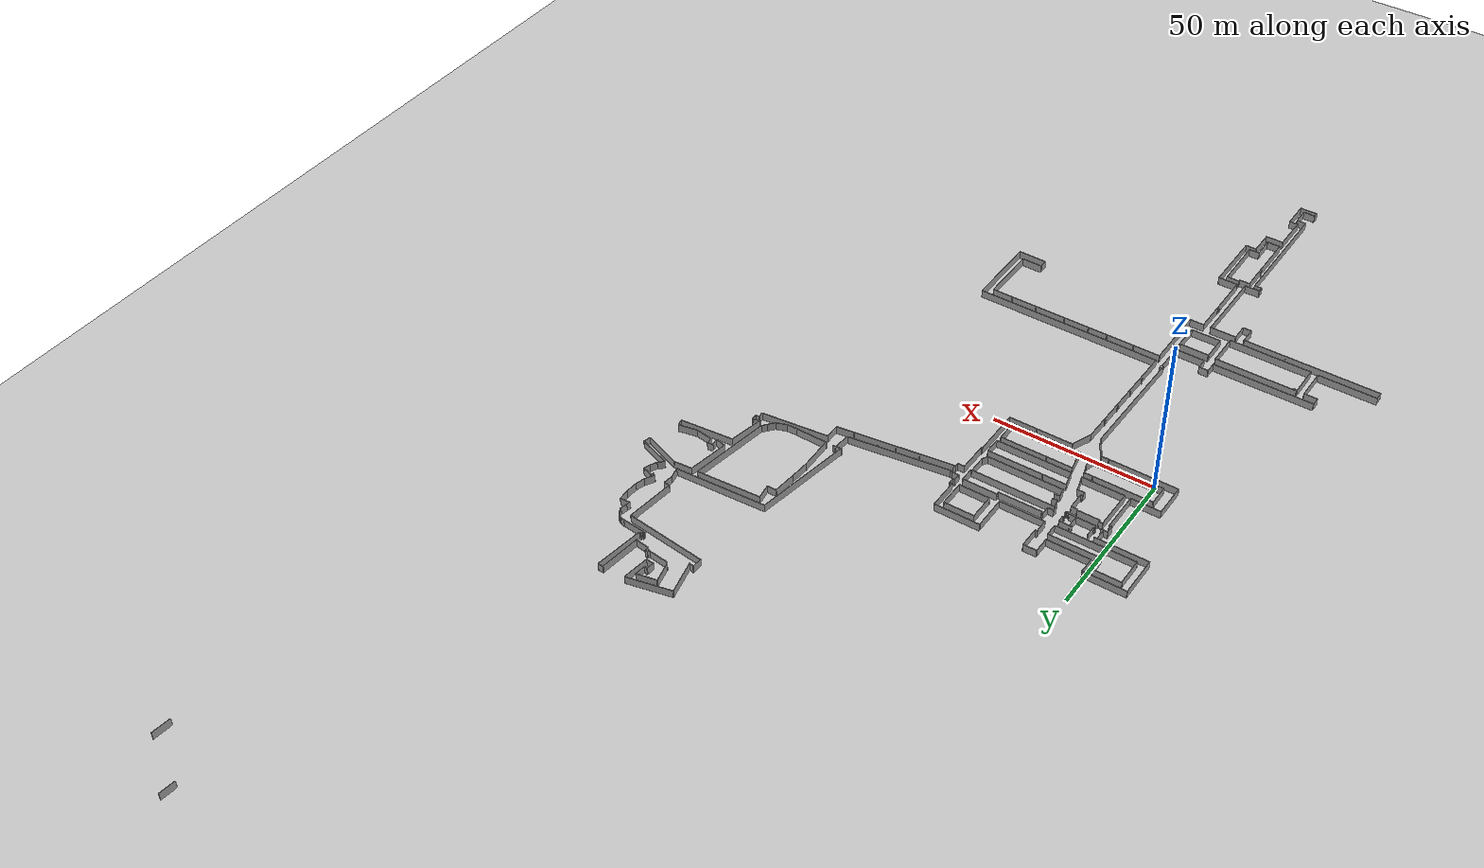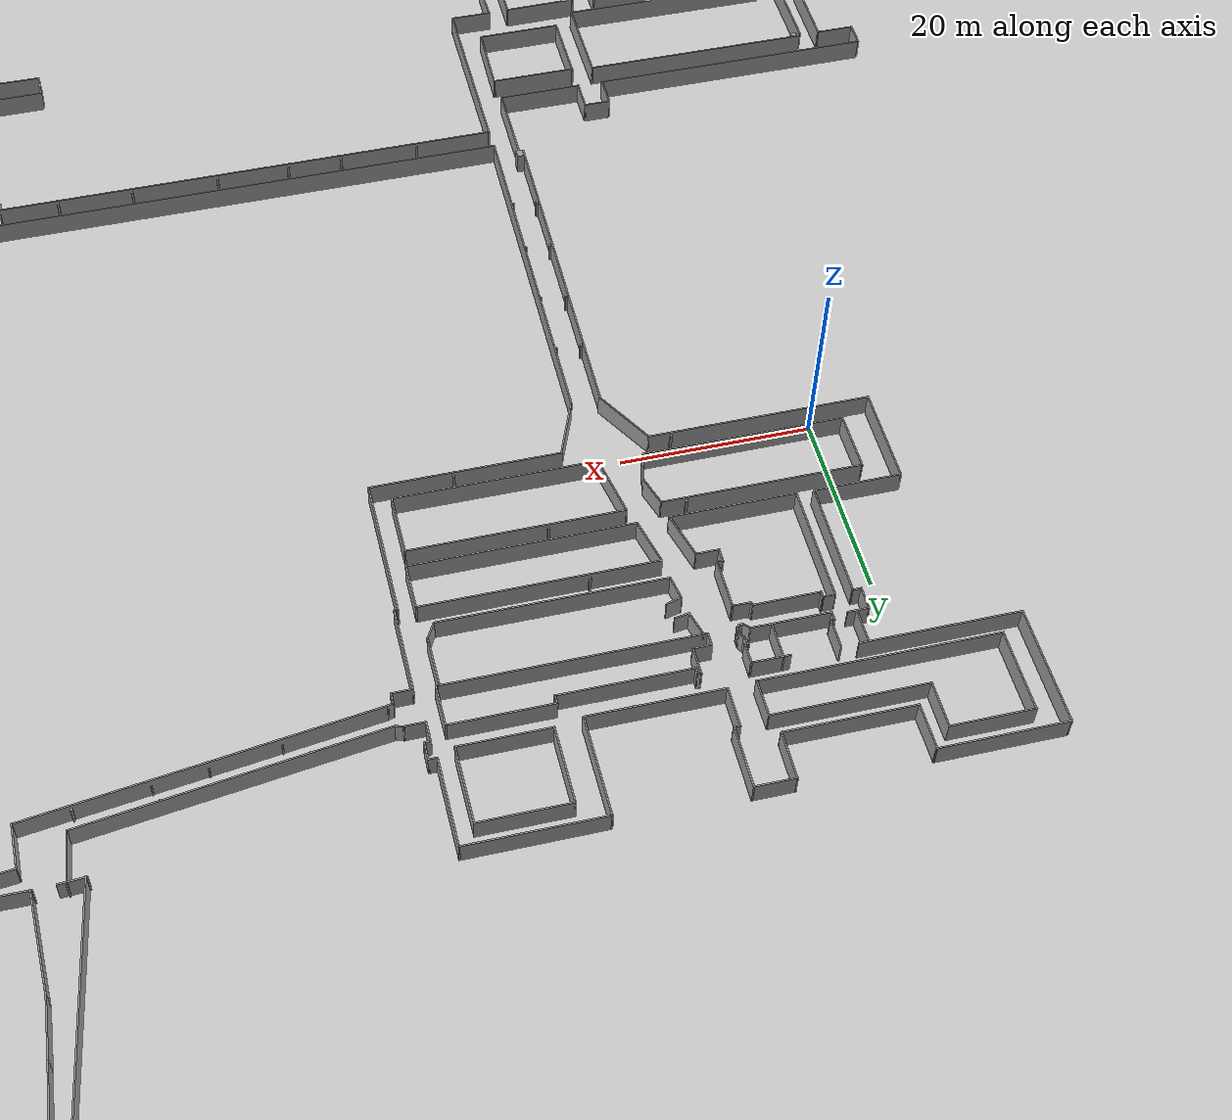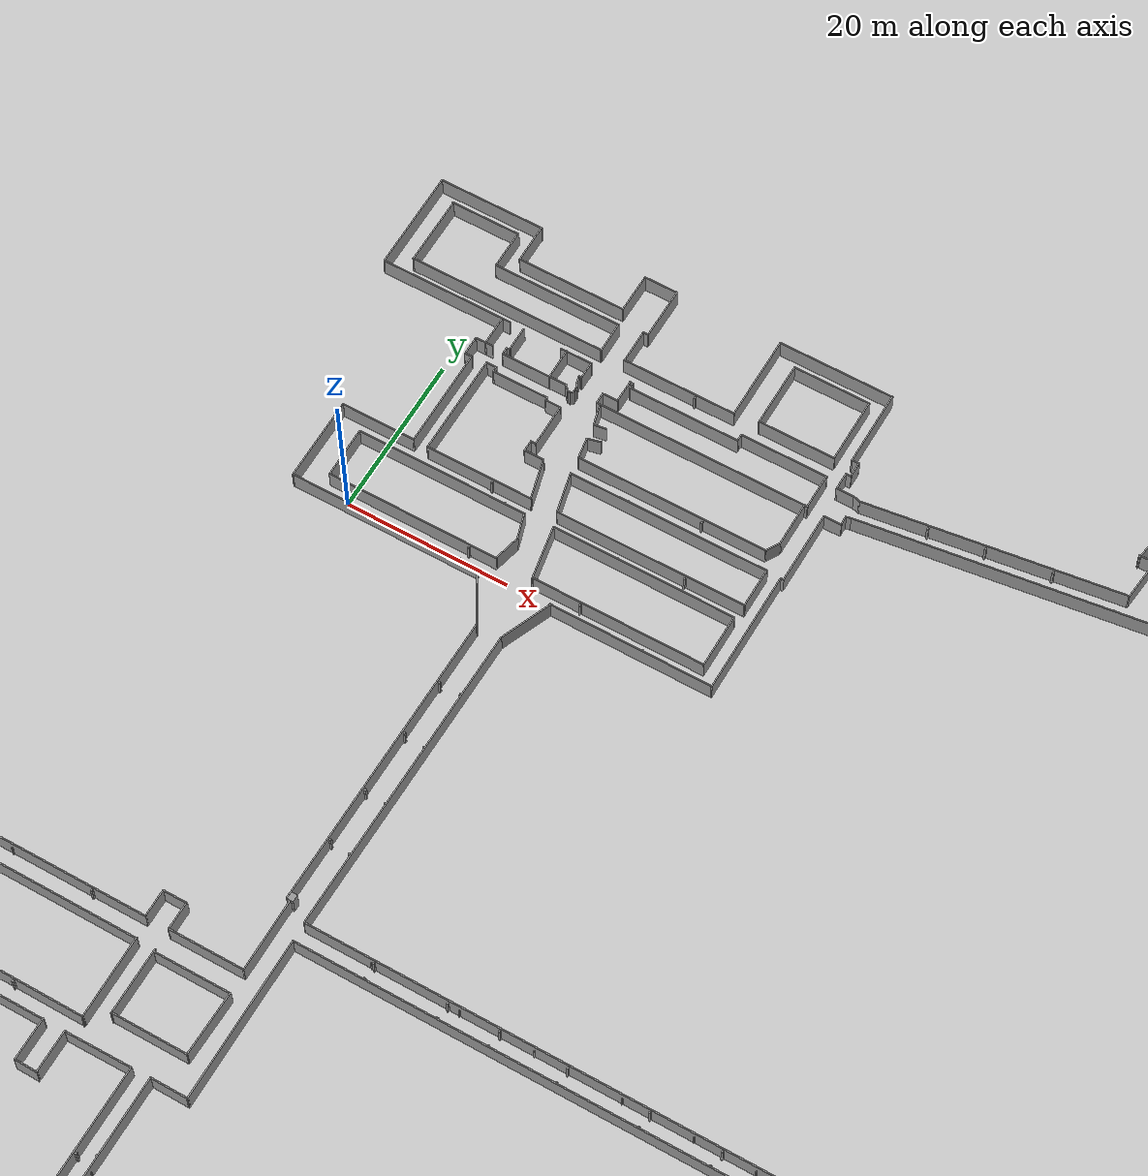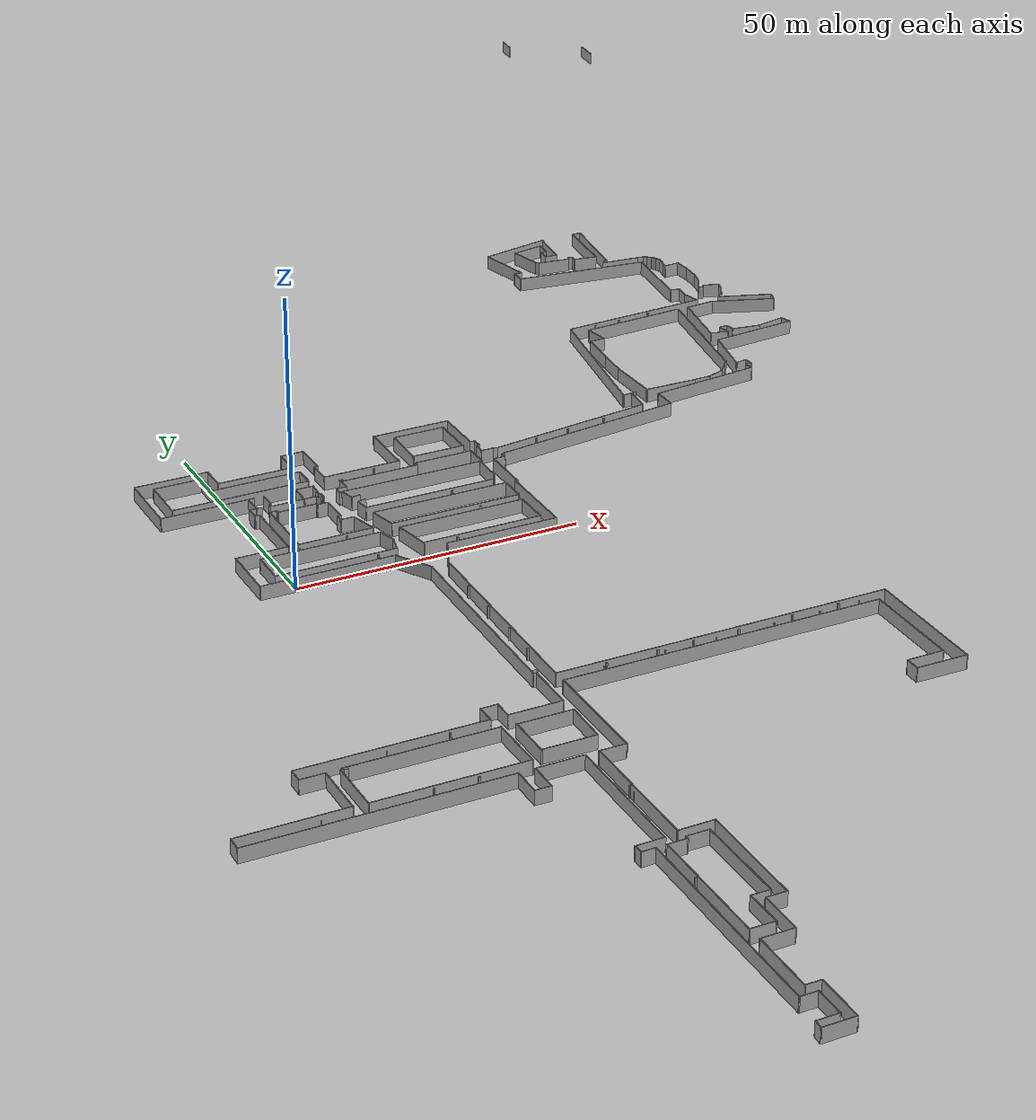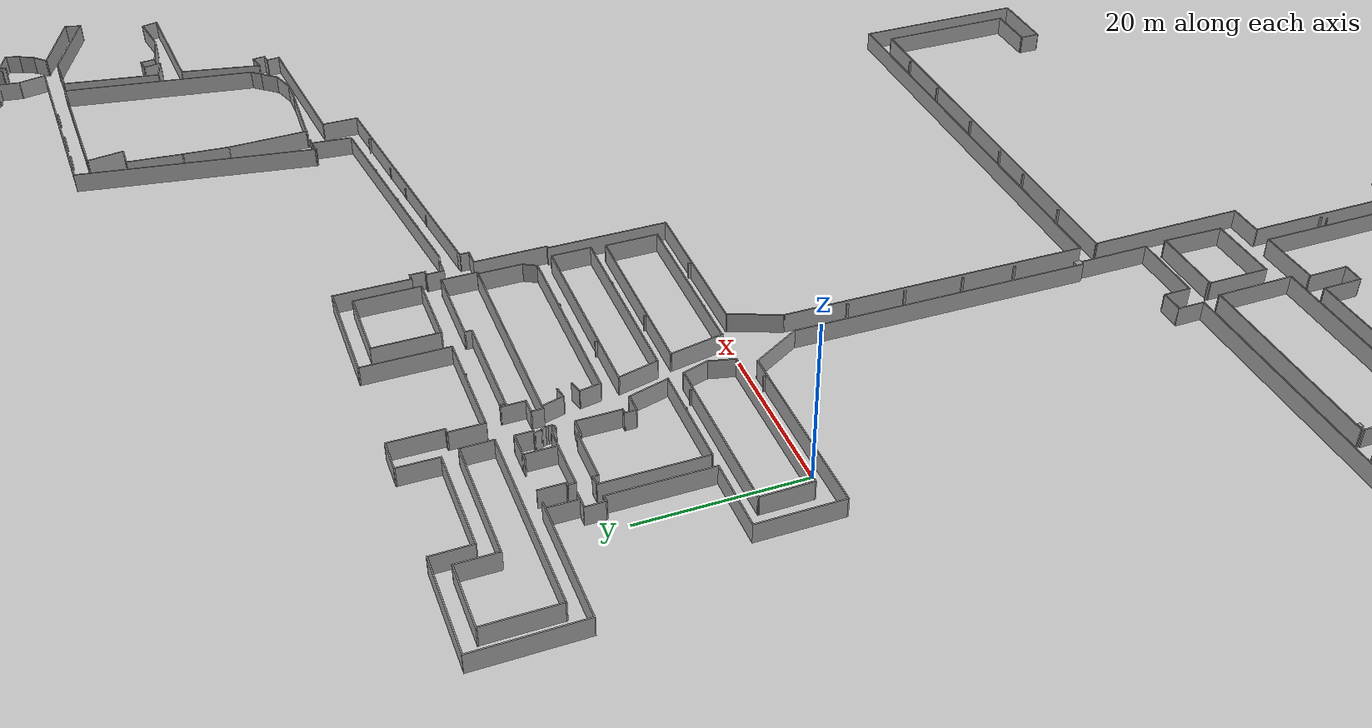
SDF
<sdf version="1.6">
 <world name="default">
  <light name="sun" type="directional">
   <pose>0 0 10 0 -0 0</pose>
   <diffuse>0.8 0.8 0.8 1</diffuse>
   <specular>0.1 0.1 0.1 1</specular>
   <attenuation>
    <range>1000</range>
    <constant>0.9</constant>
    <linear>0.01</linear>
    <quadratic>0.001</quadratic>
   </attenuation>
   <direction>-0.5 0.5 -1</direction>
  </light>
  <model name="ground_plane">
   <static>1</static>
   <link name="link">
    <collision name="collision">
     <geometry><plane><normal>0 0 1</normal><size>100 100</size></plane></geometry>
     <surface><friction><ode><mu>100</mu><mu2>50</mu2></ode></friction></surface>
    </collision>
    <visual name="visual">
     <cast_shadows>0</cast_shadows>
     <geometry><plane><normal>0 0 1</normal><size>100 100</size></plane></geometry>
     <material>
      <script><uri>file://media/materials/scripts/gazebo.material</uri><name>Gazebo/Grey</name></script>
     </material>
    </visual>
   </link>
  </model>
  <gravity>0 0 -9.8</gravity>
  <magnetic_field>6e-06 2.3e-05 -4.2e-05</magnetic_field>
  <atmosphere type="adiabatic"/>
  <physics name="default_physics" default="0" type="ode">
   <max_step_size>0.01</max_step_size>
   <real_time_factor>1</real_time_factor>
   <real_time_update_rate>100</real_time_update_rate>
  </physics>
  <scene><ambient>0.4 0.4 0.4 1</ambient><background>0.7 0.7 0.7 1</background><shadows>1</shadows></scene>
  <spherical_coordinates>
   <surface_model>EARTH_WGS84</surface_model>
   <latitude_deg>0</latitude_deg>
   <longitude_deg>0</longitude_deg>
   <elevation>0</elevation>
   <heading_deg>0</heading_deg>
  </spherical_coordinates>
  <model name="CMU">
   <pose>62.2844 43.535 0 0 -0 0</pose>
   <link name="Wall_1">
    <collision name="Wall_1_Collision">
     <geometry><box><size>23.5 0.15 2.5</size></box></geometry>
     <pose>0 0 1.25 0 -0 0</pose>
    </collision>
    <visual name="Wall_1_Visual">
     <pose>0 0 1.25 0 -0 0</pose>
     <geometry><box><size>23.5 0.15 2.5</size></box></geometry>
     <material>
      <script><uri>file://media/materials/scripts/gazebo.material</uri><name>Gazebo/Grey</name></script>
      <ambient>1 1 1 1</ambient>
     </material>
    </visual>
    <pose>-57.0241 -44.4197 0 0 -0 3.14159</pose>
   </link>
   <link name="Wall_10">
    <collision name="Wall_10_Collision">
     <geometry><box><size>3.75 0.15 2.5</size></box></geometry>
     <pose>0 0 1.25 0 -0 0</pose>
    </collision>
    <visual name="Wall_10_Visual">
     <pose>0 0 1.25 0 -0 0</pose>
     <geometry><box><size>3.75 0.15 2.5</size></box></geometry>
     <material>
      <script><uri>file://media/materials/scripts/gazebo.material</uri><name>Gazebo/Grey</name></script>
      <ambient>1 1 1 1</ambient>
     </material>
    </visual>
    <pose>-59.2095 -17.5724 0 0 -0 1.5708</pose>
   </link>
   <link name="Wall_100">
    <collision name="Wall_100_Collision">
     <geometry><box><size>21.25 0.15 2.5</size></box></geometry>
     <pose>0 0 1.25 0 -0 0</pose>
    </collision>
    <visual name="Wall_100_Visual">
     <pose>0 0 1.25 0 -0 0</pose>
     <geometry><box><size>21.25 0.15 2.5</size></box></geometry>
     <material>
      <script><uri>file://media/materials/scripts/gazebo.material</uri><name>Gazebo/Grey</name></script>
      <ambient>1 1 1 1</ambient>
     </material>
    </visual>
    <pose>-54.7083 -42.3708 0 0 -0 0</pose>
   </link>
   <link name="Wall_101">
    <collision name="Wall_101_Collision">
     <geometry><box><size>3.37379 0.15 2.5</size></box></geometry>
     <pose>0 0 1.25 0 -0 0</pose>
    </collision>
    <visual name="Wall_101_Visual">
     <pose>0 0 1.25 0 -0 0</pose>
     <geometry><box><size>3.37379 0.15 2.5</size></box></geometry>
     <material>
      <script><uri>file://media/materials/scripts/gazebo.material</uri><name>Gazebo/Grey</name></script>
      <ambient>1 1 1 1</ambient>
     </material>
    </visual>
    <pose>-43.7804 -40.7573 0 0 -0 1.33414</pose>
   </link>
   <link name="Wall_102">
    <collision name="Wall_102_Collision">
     <geometry><box><size>3.40257 0.15 2.5</size></box></geometry>
     <pose>0 0 1.25 0 -0 0</pose>
    </collision>
    <visual name="Wall_102_Visual">
     <pose>0 0 1.25 0 -0 0</pose>
     <geometry><box><size>3.40257 0.15 2.5</size></box></geometry>
     <material>
      <script><uri>file://media/materials/scripts/gazebo.material</uri><name>Gazebo/Grey</name></script>
      <ambient>1 1 1 1</ambient>
     </material>
    </visual>
    <pose>-43.8858 -37.6375 0 0 -0 1.87253</pose>
   </link>
   <link name="Wall_103">
    <collision name="Wall_103_Collision">
     <geometry><box><size>21.0858 0.15 2.5</size></box></geometry>
     <pose>0 0 1.25 0 -0 0</pose>
    </collision>
    <visual name="Wall_103_Visual">
     <pose>0 0 1.25 0 -0 0</pose>
     <geometry><box><size>21.0858 0.15 2.5</size></box></geometry>
     <material>
      <script><uri>file://media/materials/scripts/gazebo.material</uri><name>Gazebo/Grey</name></script>
      <ambient>1 1 1 1</ambient>
     </material>
    </visual>
    <pose>-54.837 -36.0847 0 0 -0 3.14159</pose>
   </link>
   <link name="Wall_105">
    <collision name="Wall_105_Collision">
     <geometry><box><size>21.25 0.15 2.5</size></box></geometry>
     <pose>0 0 1.25 0 -0 0</pose>
    </collision>
    <visual name="Wall_105_Visual">
     <pose>0 0 1.25 0 -0 0</pose>
     <geometry><box><size>21.25 0.15 2.5</size></box></geometry>
     <material>
      <script><uri>file://media/materials/scripts/gazebo.material</uri><name>Gazebo/Grey</name></script>
      <ambient>1 1 1 1</ambient>
     </material>
    </visual>
    <pose>-28.9806 -42.505 0 0 -0 0</pose>
   </link>
   <link name="Wall_106">
    <collision name="Wall_106_Collision">
     <geometry><box><size>6.75 0.15 2.5</size></box></geometry>
     <pose>0 0 1.25 0 -0 0</pose>
    </collision>
    <visual name="Wall_106_Visual">
     <pose>0 0 1.25 0 -0 0</pose>
     <geometry><box><size>6.75 0.15 2.5</size></box></geometry>
     <material>
      <script><uri>file://media/materials/scripts/gazebo.material</uri><name>Gazebo/Grey</name></script>
      <ambient>1 1 1 1</ambient>
     </material>
    </visual>
    <pose>-18.4306 -39.205 0 0 -0 1.5708</pose>
   </link>
   <link name="Wall_107">
    <collision name="Wall_107_Collision">
     <geometry><box><size>22.5 0.15 2.5</size></box></geometry>
     <pose>0 0 1.25 0 -0 0</pose>
    </collision>
    <visual name="Wall_107_Visual">
     <pose>0 0 1.25 0 -0 0</pose>
     <geometry><box><size>22.5 0.15 2.5</size></box></geometry>
     <material>
      <script><uri>file://media/materials/scripts/gazebo.material</uri><name>Gazebo/Grey</name></script>
      <ambient>1 1 1 1</ambient>
     </material>
    </visual>
    <pose>-29.6056 -35.905 0 0 -0 3.14159</pose>
   </link>
   <link name="Wall_108">
    <collision name="Wall_108_Collision">
     <geometry><box><size>6.95877 0.15 2.5</size></box></geometry>
     <pose>0 0 1.25 0 -0 0</pose>
    </collision>
    <visual name="Wall_108_Visual">
     <pose>0 0 1.25 0 -0 0</pose>
     <geometry><box><size>6.95877 0.15 2.5</size></box></geometry>
     <material>
      <script><uri>file://media/materials/scripts/gazebo.material</uri><name>Gazebo/Grey</name></script>
      <ambient>1 1 1 1</ambient>
     </material>
    </visual>
    <pose>-40.1556 -39.2515 0 0 0 -1.38616</pose>
   </link>
   <link name="Wall_110">
    <collision name="Wall_110_Collision">
     <geometry><box><size>5.17157 0.15 2.5</size></box></geometry>
     <pose>0 0 1.25 0 -0 0</pose>
    </collision>
    <visual name="Wall_110_Visual">
     <pose>0 0 1.25 0 -0 0</pose>
     <geometry><box><size>5.17157 0.15 2.5</size></box></geometry>
     <material>
      <script><uri>file://media/materials/scripts/gazebo.material</uri><name>Gazebo/Grey</name></script>
      <ambient>1 1 1 1</ambient>
     </material>
    </visual>
    <pose>-41.9731 -31.6882 0 0 0 -1.33705</pose>
   </link>
   <link name="Wall_111">
    <collision name="Wall_111_Collision">
     <geometry><box><size>23.3656 0.15 2.5</size></box></geometry>
     <pose>0 0 1.25 0 -0 0</pose>
    </collision>
    <visual name="Wall_111_Visual">
     <pose>0 0 1.25 0 -0 0</pose>
     <geometry><box><size>23.3656 0.15 2.5</size></box></geometry>
     <material>
      <script><uri>file://media/materials/scripts/gazebo.material</uri><name>Gazebo/Grey</name></script>
      <ambient>1 1 1 1</ambient>
     </material>
    </visual>
    <pose>-29.7838 -34.1074 0 0 -0 0.002004</pose>
   </link>
   <link name="Wall_112">
    <collision name="Wall_112_Collision">
     <geometry><box><size>5.08241 0.15 2.5</size></box></geometry>
     <pose>0 0 1.25 0 -0 0</pose>
    </collision>
    <visual name="Wall_112_Visual">
     <pose>0 0 1.25 0 -0 0</pose>
     <geometry><box><size>5.08241 0.15 2.5</size></box></geometry>
     <material>
      <script><uri>file://media/materials/scripts/gazebo.material</uri><name>Gazebo/Grey</name></script>
      <ambient>1 1 1 1</ambient>
     </material>
    </visual>
    <pose>-18.1761 -31.6184 0 0 -0 1.5708</pose>
   </link>
   <link name="Wall_113">
    <collision name="Wall_113_Collision">
     <geometry><box><size>24.5286 0.15 2.5</size></box></geometry>
     <pose>0 0 1.25 0 -0 0</pose>
    </collision>
    <visual name="Wall_113_Visual">
     <pose>0 0 1.25 0 -0 0</pose>
     <geometry><box><size>24.5286 0.15 2.5</size></box></geometry>
     <material>
      <script><uri>file://media/materials/scripts/gazebo.material</uri><name>Gazebo/Grey</name></script>
      <ambient>1 1 1 1</ambient>
     </material>
    </visual>
    <pose>-30.3654 -29.1759 0 0 0 -3.13968</pose>
   </link>
   <link name="Wall_115">
    <collision name="Wall_115_Collision">
     <geometry><box><size>20 0.15 2.5</size></box></geometry>
     <pose>0 0 1.25 0 -0 0</pose>
    </collision>
    <visual name="Wall_115_Visual">
     <pose>0 0 1.25 0 -0 0</pose>
     <geometry><box><size>20 0.15 2.5</size></box></geometry>
     <material>
      <script><uri>file://media/materials/scripts/gazebo.material</uri><name>Gazebo/Grey</name></script>
      <ambient>1 1 1 1</ambient>
     </material>
    </visual>
    <pose>-26.3464 -44.3474 0 0 -0 0</pose>
   </link>
   <link name="Wall_116">
    <collision name="Wall_116_Collision">
     <geometry><box><size>15.25 0.15 2.5</size></box></geometry>
     <pose>0 0 1.25 0 -0 0</pose>
    </collision>
    <visual name="Wall_116_Visual">
     <pose>0 0 1.25 0 -0 0</pose>
     <geometry><box><size>15.25 0.15 2.5</size></box></geometry>
     <material>
      <script><uri>file://media/materials/scripts/gazebo.material</uri><name>Gazebo/Grey</name></script>
      <ambient>1 1 1 1</ambient>
     </material>
    </visual>
    <pose>-16.4214 -36.7974 0 0 -0 1.5708</pose>
   </link>
   <link name="Wall_117">
    <collision name="Wall_117_Collision">
     <geometry><box><size>0.5 0.15 2.5</size></box></geometry>
     <pose>0 0 1.25 0 -0 0</pose>
    </collision>
    <visual name="Wall_117_Visual">
     <pose>0 0 1.25 0 -0 0</pose>
     <geometry><box><size>0.5 0.15 2.5</size></box></geometry>
     <material>
      <script><uri>file://media/materials/scripts/gazebo.material</uri><name>Gazebo/Grey</name></script>
      <ambient>1 1 1 1</ambient>
     </material>
    </visual>
    <pose>-16.2464 -29.2474 0 0 -0 0</pose>
   </link>
   <link name="Wall_118">
    <collision name="Wall_118_Collision">
     <geometry><box><size>9.25 0.15 2.5</size></box></geometry>
     <pose>0 0 1.25 0 -0 0</pose>
    </collision>
    <visual name="Wall_118_Visual">
     <pose>0 0 1.25 0 -0 0</pose>
     <geometry><box><size>9.25 0.15 2.5</size></box></geometry>
     <material>
      <script><uri>file://media/materials/scripts/gazebo.material</uri><name>Gazebo/Grey</name></script>
      <ambient>1 1 1 1</ambient>
     </material>
    </visual>
    <pose>-16.0714 -24.6974 0 0 -0 1.5708</pose>
   </link>
   <link name="Wall_119">
    <collision name="Wall_119_Collision">
     <geometry><box><size>2.25 0.15 2.5</size></box></geometry>
     <pose>0 0 1.25 0 -0 0</pose>
    </collision>
    <visual name="Wall_119_Visual">
     <pose>0 0 1.25 0 -0 0</pose>
     <geometry><box><size>2.25 0.15 2.5</size></box></geometry>
     <material>
      <script><uri>file://media/materials/scripts/gazebo.material</uri><name>Gazebo/Grey</name></script>
      <ambient>1 1 1 1</ambient>
     </material>
    </visual>
    <pose>-15.0214 -20.1474 0 0 -0 0</pose>
   </link>
   <link name="Wall_12">
    <collision name="Wall_12_Collision">
     <geometry><box><size>16.5 0.15 2.5</size></box></geometry>
     <pose>0 0 1.25 0 -0 0</pose>
    </collision>
    <visual name="Wall_12_Visual">
     <pose>0 0 1.25 0 -0 0</pose>
     <geometry><box><size>16.5 0.15 2.5</size></box></geometry>
     <material>
      <script><uri>file://media/materials/scripts/gazebo.material</uri><name>Gazebo/Grey</name></script>
      <ambient>1 1 1 1</ambient>
     </material>
    </visual>
    <pose>-66.4698 -15.7138 0 0 -0 3.14159</pose>
   </link>
   <link name="Wall_120">
    <collision name="Wall_120_Collision">
     <geometry><box><size>1.25 0.15 2.5</size></box></geometry>
     <pose>0 0 1.25 0 -0 0</pose>
    </collision>
    <visual name="Wall_120_Visual">
     <pose>0 0 1.25 0 -0 0</pose>
     <geometry><box><size>1.25 0.15 2.5</size></box></geometry>
     <material>
      <script><uri>file://media/materials/scripts/gazebo.material</uri><name>Gazebo/Grey</name></script>
      <ambient>1 1 1 1</ambient>
     </material>
    </visual>
    <pose>-13.9714 -19.5974 0 0 -0 1.5708</pose>
   </link>
   <link name="Wall_121">
    <collision name="Wall_121_Collision">
     <geometry><box><size>0.75 0.15 2.5</size></box></geometry>
     <pose>0 0 1.25 0 -0 0</pose>
    </collision>
    <visual name="Wall_121_Visual">
     <pose>0 0 1.25 0 -0 0</pose>
     <geometry><box><size>0.75 0.15 2.5</size></box></geometry>
     <material>
      <script><uri>file://media/materials/scripts/gazebo.material</uri><name>Gazebo/Grey</name></script>
      <ambient>1 1 1 1</ambient>
     </material>
    </visual>
    <pose>-13.6817 -18.9697 0 0 -0 0.261799</pose>
   </link>
   <link name="Wall_122">
    <collision name="Wall_122_Collision">
     <geometry><box><size>35.5943 0.15 2.5</size></box></geometry>
     <pose>0 0 1.25 0 -0 0</pose>
    </collision>
    <visual name="Wall_122_Visual">
     <pose>0 0 1.25 0 -0 0</pose>
     <geometry><box><size>35.5943 0.15 2.5</size></box></geometry>
     <material>
      <script><uri>file://media/materials/scripts/gazebo.material</uri><name>Gazebo/Grey</name></script>
      <ambient>1 1 1 1</ambient>
     </material>
    </visual>
    <pose>4.17697 -16.5662 0 0 -0 0.131623</pose>
   </link>
   <link name="Wall_123">
    <collision name="Wall_123_Collision">
     <geometry><box><size>4.70748 0.15 2.5</size></box></geometry>
     <pose>0 0 1.25 0 -0 0</pose>
    </collision>
    <visual name="Wall_123_Visual">
     <pose>0 0 1.25 0 -0 0</pose>
     <geometry><box><size>4.70748 0.15 2.5</size></box></geometry>
     <material>
      <script><uri>file://media/materials/scripts/gazebo.material</uri><name>Gazebo/Grey</name></script>
      <ambient>1 1 1 1</ambient>
     </material>
    </visual>
    <pose>21.7458 -11.9619 0 0 -0 1.5708</pose>
   </link>
   <link name="Wall_125">
    <collision name="Wall_125_Collision">
     <geometry><box><size>20.8151 0.15 2.5</size></box></geometry>
     <pose>0 0 1.25 0 -0 0</pose>
    </collision>
    <visual name="Wall_125_Visual">
     <pose>0 0 1.25 0 -0 0</pose>
     <geometry><box><size>20.8151 0.15 2.5</size></box></geometry>
     <material>
      <script><uri>file://media/materials/scripts/gazebo.material</uri><name>Gazebo/Grey</name></script>
      <ambient>1 1 1 1</ambient>
     </material>
    </visual>
    <pose>32.0165 -8.55504 0 0 -0 0.109431</pose>
   </link>
   <link name="Wall_126">
    <collision name="Wall_126_Collision">
     <geometry><box><size>1.82233 0.15 2.5</size></box></geometry>
     <pose>0 0 1.25 0 -0 0</pose>
    </collision>
    <visual name="Wall_126_Visual">
     <pose>0 0 1.25 0 -0 0</pose>
     <geometry><box><size>1.82233 0.15 2.5</size></box></geometry>
     <material>
      <script><uri>file://media/materials/scripts/gazebo.material</uri><name>Gazebo/Grey</name></script>
      <ambient>1 1 1 1</ambient>
     </material>
    </visual>
    <pose>42.1803 -6.59731 0 0 -0 1.69912</pose>
   </link>
   <link name="Wall_127">
    <collision name="Wall_127_Collision">
     <geometry><box><size>1.34635 0.15 2.5</size></box></geometry>
     <pose>0 0 1.25 0 -0 0</pose>
    </collision>
    <visual name="Wall_127_Visual">
     <pose>0 0 1.25 0 -0 0</pose>
     <geometry><box><size>1.34635 0.15 2.5</size></box></geometry>
     <material>
      <script><uri>file://media/materials/scripts/gazebo.material</uri><name>Gazebo/Grey</name></script>
      <ambient>1 1 1 1</ambient>
     </material>
    </visual>
    <pose>42.6618 -5.66101 0 0 -0 0.179853</pose>
   </link>
   <link name="Wall_128">
    <collision name="Wall_128_Collision">
     <geometry><box><size>1.70985 0.15 2.5</size></box></geometry>
     <pose>0 0 1.25 0 -0 0</pose>
    </collision>
    <visual name="Wall_128_Visual">
     <pose>0 0 1.25 0 -0 0</pose>
     <geometry><box><size>1.70985 0.15 2.5</size></box></geometry>
     <material>
      <script><uri>file://media/materials/scripts/gazebo.material</uri><name>Gazebo/Grey</name></script>
      <ambient>1 1 1 1</ambient>
     </material>
    </visual>
    <pose>43.1701 -4.77822 0 0 -0 1.67388</pose>
   </link>
   <link name="Wall_129">
    <collision name="Wall_129_Collision">
     <geometry><box><size>2.38497 0.15 2.5</size></box></geometry>
     <pose>0 0 1.25 0 -0 0</pose>
    </collision>
    <visual name="Wall_129_Visual">
     <pose>0 0 1.25 0 -0 0</pose>
     <geometry><box><size>2.38497 0.15 2.5</size></box></geometry>
     <material>
      <script><uri>file://media/materials/scripts/gazebo.material</uri><name>Gazebo/Grey</name></script>
      <ambient>1 1 1 1</ambient>
     </material>
    </visual>
    <pose>41.993 -4.21645 0 0 0 -2.94889</pose>
   </link>
   <link name="Wall_13">
    <collision name="Wall_13_Collision">
     <geometry><box><size>12.7464 0.15 2.5</size></box></geometry>
     <pose>0 0 1.25 0 -0 0</pose>
    </collision>
    <visual name="Wall_13_Visual">
     <pose>0 0 1.25 0 -0 0</pose>
     <geometry><box><size>12.7464 0.15 2.5</size></box></geometry>
     <material>
      <script><uri>file://media/materials/scripts/gazebo.material</uri><name>Gazebo/Grey</name></script>
      <ambient>1 1 1 1</ambient>
     </material>
    </visual>
    <pose>-74.6624 -9.4157 0 0 -0 1.57359</pose>
   </link>
   <link name="Wall_130">
    <collision name="Wall_130_Collision">
     <geometry><box><size>10.7896 0.15 2.5</size></box></geometry>
     <pose>0 0 1.25 0 -0 0</pose>
    </collision>
    <visual name="Wall_130_Visual">
     <pose>0 0 1.25 0 -0 0</pose>
     <geometry><box><size>10.7896 0.15 2.5</size></box></geometry>
     <material>
      <script><uri>file://media/materials/scripts/gazebo.material</uri><name>Gazebo/Grey</name></script>
      <ambient>1 1 1 1</ambient>
     </material>
    </visual>
    <pose>41.9395 0.786037 0 0 -0 1.3734</pose>
   </link>
   <link name="Wall_131">
    <collision name="Wall_131_Collision">
     <geometry><box><size>16.5902 0.15 2.5</size></box></geometry>
     <pose>0 0 1.25 0 -0 0</pose>
    </collision>
    <visual name="Wall_131_Visual">
     <pose>0 0 1.25 0 -0 0</pose>
     <geometry><box><size>16.5902 0.15 2.5</size></box></geometry>
     <material>
      <script><uri>file://media/materials/scripts/gazebo.material</uri><name>Gazebo/Grey</name></script>
      <ambient>1 1 1 1</ambient>
     </material>
    </visual>
    <pose>51.1687 6.75156 0 0 -0 0.091249</pose>
   </link>
   <link name="Wall_132">
    <collision name="Wall_132_Collision">
     <geometry><box><size>2.25 0.15 2.5</size></box></geometry>
     <pose>0 0 1.25 0 -0 0</pose>
    </collision>
    <visual name="Wall_132_Visual">
     <pose>0 0 1.25 0 -0 0</pose>
     <geometry><box><size>2.25 0.15 2.5</size></box></geometry>
     <material>
      <script><uri>file://media/materials/scripts/gazebo.material</uri><name>Gazebo/Grey</name></script>
      <ambient>1 1 1 1</ambient>
     </material>
    </visual>
    <pose>59.0828 8.51482 0 0 -0 1.8326</pose>
   </link>
   <link name="Wall_134">
    <collision name="Wall_134_Collision">
     <geometry><box><size>5.86977 0.15 2.5</size></box></geometry>
     <pose>0 0 1.25 0 -0 0</pose>
    </collision>
    <visual name="Wall_134_Visual">
     <pose>0 0 1.25 0 -0 0</pose>
     <geometry><box><size>5.86977 0.15 2.5</size></box></geometry>
     <material>
      <script><uri>file://media/materials/scripts/gazebo.material</uri><name>Gazebo/Grey</name></script>
      <ambient>1 1 1 1</ambient>
     </material>
    </visual>
    <pose>56.0064 8.9696 0 0 0 -2.9447</pose>
   </link>
   <link name="Wall_135">
    <collision name="Wall_135_Collision">
     <geometry><box><size>5.44648 0.15 2.5</size></box></geometry>
     <pose>0 0 1.25 0 -0 0</pose>
    </collision>
    <visual name="Wall_135_Visual">
     <pose>0 0 1.25 0 -0 0</pose>
     <geometry><box><size>5.44648 0.15 2.5</size></box></geometry>
     <material>
      <script><uri>file://media/materials/scripts/gazebo.material</uri><name>Gazebo/Grey</name></script>
      <ambient>1 1 1 1</ambient>
     </material>
    </visual>
    <pose>50.5802 8.78466 0 0 -0 2.9997</pose>
   </link>
   <link name="Wall_136">
    <collision name="Wall_136_Collision">
     <geometry><box><size>2.02945 0.15 2.5</size></box></geometry>
     <pose>0 0 1.25 0 -0 0</pose>
    </collision>
    <visual name="Wall_136_Visual">
     <pose>0 0 1.25 0 -0 0</pose>
     <geometry><box><size>2.02945 0.15 2.5</size></box></geometry>
     <material>
      <script><uri>file://media/materials/scripts/gazebo.material</uri><name>Gazebo/Grey</name></script>
      <ambient>1 1 1 1</ambient>
     </material>
    </visual>
    <pose>47.8783 10.0955 0 0 -0 1.6563</pose>
   </link>
   <link name="Wall_137">
    <collision name="Wall_137_Collision">
     <geometry><box><size>1.82233 0.15 2.5</size></box></geometry>
     <pose>0 0 1.25 0 -0 0</pose>
    </collision>
    <visual name="Wall_137_Visual">
     <pose>0 0 1.25 0 -0 0</pose>
     <geometry><box><size>1.82233 0.15 2.5</size></box></geometry>
     <material>
      <script><uri>file://media/materials/scripts/gazebo.material</uri><name>Gazebo/Grey</name></script>
      <ambient>1 1 1 1</ambient>
     </material>
    </visual>
    <pose>46.9687 10.9248 0 0 0 -3.01327</pose>
   </link>
   <link name="Wall_138">
    <collision name="Wall_138_Collision">
     <geometry><box><size>2.43751 0.15 2.5</size></box></geometry>
     <pose>0 0 1.25 0 -0 0</pose>
    </collision>
    <visual name="Wall_138_Visual">
     <pose>0 0 1.25 0 -0 0</pose>
     <geometry><box><size>2.43751 0.15 2.5</size></box></geometry>
     <material>
      <script><uri>file://media/materials/scripts/gazebo.material</uri><name>Gazebo/Grey</name></script>
      <ambient>1 1 1 1</ambient>
     </material>
    </visual>
    <pose>46.3535 9.69421 0 0 0 -1.38258</pose>
   </link>
   <link name="Wall_139">
    <collision name="Wall_139_Collision">
     <geometry><box><size>3.4762 0.15 2.5</size></box></geometry>
     <pose>0 0 1.25 0 -0 0</pose>
    </collision>
    <visual name="Wall_139_Visual">
     <pose>0 0 1.25 0 -0 0</pose>
     <geometry><box><size>3.4762 0.15 2.5</size></box></geometry>
     <material>
      <script><uri>file://media/materials/scripts/gazebo.material</uri><name>Gazebo/Grey</name></script>
      <ambient>1 1 1 1</ambient>
     </material>
    </visual>
    <pose>44.9356 8.89167 0 0 -0 2.94735</pose>
   </link>
   <link name="Wall_14">
    <collision name="Wall_14_Collision">
     <geometry><box><size>13.25 0.15 2.5</size></box></geometry>
     <pose>0 0 1.25 0 -0 0</pose>
    </collision>
    <visual name="Wall_14_Visual">
     <pose>0 0 1.25 0 -0 0</pose>
     <geometry><box><size>13.25 0.15 2.5</size></box></geometry>
     <material>
      <script><uri>file://media/materials/scripts/gazebo.material</uri><name>Gazebo/Grey</name></script>
      <ambient>1 1 1 1</ambient>
     </material>
    </visual>
    <pose>-68.0948 -3.11757 0 0 -0 0</pose>
   </link>
   <link name="Wall_140">
    <collision name="Wall_140_Collision">
     <geometry><box><size>12.8423 0.15 2.5</size></box></geometry>
     <pose>0 0 1.25 0 -0 0</pose>
    </collision>
    <visual name="Wall_140_Visual">
     <pose>0 0 1.25 0 -0 0</pose>
     <geometry><box><size>12.8423 0.15 2.5</size></box></geometry>
     <material>
      <script><uri>file://media/materials/scripts/gazebo.material</uri><name>Gazebo/Grey</name></script>
      <ambient>1 1 1 1</ambient>
     </material>
    </visual>
    <pose>44.3471 15.4725 0 0 -0 1.40565</pose>
   </link>
   <link name="Wall_141">
    <collision name="Wall_141_Collision">
     <geometry><box><size>5.78404 0.15 2.5</size></box></geometry>
     <pose>0 0 1.25 0 -0 0</pose>
    </collision>
    <visual name="Wall_141_Visual">
     <pose>0 0 1.25 0 -0 0</pose>
     <geometry><box><size>5.78404 0.15 2.5</size></box></geometry>
     <material>
      <script><uri>file://media/materials/scripts/gazebo.material</uri><name>Gazebo/Grey</name></script>
      <ambient>1 1 1 1</ambient>
     </material>
    </visual>
    <pose>48.1993 21.9463 0 0 -0 0.076044</pose>
   </link>
   <link name="Wall_142">
    <collision name="Wall_142_Collision">
     <geometry><box><size>12.0987 0.15 2.5</size></box></geometry>
     <pose>0 0 1.25 0 -0 0</pose>
    </collision>
    <visual name="Wall_142_Visual">
     <pose>0 0 1.25 0 -0 0</pose>
     <geometry><box><size>12.0987 0.15 2.5</size></box></geometry>
     <material>
      <script><uri>file://media/materials/scripts/gazebo.material</uri><name>Gazebo/Grey</name></script>
      <ambient>1 1 1 1</ambient>
     </material>
    </visual>
    <pose>56.6259 20.1272 0 0 0 -0.347241</pose>
   </link>
   <link name="Wall_143">
    <collision name="Wall_143_Collision">
     <geometry><box><size>2.3041 0.15 2.5</size></box></geometry>
     <pose>0 0 1.25 0 -0 0</pose>
    </collision>
    <visual name="Wall_143_Visual">
     <pose>0 0 1.25 0 -0 0</pose>
     <geometry><box><size>2.3041 0.15 2.5</size></box></geometry>
     <material>
      <script><uri>file://media/materials/scripts/gazebo.material</uri><name>Gazebo/Grey</name></script>
      <ambient>1 1 1 1</ambient>
     </material>
    </visual>
    <pose>62.5112 19.1374 0 0 -0 1.31979</pose>
   </link>
   <link name="Wall_144">
    <collision name="Wall_144_Collision">
     <geometry><box><size>10.4038 0.15 2.5</size></box></geometry>
     <pose>0 0 1.25 0 -0 0</pose>
    </collision>
    <visual name="Wall_144_Visual">
     <pose>0 0 1.25 0 -0 0</pose>
     <geometry><box><size>10.4038 0.15 2.5</size></box></geometry>
     <material>
      <script><uri>file://media/materials/scripts/gazebo.material</uri><name>Gazebo/Grey</name></script>
      <ambient>1 1 1 1</ambient>
     </material>
    </visual>
    <pose>57.9367 21.866 0 0 -0 2.80664</pose>
   </link>
   <link name="Wall_146">
    <collision name="Wall_146_Collision">
     <geometry><box><size>2.34425 0.15 2.5</size></box></geometry>
     <pose>0 0 1.25 0 -0 0</pose>
    </collision>
    <visual name="Wall_146_Visual">
     <pose>0 0 1.25 0 -0 0</pose>
     <geometry><box><size>2.34425 0.15 2.5</size></box></geometry>
     <material>
      <script><uri>file://media/materials/scripts/gazebo.material</uri><name>Gazebo/Grey</name></script>
      <ambient>1 1 1 1</ambient>
     </material>
    </visual>
    <pose>53.8706 24.3271 0 0 -0 0.785398</pose>
   </link>
   <link name="Wall_147">
    <collision name="Wall_147_Collision">
     <geometry><box><size>2.32789 0.15 2.5</size></box></geometry>
     <pose>0 0 1.25 0 -0 0</pose>
    </collision>
    <visual name="Wall_147_Visual">
     <pose>0 0 1.25 0 -0 0</pose>
     <geometry><box><size>2.32789 0.15 2.5</size></box></geometry>
     <material>
      <script><uri>file://media/materials/scripts/gazebo.material</uri><name>Gazebo/Grey</name></script>
      <ambient>1 1 1 1</ambient>
     </material>
    </visual>
    <pose>55.1546 26.066 0 0 -0 1.08517</pose>
   </link>
   <link name="Wall_148">
    <collision name="Wall_148_Collision">
     <geometry><box><size>2.07906 0.15 2.5</size></box></geometry>
     <pose>0 0 1.25 0 -0 0</pose>
    </collision>
    <visual name="Wall_148_Visual">
     <pose>0 0 1.25 0 -0 0</pose>
     <geometry><box><size>2.07906 0.15 2.5</size></box></geometry>
     <material>
      <script><uri>file://media/materials/scripts/gazebo.material</uri><name>Gazebo/Grey</name></script>
      <ambient>1 1 1 1</ambient>
     </material>
    </visual>
    <pose>55.9839 27.9386 0 0 -0 1.2315</pose>
   </link>
   <link name="Wall_149">
    <collision name="Wall_149_Collision">
     <geometry><box><size>3.41541 0.15 2.5</size></box></geometry>
     <pose>0 0 1.25 0 -0 0</pose>
    </collision>
    <visual name="Wall_149_Visual">
     <pose>0 0 1.25 0 -0 0</pose>
     <geometry><box><size>3.41541 0.15 2.5</size></box></geometry>
     <material>
      <script><uri>file://media/materials/scripts/gazebo.material</uri><name>Gazebo/Grey</name></script>
      <ambient>1 1 1 1</ambient>
     </material>
    </visual>
    <pose>54.7533 29.3564 0 0 -0 2.82502</pose>
   </link>
   <link name="Wall_15">
    <collision name="Wall_15_Collision">
     <geometry><box><size>4.99676 0.15 2.5</size></box></geometry>
     <pose>0 0 1.25 0 -0 0</pose>
    </collision>
    <visual name="Wall_15_Visual">
     <pose>0 0 1.25 0 -0 0</pose>
     <geometry><box><size>4.99676 0.15 2.5</size></box></geometry>
     <material>
      <script><uri>file://media/materials/scripts/gazebo.material</uri><name>Gazebo/Grey</name></script>
      <ambient>1 1 1 1</ambient>
     </material>
    </visual>
    <pose>-61.5624 -5.5407 0 0 0 -1.56354</pose>
   </link>
   <link name="Wall_150">
    <collision name="Wall_150_Collision">
     <geometry><box><size>0.987447 0.15 2.5</size></box></geometry>
     <pose>0 0 1.25 0 -0 0</pose>
    </collision>
    <visual name="Wall_150_Visual">
     <pose>0 0 1.25 0 -0 0</pose>
     <geometry><box><size>0.987447 0.15 2.5</size></box></geometry>
     <material>
      <script><uri>file://media/materials/scripts/gazebo.material</uri><name>Gazebo/Grey</name></script>
      <ambient>1 1 1 1</ambient>
     </material>
    </visual>
    <pose>53.0145 29.4901 0 0 0 -2.03444</pose>
   </link>
   <link name="Wall_151">
    <collision name="Wall_151_Collision">
     <geometry><box><size>0.96668 0.15 2.5</size></box></geometry>
     <pose>0 0 1.25 0 -0 0</pose>
    </collision>
    <visual name="Wall_151_Visual">
     <pose>0 0 1.25 0 -0 0</pose>
     <geometry><box><size>0.96668 0.15 2.5</size></box></geometry>
     <material>
      <script><uri>file://media/materials/scripts/gazebo.material</uri><name>Gazebo/Grey</name></script>
      <ambient>1 1 1 1</ambient>
     </material>
    </visual>
    <pose>52.4795 29.3296 0 0 -0 2.58994</pose>
   </link>
   <link name="Wall_152">
    <collision name="Wall_152_Collision">
     <geometry><box><size>3.21603 0.15 2.5</size></box></geometry>
     <pose>0 0 1.25 0 -0 0</pose>
    </collision>
    <visual name="Wall_152_Visual">
     <pose>0 0 1.25 0 -0 0</pose>
     <geometry><box><size>3.21603 0.15 2.5</size></box></geometry>
     <material>
      <script><uri>file://media/materials/scripts/gazebo.material</uri><name>Gazebo/Grey</name></script>
      <ambient>1 1 1 1</ambient>
     </material>
    </visual>
    <pose>52.8808 30.8812 0 0 -0 1.06031</pose>
   </link>
   <link name="Wall_153">
    <collision name="Wall_153_Collision">
     <geometry><box><size>3.0312 0.15 2.5</size></box></geometry>
     <pose>0 0 1.25 0 -0 0</pose>
    </collision>
    <visual name="Wall_153_Visual">
     <pose>0 0 1.25 0 -0 0</pose>
     <geometry><box><size>3.0312 0.15 2.5</size></box></geometry>
     <material>
      <script><uri>file://media/materials/scripts/gazebo.material</uri><name>Gazebo/Grey</name></script>
      <ambient>1 1 1 1</ambient>
     </material>
    </visual>
    <pose>54.0043 33.6098 0 0 -0 1.3078</pose>
   </link>
   <link name="Wall_154">
    <collision name="Wall_154_Collision">
     <geometry><box><size>3.79446 0.15 2.5</size></box></geometry>
     <pose>0 0 1.25 0 -0 0</pose>
    </collision>
    <visual name="Wall_154_Visual">
     <pose>0 0 1.25 0 -0 0</pose>
     <geometry><box><size>3.79446 0.15 2.5</size></box></geometry>
     <material>
      <script><uri>file://media/materials/scripts/gazebo.material</uri><name>Gazebo/Grey</name></script>
      <ambient>1 1 1 1</ambient>
     </material>
    </visual>
    <pose>54.4858 36.82 0 0 -0 1.51204</pose>
   </link>
   <link name="Wall_155">
    <collision name="Wall_155_Collision">
     <geometry><box><size>3.31389 0.15 2.5</size></box></geometry>
     <pose>0 0 1.25 0 -0 0</pose>
    </collision>
    <visual name="Wall_155_Visual">
     <pose>0 0 1.25 0 -0 0</pose>
     <geometry><box><size>3.31389 0.15 2.5</size></box></geometry>
     <material>
      <script><uri>file://media/materials/scripts/gazebo.material</uri><name>Gazebo/Grey</name></script>
      <ambient>1 1 1 1</ambient>
     </material>
    </visual>
    <pose>54.4858 40.2174 0 0 -0 1.63849</pose>
   </link>
   <link name="Wall_156">
    <collision name="Wall_156_Collision">
     <geometry><box><size>3.15377 0.15 2.5</size></box></geometry>
     <pose>0 0 1.25 0 -0 0</pose>
    </collision>
    <visual name="Wall_156_Visual">
     <pose>0 0 1.25 0 -0 0</pose>
     <geometry><box><size>3.15377 0.15 2.5</size></box></geometry>
     <material>
      <script><uri>file://media/materials/scripts/gazebo.material</uri><name>Gazebo/Grey</name></script>
      <ambient>1 1 1 1</ambient>
     </material>
    </visual>
    <pose>52.8808 41.6887 0 0 0 -3.07029</pose>
   </link>
   <link name="Wall_157">
    <collision name="Wall_157_Collision">
     <geometry><box><size>1.24124 0.15 2.5</size></box></geometry>
     <pose>0 0 1.25 0 -0 0</pose>
    </collision>
    <visual name="Wall_157_Visual">
     <pose>0 0 1.25 0 -0 0</pose>
     <geometry><box><size>1.24124 0.15 2.5</size></box></geometry>
     <material>
      <script><uri>file://media/materials/scripts/gazebo.material</uri><name>Gazebo/Grey</name></script>
      <ambient>1 1 1 1</ambient>
     </material>
    </visual>
    <pose>51.4897 42.1167 0 0 -0 1.3734</pose>
   </link>
   <link name="Wall_159">
    <collision name="Wall_159_Collision">
     <geometry><box><size>2.28004 0.15 2.5</size></box></geometry>
     <pose>0 0 1.25 0 -0 0</pose>
    </collision>
    <visual name="Wall_159_Visual">
     <pose>0 0 1.25 0 -0 0</pose>
     <geometry><box><size>2.28004 0.15 2.5</size></box></geometry>
     <material>
      <script><uri>file://media/materials/scripts/gazebo.material</uri><name>Gazebo/Grey</name></script>
      <ambient>1 1 1 1</ambient>
     </material>
    </visual>
    <pose>51.8107 43.695 0 0 -0 1.36848</pose>
   </link>
   <link name="Wall_16">
    <collision name="Wall_16_Collision">
     <geometry><box><size>13.5 0.15 2.5</size></box></geometry>
     <pose>0 0 1.25 0 -0 0</pose>
    </collision>
    <visual name="Wall_16_Visual">
     <pose>0 0 1.25 0 -0 0</pose>
     <geometry><box><size>13.5 0.15 2.5</size></box></geometry>
     <material>
      <script><uri>file://media/materials/scripts/gazebo.material</uri><name>Gazebo/Grey</name></script>
      <ambient>1 1 1 1</ambient>
     </material>
    </visual>
    <pose>-54.8698 -7.96382 0 0 -0 0</pose>
   </link>
   <link name="Wall_160">
    <collision name="Wall_160_Collision">
     <geometry><box><size>1.33433 0.15 2.5</size></box></geometry>
     <pose>0 0 1.25 0 -0 0</pose>
    </collision>
    <visual name="Wall_160_Visual">
     <pose>0 0 1.25 0 -0 0</pose>
     <geometry><box><size>1.33433 0.15 2.5</size></box></geometry>
     <material>
      <script><uri>file://media/materials/scripts/gazebo.material</uri><name>Gazebo/Grey</name></script>
      <ambient>1 1 1 1</ambient>
     </material>
    </visual>
    <pose>51.8375 45.3001 0 0 -0 1.89255</pose>
   </link>
   <link name="Wall_161">
    <collision name="Wall_161_Collision">
     <geometry><box><size>1.15948 0.15 2.5</size></box></geometry>
     <pose>0 0 1.25 0 -0 0</pose>
    </collision>
    <visual name="Wall_161_Visual">
     <pose>0 0 1.25 0 -0 0</pose>
     <geometry><box><size>1.15948 0.15 2.5</size></box></geometry>
     <material>
      <script><uri>file://media/materials/scripts/gazebo.material</uri><name>Gazebo/Grey</name></script>
      <ambient>1 1 1 1</ambient>
     </material>
    </visual>
    <pose>51.3827 46.2899 0 0 -0 2.1294</pose>
   </link>
   <link name="Wall_162">
    <collision name="Wall_162_Collision">
     <geometry><box><size>1.07049 0.15 2.5</size></box></geometry>
     <pose>0 0 1.25 0 -0 0</pose>
    </collision>
    <visual name="Wall_162_Visual">
     <pose>0 0 1.25 0 -0 0</pose>
     <geometry><box><size>1.07049 0.15 2.5</size></box></geometry>
     <material>
      <script><uri>file://media/materials/scripts/gazebo.material</uri><name>Gazebo/Grey</name></script>
      <ambient>1 1 1 1</ambient>
     </material>
    </visual>
    <pose>50.7407 46.9855 0 0 -0 2.52134</pose>
   </link>
   <link name="Wall_163">
    <collision name="Wall_163_Collision">
     <geometry><box><size>0.916039 0.15 2.5</size></box></geometry>
     <pose>0 0 1.25 0 -0 0</pose>
    </collision>
    <visual name="Wall_163_Visual">
     <pose>0 0 1.25 0 -0 0</pose>
     <geometry><box><size>0.916039 0.15 2.5</size></box></geometry>
     <material>
      <script><uri>file://media/materials/scripts/gazebo.material</uri><name>Gazebo/Grey</name></script>
      <ambient>1 1 1 1</ambient>
     </material>
    </visual>
    <pose>50.0184 47.4135 0 0 -0 2.70919</pose>
   </link>
   <link name="Wall_164">
    <collision name="Wall_164_Collision">
     <geometry><box><size>1.28496 0.15 2.5</size></box></geometry>
     <pose>0 0 1.25 0 -0 0</pose>
    </collision>
    <visual name="Wall_164_Visual">
     <pose>0 0 1.25 0 -0 0</pose>
     <geometry><box><size>1.28496 0.15 2.5</size></box></geometry>
     <material>
      <script><uri>file://media/materials/scripts/gazebo.material</uri><name>Gazebo/Grey</name></script>
      <ambient>1 1 1 1</ambient>
     </material>
    </visual>
    <pose>49.1088 47.6542 0 0 -0 2.9997</pose>
   </link>
   <link name="Wall_165">
    <collision name="Wall_165_Collision">
     <geometry><box><size>7.45461 0.15 2.5</size></box></geometry>
     <pose>0 0 1.25 0 -0 0</pose>
    </collision>
    <visual name="Wall_165_Visual">
     <pose>0 0 1.25 0 -0 0</pose>
     <geometry><box><size>7.45461 0.15 2.5</size></box></geometry>
     <material>
      <script><uri>file://media/materials/scripts/gazebo.material</uri><name>Gazebo/Grey</name></script>
      <ambient>1 1 1 1</ambient>
     </material>
    </visual>
    <pose>44.9089 48.0555 0 0 -0 3.05358</pose>
   </link>
   <link name="Wall_166">
    <collision name="Wall_166_Collision">
     <geometry><box><size>0.539504 0.15 2.5</size></box></geometry>
     <pose>0 0 1.25 0 -0 0</pose>
    </collision>
    <visual name="Wall_166_Visual">
     <pose>0 0 1.25 0 -0 0</pose>
     <geometry><box><size>0.539504 0.15 2.5</size></box></geometry>
     <material>
      <script><uri>file://media/materials/scripts/gazebo.material</uri><name>Gazebo/Grey</name></script>
      <ambient>1 1 1 1</ambient>
     </material>
    </visual>
    <pose>41.3242 48.5638 0 0 -0 1.2925</pose>
   </link>
   <link name="Wall_167">
    <collision name="Wall_167_Collision">
     <geometry><box><size>0.417513 0.15 2.5</size></box></geometry>
     <pose>0 0 1.25 0 -0 0</pose>
    </collision>
    <visual name="Wall_167_Visual">
     <pose>0 0 1.25 0 -0 0</pose>
     <geometry><box><size>0.417513 0.15 2.5</size></box></geometry>
     <material>
      <script><uri>file://media/materials/scripts/gazebo.material</uri><name>Gazebo/Grey</name></script>
      <ambient>1 1 1 1</ambient>
     </material>
    </visual>
    <pose>41.5115 48.751 0 0 -0 0</pose>
   </link>
   <link name="Wall_168">
    <collision name="Wall_168_Collision">
     <geometry><box><size>0.657569 0.15 2.5</size></box></geometry>
     <pose>0 0 1.25 0 -0 0</pose>
    </collision>
    <visual name="Wall_168_Visual">
     <pose>0 0 1.25 0 -0 0</pose>
     <geometry><box><size>0.657569 0.15 2.5</size></box></geometry>
     <material>
      <script><uri>file://media/materials/scripts/gazebo.material</uri><name>Gazebo/Grey</name></script>
      <ambient>1 1 1 1</ambient>
     </material>
    </visual>
    <pose>41.7255 48.9918 0 0 -0 1.24905</pose>
   </link>
   <link name="Wall_17">
    <collision name="Wall_17_Collision">
     <geometry><box><size>5.08355 0.15 2.5</size></box></geometry>
     <pose>0 0 1.25 0 -0 0</pose>
    </collision>
    <visual name="Wall_17_Visual">
     <pose>0 0 1.25 0 -0 0</pose>
     <geometry><box><size>5.08355 0.15 2.5</size></box></geometry>
     <material>
      <script><uri>file://media/materials/scripts/gazebo.material</uri><name>Gazebo/Grey</name></script>
      <ambient>1 1 1 1</ambient>
     </material>
    </visual>
    <pose>-48.1773 -5.4973 0 0 -0 1.56367</pose>
   </link>
   <link name="Wall_170">
    <collision name="Wall_170_Collision">
     <geometry><box><size>5.79318 0.15 2.5</size></box></geometry>
     <pose>0 0 1.25 0 -0 0</pose>
    </collision>
    <visual name="Wall_170_Visual">
     <pose>0 0 1.25 0 -0 0</pose>
     <geometry><box><size>5.79318 0.15 2.5</size></box></geometry>
     <material>
      <script><uri>file://media/materials/scripts/gazebo.material</uri><name>Gazebo/Grey</name></script>
      <ambient>1 1 1 1</ambient>
     </material>
    </visual>
    <pose>98.6074 165.477 0 0 -0 1.47585</pose>
   </link>
   <link name="Wall_172">
    <collision name="Wall_172_Collision">
     <geometry><box><size>0.740954 0.15 2.5</size></box></geometry>
     <pose>0 0 1.25 0 -0 0</pose>
    </collision>
    <visual name="Wall_172_Visual">
     <pose>0 0 1.25 0 -0 0</pose>
     <geometry><box><size>0.740954 0.15 2.5</size></box></geometry>
     <material>
      <script><uri>file://media/materials/scripts/gazebo.material</uri><name>Gazebo/Grey</name></script>
      <ambient>1 1 1 1</ambient>
     </material>
    </visual>
    <pose>42.1535 49.2593 0 0 0 -0.09066</pose>
   </link>
   <link name="Wall_173">
    <collision name="Wall_173_Collision">
     <geometry><box><size>15.3602 0.15 2.5</size></box></geometry>
     <pose>0 0 1.25 0 -0 0</pose>
    </collision>
    <visual name="Wall_173_Visual">
     <pose>0 0 1.25 0 -0 0</pose>
     <geometry><box><size>15.3602 0.15 2.5</size></box></geometry>
     <material>
      <script><uri>file://media/materials/scripts/gazebo.material</uri><name>Gazebo/Grey</name></script>
      <ambient>1 1 1 1</ambient>
     </material>
    </visual>
    <pose>43.4108 56.7764 0 0 -0 1.44382</pose>
   </link>
   <link name="Wall_174">
    <collision name="Wall_174_Collision">
     <geometry><box><size>1.80944 0.15 2.5</size></box></geometry>
     <pose>0 0 1.25 0 -0 0</pose>
    </collision>
    <visual name="Wall_174_Visual">
     <pose>0 0 1.25 0 -0 0</pose>
     <geometry><box><size>1.80944 0.15 2.5</size></box></geometry>
     <material>
      <script><uri>file://media/materials/scripts/gazebo.material</uri><name>Gazebo/Grey</name></script>
      <ambient>1 1 1 1</ambient>
     </material>
    </visual>
    <pose>43.5446 64.347 0 0 -0 3.10935</pose>
   </link>
   <link name="Wall_175">
    <collision name="Wall_175_Collision">
     <geometry><box><size>12.7408 0.15 2.5</size></box></geometry>
     <pose>0 0 1.25 0 -0 0</pose>
    </collision>
    <visual name="Wall_175_Visual">
     <pose>0 0 1.25 0 -0 0</pose>
     <geometry><box><size>12.7408 0.15 2.5</size></box></geometry>
     <material>
      <script><uri>file://media/materials/scripts/gazebo.material</uri><name>Gazebo/Grey</name></script>
      <ambient>1 1 1 1</ambient>
     </material>
    </visual>
    <pose>42.0465 58.114 0 0 0 -1.67723</pose>
   </link>
   <link name="Wall_176">
    <collision name="Wall_176_Collision">
     <geometry><box><size>4.52348 0.15 2.5</size></box></geometry>
     <pose>0 0 1.25 0 -0 0</pose>
    </collision>
    <visual name="Wall_176_Visual">
     <pose>0 0 1.25 0 -0 0</pose>
     <geometry><box><size>4.52348 0.15 2.5</size></box></geometry>
     <material>
      <script><uri>file://media/materials/scripts/gazebo.material</uri><name>Gazebo/Grey</name></script>
      <ambient>1 1 1 1</ambient>
     </material>
    </visual>
    <pose>39.2109 52.1484 0 0 -0 3.00662</pose>
   </link>
   <link name="Wall_177">
    <collision name="Wall_177_Collision">
     <geometry><box><size>1.27864 0.15 2.5</size></box></geometry>
     <pose>0 0 1.25 0 -0 0</pose>
    </collision>
    <visual name="Wall_177_Visual">
     <pose>0 0 1.25 0 -0 0</pose>
     <geometry><box><size>1.27864 0.15 2.5</size></box></geometry>
     <material>
      <script><uri>file://media/materials/scripts/gazebo.material</uri><name>Gazebo/Grey</name></script>
      <ambient>1 1 1 1</ambient>
     </material>
    </visual>
    <pose>37.0975 53.0045 0 0 -0 1.47585</pose>
   </link>
   <link name="Wall_178">
    <collision name="Wall_178_Collision">
     <geometry><box><size>1.03239 0.15 2.5</size></box></geometry>
     <pose>0 0 1.25 0 -0 0</pose>
    </collision>
    <visual name="Wall_178_Visual">
     <pose>0 0 1.25 0 -0 0</pose>
     <geometry><box><size>1.03239 0.15 2.5</size></box></geometry>
     <material>
      <script><uri>file://media/materials/scripts/gazebo.material</uri><name>Gazebo/Grey</name></script>
      <ambient>1 1 1 1</ambient>
     </material>
    </visual>
    <pose>36.723 53.6733 0 0 -0 2.89661</pose>
   </link>
   <link name="Wall_179">
    <collision name="Wall_179_Collision">
     <geometry><box><size>0.820384 0.15 2.5</size></box></geometry>
     <pose>0 0 1.25 0 -0 0</pose>
    </collision>
    <visual name="Wall_179_Visual">
     <pose>0 0 1.25 0 -0 0</pose>
     <geometry><box><size>0.820384 0.15 2.5</size></box></geometry>
     <material>
      <script><uri>file://media/materials/scripts/gazebo.material</uri><name>Gazebo/Grey</name></script>
      <ambient>1 1 1 1</ambient>
     </material>
    </visual>
    <pose>36.1345 53.486 0 0 0 -2.07014</pose>
   </link>
   <link name="Wall_18">
    <collision name="Wall_18_Collision">
     <geometry><box><size>4.25 0.15 2.5</size></box></geometry>
     <pose>0 0 1.25 0 -0 0</pose>
    </collision>
    <visual name="Wall_18_Visual">
     <pose>0 0 1.25 0 -0 0</pose>
     <geometry><box><size>4.25 0.15 2.5</size></box></geometry>
     <material>
      <script><uri>file://media/materials/scripts/gazebo.material</uri><name>Gazebo/Grey</name></script>
      <ambient>1 1 1 1</ambient>
     </material>
    </visual>
    <pose>-46.1448 -3.03078 0 0 -0 0</pose>
   </link>
   <link name="Wall_180">
    <collision name="Wall_180_Collision">
     <geometry><box><size>6.18251 0.15 2.5</size></box></geometry>
     <pose>0 0 1.25 0 -0 0</pose>
    </collision>
    <visual name="Wall_180_Visual">
     <pose>0 0 1.25 0 -0 0</pose>
     <geometry><box><size>6.18251 0.15 2.5</size></box></geometry>
     <material>
      <script><uri>file://media/materials/scripts/gazebo.material</uri><name>Gazebo/Grey</name></script>
      <ambient>1 1 1 1</ambient>
     </material>
    </visual>
    <pose>32.9778 53.5395 0 0 -0 3.02604</pose>
   </link>
   <link name="Wall_181">
    <collision name="Wall_181_Collision">
     <geometry><box><size>0.982304 0.15 2.5</size></box></geometry>
     <pose>0 0 1.25 0 -0 0</pose>
    </collision>
    <visual name="Wall_181_Visual">
     <pose>0 0 1.25 0 -0 0</pose>
     <geometry><box><size>0.982304 0.15 2.5</size></box></geometry>
     <material>
      <script><uri>file://media/materials/scripts/gazebo.material</uri><name>Gazebo/Grey</name></script>
      <ambient>1 1 1 1</ambient>
     </material>
    </visual>
    <pose>29.6874 54.1815 0 0 -0 2.35619</pose>
   </link>
   <link name="Wall_182">
    <collision name="Wall_182_Collision">
     <geometry><box><size>6.35375 0.15 2.5</size></box></geometry>
     <pose>0 0 1.25 0 -0 0</pose>
    </collision>
    <visual name="Wall_182_Visual">
     <pose>0 0 1.25 0 -0 0</pose>
     <geometry><box><size>6.35375 0.15 2.5</size></box></geometry>
     <material>
      <script><uri>file://media/materials/scripts/gazebo.material</uri><name>Gazebo/Grey</name></script>
      <ambient>1 1 1 1</ambient>
     </material>
    </visual>
    <pose>28.6976 57.4987 0 0 -0 1.79695</pose>
   </link>
   <link name="Wall_183">
    <collision name="Wall_183_Collision">
     <geometry><box><size>6.3093 0.15 2.5</size></box></geometry>
     <pose>0 0 1.25 0 -0 0</pose>
    </collision>
    <visual name="Wall_183_Visual">
     <pose>0 0 1.25 0 -0 0</pose>
     <geometry><box><size>6.3093 0.15 2.5</size></box></geometry>
     <material>
      <script><uri>file://media/materials/scripts/gazebo.material</uri><name>Gazebo/Grey</name></script>
      <ambient>1 1 1 1</ambient>
     </material>
    </visual>
    <pose>31.025 61.1101 0 0 -0 0.192285</pose>
   </link>
   <link name="Wall_184">
    <collision name="Wall_184_Collision">
     <geometry><box><size>3.4294 0.15 2.5</size></box></geometry>
     <pose>0 0 1.25 0 -0 0</pose>
    </collision>
    <visual name="Wall_184_Visual">
     <pose>0 0 1.25 0 -0 0</pose>
     <geometry><box><size>3.4294 0.15 2.5</size></box></geometry>
     <material>
      <script><uri>file://media/materials/scripts/gazebo.material</uri><name>Gazebo/Grey</name></script>
      <ambient>1 1 1 1</ambient>
     </material>
    </visual>
    <pose>33.8874 60.0668 0 0 0 -1.66884</pose>
   </link>
   <link name="Wall_185">
    <collision name="Wall_185_Collision">
     <geometry><box><size>1.12633 0.15 2.5</size></box></geometry>
     <pose>0 0 1.25 0 -0 0</pose>
    </collision>
    <visual name="Wall_185_Visual">
     <pose>0 0 1.25 0 -0 0</pose>
     <geometry><box><size>1.12633 0.15 2.5</size></box></geometry>
     <material>
      <script><uri>file://media/materials/scripts/gazebo.material</uri><name>Gazebo/Grey</name></script>
      <ambient>1 1 1 1</ambient>
     </material>
    </visual>
    <pose>33.2453 58.5152 0 0 -0 2.97644</pose>
   </link>
   <link name="Wall_186">
    <collision name="Wall_186_Collision">
     <geometry><box><size>2.46611 0.15 2.5</size></box></geometry>
     <pose>0 0 1.25 0 -0 0</pose>
    </collision>
    <visual name="Wall_186_Visual">
     <pose>0 0 1.25 0 -0 0</pose>
     <geometry><box><size>2.46611 0.15 2.5</size></box></geometry>
     <material>
      <script><uri>file://media/materials/scripts/gazebo.material</uri><name>Gazebo/Grey</name></script>
      <ambient>1 1 1 1</ambient>
     </material>
    </visual>
    <pose>32.6301 57.4452 0 0 0 -1.68656</pose>
   </link>
   <link name="Wall_188">
    <collision name="Wall_188_Collision">
     <geometry><box><size>4.82956 0.15 2.5</size></box></geometry>
     <pose>0 0 1.25 0 -0 0</pose>
    </collision>
    <visual name="Wall_188_Visual">
     <pose>0 0 1.25 0 -0 0</pose>
     <geometry><box><size>4.82956 0.15 2.5</size></box></geometry>
     <material>
      <script><uri>file://media/materials/scripts/gazebo.material</uri><name>Gazebo/Grey</name></script>
      <ambient>1 1 1 1</ambient>
     </material>
    </visual>
    <pose>83.6 177.783 0 0 -0 1.46772</pose>
   </link>
   <link name="Wall_19">
    <collision name="Wall_19_Collision">
     <geometry><box><size>6.58343 0.15 2.5</size></box></geometry>
     <pose>0 0 1.25 0 -0 0</pose>
    </collision>
    <visual name="Wall_19_Visual">
     <pose>0 0 1.25 0 -0 0</pose>
     <geometry><box><size>6.58343 0.15 2.5</size></box></geometry>
     <material>
      <script><uri>file://media/materials/scripts/gazebo.material</uri><name>Gazebo/Grey</name></script>
      <ambient>1 1 1 1</ambient>
     </material>
    </visual>
    <pose>-44.0772 -6.2473 0 0 0 -1.57627</pose>
   </link>
   <link name="Wall_190">
    <collision name="Wall_190_Collision">
     <geometry><box><size>2.48927 0.15 2.5</size></box></geometry>
     <pose>0 0 1.25 0 -0 0</pose>
    </collision>
    <visual name="Wall_190_Visual">
     <pose>0 0 1.25 0 -0 0</pose>
     <geometry><box><size>2.48927 0.15 2.5</size></box></geometry>
     <material>
      <script><uri>file://media/materials/scripts/gazebo.material</uri><name>Gazebo/Grey</name></script>
      <ambient>1 1 1 1</ambient>
     </material>
    </visual>
    <pose>33.6672 56.1323 0 0 0 -0.060532</pose>
   </link>
   <link name="Wall_191">
    <collision name="Wall_191_Collision">
     <geometry><box><size>8.34714 0.15 2.5</size></box></geometry>
     <pose>0 0 1.25 0 -0 0</pose>
    </collision>
    <visual name="Wall_191_Visual">
     <pose>0 0 1.25 0 -0 0</pose>
     <geometry><box><size>8.34714 0.15 2.5</size></box></geometry>
     <material>
      <script><uri>file://media/materials/scripts/gazebo.material</uri><name>Gazebo/Grey</name></script>
      <ambient>1 1 1 1</ambient>
     </material>
    </visual>
    <pose>35.33 60.1301 0 0 -0 1.44965</pose>
   </link>
   <link name="Wall_192">
    <collision name="Wall_192_Collision">
     <geometry><box><size>13.9725 0.15 2.5</size></box></geometry>
     <pose>0 0 1.25 0 -0 0</pose>
    </collision>
    <visual name="Wall_192_Visual">
     <pose>0 0 1.25 0 -0 0</pose>
     <geometry><box><size>13.9725 0.15 2.5</size></box></geometry>
     <material>
      <script><uri>file://media/materials/scripts/gazebo.material</uri><name>Gazebo/Grey</name></script>
      <ambient>1 1 1 1</ambient>
     </material>
    </visual>
    <pose>29.068 62.7481 0 0 0 -2.93014</pose>
   </link>
   <link name="Wall_193">
    <collision name="Wall_193_Collision">
     <geometry><box><size>10.6721 0.15 2.5</size></box></geometry>
     <pose>0 0 1.25 0 -0 0</pose>
    </collision>
    <visual name="Wall_193_Visual">
     <pose>0 0 1.25 0 -0 0</pose>
     <geometry><box><size>10.6721 0.15 2.5</size></box></geometry>
     <material>
      <script><uri>file://media/materials/scripts/gazebo.material</uri><name>Gazebo/Grey</name></script>
      <ambient>1 1 1 1</ambient>
     </material>
    </visual>
    <pose>23.4782 56.1677 0 0 0 -1.34702</pose>
   </link>
   <link name="Wall_194">
    <collision name="Wall_194_Collision">
     <geometry><box><size>1.59317 0.15 2.5</size></box></geometry>
     <pose>0 0 1.25 0 -0 0</pose>
    </collision>
    <visual name="Wall_194_Visual">
     <pose>0 0 1.25 0 -0 0</pose>
     <geometry><box><size>1.59317 0.15 2.5</size></box></geometry>
     <material>
      <script><uri>file://media/materials/scripts/gazebo.material</uri><name>Gazebo/Grey</name></script>
      <ambient>1 1 1 1</ambient>
     </material>
    </visual>
    <pose>23.9382 51.1794 0 0 -0 2.9442</pose>
   </link>
   <link name="Wall_195">
    <collision name="Wall_195_Collision">
     <geometry><box><size>3.12516 0.15 2.5</size></box></geometry>
     <pose>0 0 1.25 0 -0 0</pose>
    </collision>
    <visual name="Wall_195_Visual">
     <pose>0 0 1.25 0 -0 0</pose>
     <geometry><box><size>3.12516 0.15 2.5</size></box></geometry>
     <material>
      <script><uri>file://media/materials/scripts/gazebo.material</uri><name>Gazebo/Grey</name></script>
      <ambient>1 1 1 1</ambient>
     </material>
    </visual>
    <pose>23.1598 49.835 0 0 0 -1.61838</pose>
   </link>
   <link name="Wall_196">
    <collision name="Wall_196_Collision">
     <geometry><box><size>25.3737 0.15 2.5</size></box></geometry>
     <pose>0 0 1.25 0 -0 0</pose>
    </collision>
    <visual name="Wall_196_Visual">
     <pose>0 0 1.25 0 -0 0</pose>
     <geometry><box><size>25.3737 0.15 2.5</size></box></geometry>
     <material>
      <script><uri>file://media/materials/scripts/gazebo.material</uri><name>Gazebo/Grey</name></script>
      <ambient>1 1 1 1</ambient>
     </material>
    </visual>
    <pose>35.6131 46.8632 0 0 0 -0.118092</pose>
   </link>
   <link name="Wall_197">
    <collision name="Wall_197_Collision">
     <geometry><box><size>15.0978 0.15 2.5</size></box></geometry>
     <pose>0 0 1.25 0 -0 0</pose>
    </collision>
    <visual name="Wall_197_Visual">
     <pose>0 0 1.25 0 -0 0</pose>
     <geometry><box><size>15.0978 0.15 2.5</size></box></geometry>
     <material>
      <script><uri>file://media/materials/scripts/gazebo.material</uri><name>Gazebo/Grey</name></script>
      <ambient>1 1 1 1</ambient>
     </material>
    </visual>
    <pose>47.3234 37.9478 0 0 0 -1.67989</pose>
   </link>
   <link name="Wall_198">
    <collision name="Wall_198_Collision">
     <geometry><box><size>1.94143 0.15 2.5</size></box></geometry>
     <pose>0 0 1.25 0 -0 0</pose>
    </collision>
    <visual name="Wall_198_Visual">
     <pose>0 0 1.25 0 -0 0</pose>
     <geometry><box><size>1.94143 0.15 2.5</size></box></geometry>
     <material>
      <script><uri>file://media/materials/scripts/gazebo.material</uri><name>Gazebo/Grey</name></script>
      <ambient>1 1 1 1</ambient>
     </material>
    </visual>
    <pose>47.3941 30.3768 0 0 0 -0.158655</pose>
   </link>
   <link name="Wall_199">
    <collision name="Wall_199_Collision">
     <geometry><box><size>2.79181 0.15 2.5</size></box></geometry>
     <pose>0 0 1.25 0 -0 0</pose>
    </collision>
    <visual name="Wall_199_Visual">
     <pose>0 0 1.25 0 -0 0</pose>
     <geometry><box><size>2.79181 0.15 2.5</size></box></geometry>
     <material>
      <script><uri>file://media/materials/scripts/gazebo.material</uri><name>Gazebo/Grey</name></script>
      <ambient>1 1 1 1</ambient>
     </material>
    </visual>
    <pose>48.1017 28.9263 0 0 0 -1.70512</pose>
   </link>
   <link name="Wall_2">
    <collision name="Wall_2_Collision">
     <geometry><box><size>10.5 0.15 2.5</size></box></geometry>
     <pose>0 0 1.25 0 -0 0</pose>
    </collision>
    <visual name="Wall_2_Visual">
     <pose>0 0 1.25 0 -0 0</pose>
     <geometry><box><size>10.5 0.15 2.5</size></box></geometry>
     <material>
      <script><uri>file://media/materials/scripts/gazebo.material</uri><name>Gazebo/Grey</name></script>
      <ambient>1 1 1 1</ambient>
     </material>
    </visual>
    <pose>-68.6991 -39.2447 0 0 -0 1.5708</pose>
   </link>
   <link name="Wall_20">
    <collision name="Wall_20_Collision">
     <geometry><box><size>0.75 0.15 2.5</size></box></geometry>
     <pose>0 0 1.25 0 -0 0</pose>
    </collision>
    <visual name="Wall_20_Visual">
     <pose>0 0 1.25 0 -0 0</pose>
     <geometry><box><size>0.75 0.15 2.5</size></box></geometry>
     <material>
      <script><uri>file://media/materials/scripts/gazebo.material</uri><name>Gazebo/Grey</name></script>
      <ambient>1 1 1 1</ambient>
     </material>
    </visual>
    <pose>-44.3948 -9.46382 0 0 -0 3.14159</pose>
   </link>
   <link name="Wall_201">
    <collision name="Wall_201_Collision">
     <geometry><box><size>3.56545 0.15 2.5</size></box></geometry>
     <pose>0 0 1.25 0 -0 0</pose>
    </collision>
    <visual name="Wall_201_Visual">
     <pose>0 0 1.25 0 -0 0</pose>
     <geometry><box><size>3.56545 0.15 2.5</size></box></geometry>
     <material>
      <script><uri>file://media/materials/scripts/gazebo.material</uri><name>Gazebo/Grey</name></script>
      <ambient>1 1 1 1</ambient>
     </material>
    </visual>
    <pose>48.314 25.7422 0 0 0 -1.34089</pose>
   </link>
   <link name="Wall_202">
    <collision name="Wall_202_Collision">
     <geometry><box><size>28.1424 0.15 2.5</size></box></geometry>
     <pose>0 0 1.25 0 -0 0</pose>
    </collision>
    <visual name="Wall_202_Visual">
     <pose>0 0 1.25 0 -0 0</pose>
     <geometry><box><size>28.1424 0.15 2.5</size></box></geometry>
     <material>
      <script><uri>file://media/materials/scripts/gazebo.material</uri><name>Gazebo/Grey</name></script>
      <ambient>1 1 1 1</ambient>
     </material>
    </visual>
    <pose>34.7286 23.3011 0 0 0 -3.08595</pose>
   </link>
   <link name="Wall_203">
    <collision name="Wall_203_Collision">
     <geometry><box><size>30.6473 0.15 2.5</size></box></geometry>
     <pose>0 0 1.25 0 -0 0</pose>
    </collision>
    <visual name="Wall_203_Visual">
     <pose>0 0 1.25 0 -0 0</pose>
     <geometry><box><size>30.6473 0.15 2.5</size></box></geometry>
     <material>
      <script><uri>file://media/materials/scripts/gazebo.material</uri><name>Gazebo/Grey</name></script>
      <ambient>1 1 1 1</ambient>
     </material>
    </visual>
    <pose>18.2604 7.46783 0 0 0 -1.73036</pose>
   </link>
   <link name="Wall_205">
    <collision name="Wall_205_Collision">
     <geometry><box><size>5.46234 0.15 2.5</size></box></geometry>
     <pose>0 0 1.25 0 -0 0</pose>
    </collision>
    <visual name="Wall_205_Visual">
     <pose>0 0 1.25 0 -0 0</pose>
     <geometry><box><size>5.46234 0.15 2.5</size></box></geometry>
     <material>
      <script><uri>file://media/materials/scripts/gazebo.material</uri><name>Gazebo/Grey</name></script>
      <ambient>1 1 1 1</ambient>
     </material>
    </visual>
    <pose>17.2867 -9.85995 0 0 0 -1.67397</pose>
   </link>
   <link name="Wall_207">
    <collision name="Wall_207_Collision">
     <geometry><box><size>2.84249 0.15 2.5</size></box></geometry>
     <pose>0 0 1.25 0 -0 0</pose>
    </collision>
    <visual name="Wall_207_Visual">
     <pose>0 0 1.25 0 -0 0</pose>
     <geometry><box><size>2.84249 0.15 2.5</size></box></geometry>
     <material>
      <script><uri>file://media/materials/scripts/gazebo.material</uri><name>Gazebo/Grey</name></script>
      <ambient>1 1 1 1</ambient>
     </material>
    </visual>
    <pose>17.0593 -7.39826 0 0 -0 0.052583</pose>
   </link>
   <link name="Wall_209">
    <collision name="Wall_209_Collision">
     <geometry><box><size>10.1985 0.15 2.5</size></box></geometry>
     <pose>0 0 1.25 0 -0 0</pose>
    </collision>
    <visual name="Wall_209_Visual">
     <pose>0 0 1.25 0 -0 0</pose>
     <geometry><box><size>10.1985 0.15 2.5</size></box></geometry>
     <material>
      <script><uri>file://media/materials/scripts/gazebo.material</uri><name>Gazebo/Grey</name></script>
      <ambient>1 1 1 1</ambient>
     </material>
    </visual>
    <pose>25.6363 -7.33673 0 0 0 -0.014084</pose>
   </link>
   <link name="Wall_21">
    <collision name="Wall_21_Collision">
     <geometry><box><size>4.32036 0.15 2.5</size></box></geometry>
     <pose>0 0 1.25 0 -0 0</pose>
    </collision>
    <visual name="Wall_21_Visual">
     <pose>0 0 1.25 0 -0 0</pose>
     <geometry><box><size>4.32036 0.15 2.5</size></box></geometry>
     <material>
      <script><uri>file://media/materials/scripts/gazebo.material</uri><name>Gazebo/Grey</name></script>
      <ambient>1 1 1 1</ambient>
     </material>
    </visual>
    <pose>-44.6948 -11.549 0 0 0 -1.5708</pose>
   </link>
   <link name="Wall_210">
    <collision name="Wall_210_Collision">
     <geometry><box><size>3.19584 0.15 2.5</size></box></geometry>
     <pose>0 0 1.25 0 -0 0</pose>
    </collision>
    <visual name="Wall_210_Visual">
     <pose>0 0 1.25 0 -0 0</pose>
     <geometry><box><size>3.19584 0.15 2.5</size></box></geometry>
     <material>
      <script><uri>file://media/materials/scripts/gazebo.material</uri><name>Gazebo/Grey</name></script>
      <ambient>1 1 1 1</ambient>
     </material>
    </visual>
    <pose>32.1814 -7.33673 0 0 -0 0.046478</pose>
   </link>
   <link name="Wall_211">
    <collision name="Wall_211_Collision">
     <geometry><box><size>3.37236 0.15 2.5</size></box></geometry>
     <pose>0 0 1.25 0 -0 0</pose>
    </collision>
    <visual name="Wall_211_Visual">
     <pose>0 0 1.25 0 -0 0</pose>
     <geometry><box><size>3.37236 0.15 2.5</size></box></geometry>
     <material>
      <script><uri>file://media/materials/scripts/gazebo.material</uri><name>Gazebo/Grey</name></script>
      <ambient>1 1 1 1</ambient>
     </material>
    </visual>
    <pose>35.2239 -6.73529 0 0 -0 0.335639</pose>
   </link>
   <link name="Wall_212">
    <collision name="Wall_212_Collision">
     <geometry><box><size>2.65963 0.15 2.5</size></box></geometry>
     <pose>0 0 1.25 0 -0 0</pose>
    </collision>
    <visual name="Wall_212_Visual">
     <pose>0 0 1.25 0 -0 0</pose>
     <geometry><box><size>2.65963 0.15 2.5</size></box></geometry>
     <material>
      <script><uri>file://media/materials/scripts/gazebo.material</uri><name>Gazebo/Grey</name></script>
      <ambient>1 1 1 1</ambient>
     </material>
    </visual>
    <pose>37.5589 -5.2494 0 0 -0 0.865228</pose>
   </link>
   <link name="Wall_213">
    <collision name="Wall_213_Collision">
     <geometry><box><size>1.90757 0.15 2.5</size></box></geometry>
     <pose>0 0 1.25 0 -0 0</pose>
    </collision>
    <visual name="Wall_213_Visual">
     <pose>0 0 1.25 0 -0 0</pose>
     <geometry><box><size>1.90757 0.15 2.5</size></box></geometry>
     <material>
      <script><uri>file://media/materials/scripts/gazebo.material</uri><name>Gazebo/Grey</name></script>
      <ambient>1 1 1 1</ambient>
     </material>
    </visual>
    <pose>38.9386 -3.62199 0 0 -0 0.870903</pose>
   </link>
   <link name="Wall_214">
    <collision name="Wall_214_Collision">
     <geometry><box><size>25.2189 0.15 2.5</size></box></geometry>
     <pose>0 0 1.25 0 -0 0</pose>
    </collision>
    <visual name="Wall_214_Visual">
     <pose>0 0 1.25 0 -0 0</pose>
     <geometry><box><size>25.2189 0.15 2.5</size></box></geometry>
     <material>
      <script><uri>file://media/materials/scripts/gazebo.material</uri><name>Gazebo/Grey</name></script>
      <ambient>1 1 1 1</ambient>
     </material>
    </visual>
    <pose>41.3798 9.43269 0 0 -0 1.41493</pose>
   </link>
   <link name="Wall_216">
    <collision name="Wall_216_Collision">
     <geometry><box><size>19.9278 0.15 2.5</size></box></geometry>
     <pose>0 0 1.25 0 -0 0</pose>
    </collision>
    <visual name="Wall_216_Visual">
     <pose>0 0 1.25 0 -0 0</pose>
     <geometry><box><size>19.9278 0.15 2.5</size></box></geometry>
     <material>
      <script><uri>file://media/materials/scripts/gazebo.material</uri><name>Gazebo/Grey</name></script>
      <ambient>1 1 1 1</ambient>
     </material>
    </visual>
    <pose>33.455 21.2137 0 0 0 -3.08074</pose>
   </link>
   <link name="Wall_217">
    <collision name="Wall_217_Collision">
     <geometry><box><size>4.80332 0.15 2.5</size></box></geometry>
     <pose>0 0 1.25 0 -0 0</pose>
    </collision>
    <visual name="Wall_217_Visual">
     <pose>0 0 1.25 0 -0 0</pose>
     <geometry><box><size>4.80332 0.15 2.5</size></box></geometry>
     <material>
      <script><uri>file://media/materials/scripts/gazebo.material</uri><name>Gazebo/Grey</name></script>
      <ambient>1 1 1 1</ambient>
     </material>
    </visual>
    <pose>23.9382 18.3127 0 0 0 -1.41815</pose>
   </link>
   <link name="Wall_218">
    <collision name="Wall_218_Collision">
     <geometry><box><size>2.98028 0.15 2.5</size></box></geometry>
     <pose>0 0 1.25 0 -0 0</pose>
    </collision>
    <visual name="Wall_218_Visual">
     <pose>0 0 1.25 0 -0 0</pose>
     <geometry><box><size>2.98028 0.15 2.5</size></box></geometry>
     <material>
      <script><uri>file://media/materials/scripts/gazebo.material</uri><name>Gazebo/Grey</name></script>
      <ambient>1 1 1 1</ambient>
     </material>
    </visual>
    <pose>22.8768 15.9777 0 0 0 -3.1166</pose>
   </link>
   <link name="Wall_219">
    <collision name="Wall_219_Collision">
     <geometry><box><size>7.2543 0.15 2.5</size></box></geometry>
     <pose>0 0 1.25 0 -0 0</pose>
    </collision>
    <visual name="Wall_219_Visual">
     <pose>0 0 1.25 0 -0 0</pose>
     <geometry><box><size>7.2543 0.15 2.5</size></box></geometry>
     <material>
      <script><uri>file://media/materials/scripts/gazebo.material</uri><name>Gazebo/Grey</name></script>
      <ambient>1 1 1 1</ambient>
     </material>
    </visual>
    <pose>21.1432 12.4045 0 0 0 -1.66056</pose>
   </link>
   <link name="Wall_22">
    <collision name="Wall_22_Collision">
     <geometry><box><size>14 0.15 2.5</size></box></geometry>
     <pose>0 0 1.25 0 -0 0</pose>
    </collision>
    <visual name="Wall_22_Visual">
     <pose>0 0 1.25 0 -0 0</pose>
     <geometry><box><size>14 0.15 2.5</size></box></geometry>
     <material>
      <script><uri>file://media/materials/scripts/gazebo.material</uri><name>Gazebo/Grey</name></script>
      <ambient>1 1 1 1</ambient>
     </material>
    </visual>
    <pose>-37.7698 -13.6694 0 0 -0 0</pose>
   </link>
   <link name="Wall_220">
    <collision name="Wall_220_Collision">
     <geometry><box><size>6.03816 0.15 2.5</size></box></geometry>
     <pose>0 0 1.25 0 -0 0</pose>
    </collision>
    <visual name="Wall_220_Visual">
     <pose>0 0 1.25 0 -0 0</pose>
     <geometry><box><size>6.03816 0.15 2.5</size></box></geometry>
     <material>
      <script><uri>file://media/materials/scripts/gazebo.material</uri><name>Gazebo/Grey</name></script>
      <ambient>1 1 1 1</ambient>
     </material>
    </visual>
    <pose>20.6126 5.93022 0 0 0 -1.64296</pose>
   </link>
   <link name="Wall_221">
    <collision name="Wall_221_Collision">
     <geometry><box><size>10.4159 0.15 2.5</size></box></geometry>
     <pose>0 0 1.25 0 -0 0</pose>
    </collision>
    <visual name="Wall_221_Visual">
     <pose>0 0 1.25 0 -0 0</pose>
     <geometry><box><size>10.4159 0.15 2.5</size></box></geometry>
     <material>
      <script><uri>file://media/materials/scripts/gazebo.material</uri><name>Gazebo/Grey</name></script>
      <ambient>1 1 1 1</ambient>
     </material>
    </visual>
    <pose>20.5772 -2.20684 0 0 0 -1.53633</pose>
   </link>
   <link name="Wall_226">
    <collision name="Wall_226_Collision">
     <geometry><box><size>7.24322 0.15 2.5</size></box></geometry>
     <pose>0 0 1.25 0 -0 0</pose>
    </collision>
    <visual name="Wall_226_Visual">
     <pose>0 0 1.25 0 -0 0</pose>
     <geometry><box><size>7.24322 0.15 2.5</size></box></geometry>
     <material>
      <script><uri>file://media/materials/scripts/gazebo.material</uri><name>Gazebo/Grey</name></script>
      <ambient>1 1 1 1</ambient>
     </material>
    </visual>
    <pose>-43.5508 -47.4766 0 0 0 -1.03906</pose>
   </link>
   <link name="Wall_227">
    <collision name="Wall_227_Collision">
     <geometry><box><size>37.1315 0.15 2.5</size></box></geometry>
     <pose>0 0 1.25 0 -0 0</pose>
    </collision>
    <visual name="Wall_227_Visual">
     <pose>0 0 1.25 0 -0 0</pose>
     <geometry><box><size>37.1315 0.15 2.5</size></box></geometry>
     <material>
      <script><uri>file://media/materials/scripts/gazebo.material</uri><name>Gazebo/Grey</name></script>
      <ambient>1 1 1 1</ambient>
     </material>
    </visual>
    <pose>-42.0602 -69.0227 0 0 0 -1.58411</pose>
   </link>
   <link name="Wall_229">
    <collision name="Wall_229_Collision">
     <geometry><box><size>6.74296 0.15 2.5</size></box></geometry>
     <pose>0 0 1.25 0 -0 0</pose>
    </collision>
    <visual name="Wall_229_Visual">
     <pose>0 0 1.25 0 -0 0</pose>
     <geometry><box><size>6.74296 0.15 2.5</size></box></geometry>
     <material>
      <script><uri>file://media/materials/scripts/gazebo.material</uri><name>Gazebo/Grey</name></script>
      <ambient>1 1 1 1</ambient>
     </material>
    </visual>
    <pose>-37.4764 -47.4264 0 0 0 -1.96343</pose>
   </link>
   <link name="Wall_23">
    <collision name="Wall_23_Collision">
     <geometry><box><size>10.7111 0.15 2.5</size></box></geometry>
     <pose>0 0 1.25 0 -0 0</pose>
    </collision>
    <visual name="Wall_23_Visual">
     <pose>0 0 1.25 0 -0 0</pose>
     <geometry><box><size>10.7111 0.15 2.5</size></box></geometry>
     <material>
      <script><uri>file://media/materials/scripts/gazebo.material</uri><name>Gazebo/Grey</name></script>
      <ambient>1 1 1 1</ambient>
     </material>
    </visual>
    <pose>-30.8448 -8.35365 0 0 -0 1.5708</pose>
   </link>
   <link name="Wall_230">
    <collision name="Wall_230_Collision">
     <geometry><box><size>38.6696 0.15 2.5</size></box></geometry>
     <pose>0 0 1.25 0 -0 0</pose>
    </collision>
    <visual name="Wall_230_Visual">
     <pose>0 0 1.25 0 -0 0</pose>
     <geometry><box><size>38.6696 0.15 2.5</size></box></geometry>
     <material>
      <script><uri>file://media/materials/scripts/gazebo.material</uri><name>Gazebo/Grey</name></script>
      <ambient>1 1 1 1</ambient>
     </material>
    </visual>
    <pose>-39.0146 -69.7302 0 0 0 -1.58517</pose>
   </link>
   <link name="Wall_232">
    <collision name="Wall_232_Collision">
     <geometry><box><size>58 0.15 2.5</size></box></geometry>
     <pose>0 0 1.25 0 -0 0</pose>
    </collision>
    <visual name="Wall_232_Visual">
     <pose>0 0 1.25 0 -0 0</pose>
     <geometry><box><size>58 0.15 2.5</size></box></geometry>
     <material>
      <script><uri>file://media/materials/scripts/gazebo.material</uri><name>Gazebo/Grey</name></script>
      <ambient>1 1 1 1</ambient>
     </material>
    </visual>
    <pose>-10.2837 -89.0235 0 0 -0 0</pose>
   </link>
   <link name="Wall_233">
    <collision name="Wall_233_Collision">
     <geometry><box><size>23 0.15 2.5</size></box></geometry>
     <pose>0 0 1.25 0 -0 0</pose>
    </collision>
    <visual name="Wall_233_Visual">
     <pose>0 0 1.25 0 -0 0</pose>
     <geometry><box><size>23 0.15 2.5</size></box></geometry>
     <material>
      <script><uri>file://media/materials/scripts/gazebo.material</uri><name>Gazebo/Grey</name></script>
      <ambient>1 1 1 1</ambient>
     </material>
    </visual>
    <pose>18.6413 -100.449 0 0 0 -1.5708</pose>
   </link>
   <link name="Wall_234">
    <collision name="Wall_234_Collision">
     <geometry><box><size>9.04246 0.15 2.5</size></box></geometry>
     <pose>0 0 1.25 0 -0 0</pose>
    </collision>
    <visual name="Wall_234_Visual">
     <pose>0 0 1.25 0 -0 0</pose>
     <geometry><box><size>9.04246 0.15 2.5</size></box></geometry>
     <material>
      <script><uri>file://media/materials/scripts/gazebo.material</uri><name>Gazebo/Grey</name></script>
      <ambient>1 1 1 1</ambient>
     </material>
    </visual>
    <pose>14.1953 -111.833 0 0 -0 3.13255</pose>
   </link>
   <link name="Wall_235">
    <collision name="Wall_235_Collision">
     <geometry><box><size>2.75 0.15 2.5</size></box></geometry>
     <pose>0 0 1.25 0 -0 0</pose>
    </collision>
    <visual name="Wall_235_Visual">
     <pose>0 0 1.25 0 -0 0</pose>
     <geometry><box><size>2.75 0.15 2.5</size></box></geometry>
     <material>
      <script><uri>file://media/materials/scripts/gazebo.material</uri><name>Gazebo/Grey</name></script>
      <ambient>1 1 1 1</ambient>
     </material>
    </visual>
    <pose>9.74922 -110.493 0 0 -0 1.5708</pose>
   </link>
   <link name="Wall_236">
    <collision name="Wall_236_Collision">
     <geometry><box><size>6.5 0.15 2.5</size></box></geometry>
     <pose>0 0 1.25 0 -0 0</pose>
    </collision>
    <visual name="Wall_236_Visual">
     <pose>0 0 1.25 0 -0 0</pose>
     <geometry><box><size>6.5 0.15 2.5</size></box></geometry>
     <material>
      <script><uri>file://media/materials/scripts/gazebo.material</uri><name>Gazebo/Grey</name></script>
      <ambient>1 1 1 1</ambient>
     </material>
    </visual>
    <pose>12.9242 -109.193 0 0 -0 0</pose>
   </link>
   <link name="Wall_237">
    <collision name="Wall_237_Collision">
     <geometry><box><size>18 0.15 2.5</size></box></geometry>
     <pose>0 0 1.25 0 -0 0</pose>
    </collision>
    <visual name="Wall_237_Visual">
     <pose>0 0 1.25 0 -0 0</pose>
     <geometry><box><size>18 0.15 2.5</size></box></geometry>
     <material>
      <script><uri>file://media/materials/scripts/gazebo.material</uri><name>Gazebo/Grey</name></script>
      <ambient>1 1 1 1</ambient>
     </material>
    </visual>
    <pose>16.0992 -100.268 0 0 -0 1.5708</pose>
   </link>
   <link name="Wall_238">
    <collision name="Wall_238_Collision">
     <geometry><box><size>55.5 0.15 2.5</size></box></geometry>
     <pose>0 0 1.25 0 -0 0</pose>
    </collision>
    <visual name="Wall_238_Visual">
     <pose>0 0 1.25 0 -0 0</pose>
     <geometry><box><size>55.5 0.15 2.5</size></box></geometry>
     <material>
      <script><uri>file://media/materials/scripts/gazebo.material</uri><name>Gazebo/Grey</name></script>
      <ambient>1 1 1 1</ambient>
     </material>
    </visual>
    <pose>-11.5758 -91.3431 0 0 -0 3.14159</pose>
   </link>
   <link name="Wall_239">
    <collision name="Wall_239_Collision">
     <geometry><box><size>20 0.15 2.5</size></box></geometry>
     <pose>0 0 1.25 0 -0 0</pose>
    </collision>
    <visual name="Wall_239_Visual">
     <pose>0 0 1.25 0 -0 0</pose>
     <geometry><box><size>20 0.15 2.5</size></box></geometry>
     <material>
      <script><uri>file://media/materials/scripts/gazebo.material</uri><name>Gazebo/Grey</name></script>
      <ambient>1 1 1 1</ambient>
     </material>
    </visual>
    <pose>-39.1893 -101.268 0 0 0 -1.5708</pose>
   </link>
   <link name="Wall_24">
    <collision name="Wall_24_Collision">
     <geometry><box><size>14.25 0.15 2.5</size></box></geometry>
     <pose>0 0 1.25 0 -0 0</pose>
    </collision>
    <visual name="Wall_24_Visual">
     <pose>0 0 1.25 0 -0 0</pose>
     <geometry><box><size>14.25 0.15 2.5</size></box></geometry>
     <material>
      <script><uri>file://media/materials/scripts/gazebo.material</uri><name>Gazebo/Grey</name></script>
      <ambient>1 1 1 1</ambient>
     </material>
    </visual>
    <pose>-23.83 -3.07311 0 0 -0 0</pose>
   </link>
   <link name="Wall_240">
    <collision name="Wall_240_Collision">
     <geometry><box><size>4.6231 0.15 2.5</size></box></geometry>
     <pose>0 0 1.25 0 -0 0</pose>
    </collision>
    <visual name="Wall_240_Visual">
     <pose>0 0 1.25 0 -0 0</pose>
     <geometry><box><size>4.6231 0.15 2.5</size></box></geometry>
     <material>
      <script><uri>file://media/materials/scripts/gazebo.material</uri><name>Gazebo/Grey</name></script>
      <ambient>1 1 1 1</ambient>
     </material>
    </visual>
    <pose>-41.4258 -111.183 0 0 -0 3.13725</pose>
   </link>
   <link name="Wall_241">
    <collision name="Wall_241_Collision">
     <geometry><box><size>23 0.15 2.5</size></box></geometry>
     <pose>0 0 1.25 0 -0 0</pose>
    </collision>
    <visual name="Wall_241_Visual">
     <pose>0 0 1.25 0 -0 0</pose>
     <geometry><box><size>23 0.15 2.5</size></box></geometry>
     <material>
      <script><uri>file://media/materials/scripts/gazebo.material</uri><name>Gazebo/Grey</name></script>
      <ambient>1 1 1 1</ambient>
     </material>
    </visual>
    <pose>-43.6008 -122.66 0 0 0 -1.5708</pose>
   </link>
   <link name="Wall_242">
    <collision name="Wall_242_Collision">
     <geometry><box><size>6.18101 0.15 2.5</size></box></geometry>
     <pose>0 0 1.25 0 -0 0</pose>
    </collision>
    <visual name="Wall_242_Visual">
     <pose>0 0 1.25 0 -0 0</pose>
     <geometry><box><size>6.18101 0.15 2.5</size></box></geometry>
     <material>
      <script><uri>file://media/materials/scripts/gazebo.material</uri><name>Gazebo/Grey</name></script>
      <ambient>1 1 1 1</ambient>
     </material>
    </visual>
    <pose>-40.647 -133.993 0 0 -0 0.010202</pose>
   </link>
   <link name="Wall_243">
    <collision name="Wall_243_Collision">
     <geometry><box><size>19.25 0.15 2.5</size></box></geometry>
     <pose>0 0 1.25 0 -0 0</pose>
    </collision>
    <visual name="Wall_243_Visual">
     <pose>0 0 1.25 0 -0 0</pose>
     <geometry><box><size>19.25 0.15 2.5</size></box></geometry>
     <material>
      <script><uri>file://media/materials/scripts/gazebo.material</uri><name>Gazebo/Grey</name></script>
      <ambient>1 1 1 1</ambient>
     </material>
    </visual>
    <pose>-37.6316 -143.512 0 0 0 -1.5708</pose>
   </link>
   <link name="Wall_244">
    <collision name="Wall_244_Collision">
     <geometry><box><size>3.49625 0.15 2.5</size></box></geometry>
     <pose>0 0 1.25 0 -0 0</pose>
    </collision>
    <visual name="Wall_244_Visual">
     <pose>0 0 1.25 0 -0 0</pose>
     <geometry><box><size>3.49625 0.15 2.5</size></box></geometry>
     <material>
      <script><uri>file://media/materials/scripts/gazebo.material</uri><name>Gazebo/Grey</name></script>
      <ambient>1 1 1 1</ambient>
     </material>
    </visual>
    <pose>-39.3047 -153.062 0 0 -0 3.14159</pose>
   </link>
   <link name="Wall_245">
    <collision name="Wall_245_Collision">
     <geometry><box><size>7.75 0.15 2.5</size></box></geometry>
     <pose>0 0 1.25 0 -0 0</pose>
    </collision>
    <visual name="Wall_245_Visual">
     <pose>0 0 1.25 0 -0 0</pose>
     <geometry><box><size>7.75 0.15 2.5</size></box></geometry>
     <material>
      <script><uri>file://media/materials/scripts/gazebo.material</uri><name>Gazebo/Grey</name></script>
      <ambient>1 1 1 1</ambient>
     </material>
    </visual>
    <pose>-40.9427 -156.862 0 0 0 -1.5708</pose>
   </link>
   <link name="Wall_246">
    <collision name="Wall_246_Collision">
     <geometry><box><size>5.50375 0.15 2.5</size></box></geometry>
     <pose>0 0 1.25 0 -0 0</pose>
    </collision>
    <visual name="Wall_246_Visual">
     <pose>0 0 1.25 0 -0 0</pose>
     <geometry><box><size>5.50375 0.15 2.5</size></box></geometry>
     <material>
      <script><uri>file://media/materials/scripts/gazebo.material</uri><name>Gazebo/Grey</name></script>
      <ambient>1 1 1 1</ambient>
     </material>
    </visual>
    <pose>-43.6547 -160.662 0 0 -0 3.14159</pose>
   </link>
   <link name="Wall_247">
    <collision name="Wall_247_Collision">
     <geometry><box><size>11.25 0.15 2.5</size></box></geometry>
     <pose>0 0 1.25 0 -0 0</pose>
    </collision>
    <visual name="Wall_247_Visual">
     <pose>0 0 1.25 0 -0 0</pose>
     <geometry><box><size>11.25 0.15 2.5</size></box></geometry>
     <material>
      <script><uri>file://media/materials/scripts/gazebo.material</uri><name>Gazebo/Grey</name></script>
      <ambient>1 1 1 1</ambient>
     </material>
    </visual>
    <pose>-46.3316 -166.212 0 0 0 -1.5708</pose>
   </link>
   <link name="Wall_248">
    <collision name="Wall_248_Collision">
     <geometry><box><size>2.75 0.15 2.5</size></box></geometry>
     <pose>0 0 1.25 0 -0 0</pose>
    </collision>
    <visual name="Wall_248_Visual">
     <pose>0 0 1.25 0 -0 0</pose>
     <geometry><box><size>2.75 0.15 2.5</size></box></geometry>
     <material>
      <script><uri>file://media/materials/scripts/gazebo.material</uri><name>Gazebo/Grey</name></script>
      <ambient>1 1 1 1</ambient>
     </material>
    </visual>
    <pose>-45.0316 -171.762 0 0 -0 0</pose>
   </link>
   <link name="Wall_249">
    <collision name="Wall_249_Collision">
     <geometry><box><size>8.5 0.15 2.5</size></box></geometry>
     <pose>0 0 1.25 0 -0 0</pose>
    </collision>
    <visual name="Wall_249_Visual">
     <pose>0 0 1.25 0 -0 0</pose>
     <geometry><box><size>8.5 0.15 2.5</size></box></geometry>
     <material>
      <script><uri>file://media/materials/scripts/gazebo.material</uri><name>Gazebo/Grey</name></script>
      <ambient>1 1 1 1</ambient>
     </material>
    </visual>
    <pose>-43.7316 -175.937 0 0 0 -1.5708</pose>
   </link>
   <link name="Wall_250">
    <collision name="Wall_250_Collision">
     <geometry><box><size>5.5 0.15 2.5</size></box></geometry>
     <pose>0 0 1.25 0 -0 0</pose>
    </collision>
    <visual name="Wall_250_Visual">
     <pose>0 0 1.25 0 -0 0</pose>
     <geometry><box><size>5.5 0.15 2.5</size></box></geometry>
     <material>
      <script><uri>file://media/materials/scripts/gazebo.material</uri><name>Gazebo/Grey</name></script>
      <ambient>1 1 1 1</ambient>
     </material>
    </visual>
    <pose>-46.4066 -180.112 0 0 -0 3.14159</pose>
   </link>
   <link name="Wall_251">
    <collision name="Wall_251_Collision">
     <geometry><box><size>1.62148 0.15 2.5</size></box></geometry>
     <pose>0 0 1.25 0 -0 0</pose>
    </collision>
    <visual name="Wall_251_Visual">
     <pose>0 0 1.25 0 -0 0</pose>
     <geometry><box><size>1.62148 0.15 2.5</size></box></geometry>
     <material>
      <script><uri>file://media/materials/scripts/gazebo.material</uri><name>Gazebo/Grey</name></script>
      <ambient>1 1 1 1</ambient>
     </material>
    </visual>
    <pose>-49.0245 -179.379 0 0 -0 1.49314</pose>
   </link>
   <link name="Wall_252">
    <collision name="Wall_252_Collision">
     <geometry><box><size>3.75 0.15 2.5</size></box></geometry>
     <pose>0 0 1.25 0 -0 0</pose>
    </collision>
    <visual name="Wall_252_Visual">
     <pose>0 0 1.25 0 -0 0</pose>
     <geometry><box><size>3.75 0.15 2.5</size></box></geometry>
     <material>
      <script><uri>file://media/materials/scripts/gazebo.material</uri><name>Gazebo/Grey</name></script>
      <ambient>1 1 1 1</ambient>
     </material>
    </visual>
    <pose>-47.1675 -178.645 0 0 -0 0</pose>
   </link>
   <link name="Wall_253">
    <collision name="Wall_253_Collision">
     <geometry><box><size>5.25 0.15 2.5</size></box></geometry>
     <pose>0 0 1.25 0 -0 0</pose>
    </collision>
    <visual name="Wall_253_Visual">
     <pose>0 0 1.25 0 -0 0</pose>
     <geometry><box><size>5.25 0.15 2.5</size></box></geometry>
     <material>
      <script><uri>file://media/materials/scripts/gazebo.material</uri><name>Gazebo/Grey</name></script>
      <ambient>1 1 1 1</ambient>
     </material>
    </visual>
    <pose>-45.3675 -176.095 0 0 -0 1.5708</pose>
   </link>
   <link name="Wall_254">
    <collision name="Wall_254_Collision">
     <geometry><box><size>3 0.15 2.5</size></box></geometry>
     <pose>0 0 1.25 0 -0 0</pose>
    </collision>
    <visual name="Wall_254_Visual">
     <pose>0 0 1.25 0 -0 0</pose>
     <geometry><box><size>3 0.15 2.5</size></box></geometry>
     <material>
      <script><uri>file://media/materials/scripts/gazebo.material</uri><name>Gazebo/Grey</name></script>
      <ambient>1 1 1 1</ambient>
     </material>
    </visual>
    <pose>-46.7925 -173.545 0 0 -0 3.14159</pose>
   </link>
   <link name="Wall_255">
    <collision name="Wall_255_Collision">
     <geometry><box><size>37.3541 0.15 2.5</size></box></geometry>
     <pose>0 0 1.25 0 -0 0</pose>
    </collision>
    <visual name="Wall_255_Visual">
     <pose>0 0 1.25 0 -0 0</pose>
     <geometry><box><size>37.3541 0.15 2.5</size></box></geometry>
     <material>
      <script><uri>file://media/materials/scripts/gazebo.material</uri><name>Gazebo/Grey</name></script>
      <ambient>1 1 1 1</ambient>
     </material>
    </visual>
    <pose>-48.231 -154.943 0 0 -0 1.57153</pose>
   </link>
   <link name="Wall_256">
    <collision name="Wall_256_Collision">
     <geometry><box><size>2.44902 0.15 2.5</size></box></geometry>
     <pose>0 0 1.25 0 -0 0</pose>
    </collision>
    <visual name="Wall_256_Visual">
     <pose>0 0 1.25 0 -0 0</pose>
     <geometry><box><size>2.44902 0.15 2.5</size></box></geometry>
     <material>
      <script><uri>file://media/materials/scripts/gazebo.material</uri><name>Gazebo/Grey</name></script>
      <ambient>1 1 1 1</ambient>
     </material>
    </visual>
    <pose>-49.3525 -136.392 0 0 0 -3.09722</pose>
   </link>
   <link name="Wall_257">
    <collision name="Wall_257_Collision">
     <geometry><box><size>1.8321 0.15 2.5</size></box></geometry>
     <pose>0 0 1.25 0 -0 0</pose>
    </collision>
    <visual name="Wall_257_Visual">
     <pose>0 0 1.25 0 -0 0</pose>
     <geometry><box><size>1.8321 0.15 2.5</size></box></geometry>
     <material>
      <script><uri>file://media/materials/scripts/gazebo.material</uri><name>Gazebo/Grey</name></script>
      <ambient>1 1 1 1</ambient>
     </material>
    </visual>
    <pose>-50.5317 -135.541 0 0 -0 1.60738</pose>
   </link>
   <link name="Wall_258">
    <collision name="Wall_258_Collision">
     <geometry><box><size>4.83138 0.15 2.5</size></box></geometry>
     <pose>0 0 1.25 0 -0 0</pose>
    </collision>
    <visual name="Wall_258_Visual">
     <pose>0 0 1.25 0 -0 0</pose>
     <geometry><box><size>4.83138 0.15 2.5</size></box></geometry>
     <material>
      <script><uri>file://media/materials/scripts/gazebo.material</uri><name>Gazebo/Grey</name></script>
      <ambient>1 1 1 1</ambient>
     </material>
    </visual>
    <pose>-48.222 -134.731 0 0 -0 0.013143</pose>
   </link>
   <link name="Wall_259">
    <collision name="Wall_259_Collision">
     <geometry><box><size>23.6154 0.15 2.5</size></box></geometry>
     <pose>0 0 1.25 0 -0 0</pose>
    </collision>
    <visual name="Wall_259_Visual">
     <pose>0 0 1.25 0 -0 0</pose>
     <geometry><box><size>23.6154 0.15 2.5</size></box></geometry>
     <material>
      <script><uri>file://media/materials/scripts/gazebo.material</uri><name>Gazebo/Grey</name></script>
      <ambient>1 1 1 1</ambient>
     </material>
    </visual>
    <pose>-45.9122 -122.968 0 0 -0 1.56817</pose>
   </link>
   <link name="Wall_26">
    <collision name="Wall_26_Collision">
     <geometry><box><size>9.5 0.15 2.5</size></box></geometry>
     <pose>0 0 1.25 0 -0 0</pose>
    </collision>
    <visual name="Wall_26_Visual">
     <pose>0 0 1.25 0 -0 0</pose>
     <geometry><box><size>9.5 0.15 2.5</size></box></geometry>
     <material>
      <script><uri>file://media/materials/scripts/gazebo.material</uri><name>Gazebo/Grey</name></script>
      <ambient>1 1 1 1</ambient>
     </material>
    </visual>
    <pose>-16.78 -7.74811 0 0 0 -1.5708</pose>
   </link>
   <link name="Wall_260">
    <collision name="Wall_260_Collision">
     <geometry><box><size>8.0851 0.15 2.5</size></box></geometry>
     <pose>0 0 1.25 0 -0 0</pose>
    </collision>
    <visual name="Wall_260_Visual">
     <pose>0 0 1.25 0 -0 0</pose>
     <geometry><box><size>8.0851 0.15 2.5</size></box></geometry>
     <material>
      <script><uri>file://media/materials/scripts/gazebo.material</uri><name>Gazebo/Grey</name></script>
      <ambient>1 1 1 1</ambient>
     </material>
    </visual>
    <pose>-49.9104 -111.266 0 0 0 -3.13384</pose>
   </link>
   <link name="Wall_261">
    <collision name="Wall_261_Collision">
     <geometry><box><size>5.25 0.15 2.5</size></box></geometry>
     <pose>0 0 1.25 0 -0 0</pose>
    </collision>
    <visual name="Wall_261_Visual">
     <pose>0 0 1.25 0 -0 0</pose>
     <geometry><box><size>5.25 0.15 2.5</size></box></geometry>
     <material>
      <script><uri>file://media/materials/scripts/gazebo.material</uri><name>Gazebo/Grey</name></script>
      <ambient>1 1 1 1</ambient>
     </material>
    </visual>
    <pose>-53.8779 -113.785 0 0 0 -1.5708</pose>
   </link>
   <link name="Wall_262">
    <collision name="Wall_262_Collision">
     <geometry><box><size>2.80058 0.15 2.5</size></box></geometry>
     <pose>0 0 1.25 0 -0 0</pose>
    </collision>
    <visual name="Wall_262_Visual">
     <pose>0 0 1.25 0 -0 0</pose>
     <geometry><box><size>2.80058 0.15 2.5</size></box></geometry>
     <material>
      <script><uri>file://media/materials/scripts/gazebo.material</uri><name>Gazebo/Grey</name></script>
      <ambient>1 1 1 1</ambient>
     </material>
    </visual>
    <pose>-55.2028 -116.366 0 0 -0 3.11838</pose>
   </link>
   <link name="Wall_263">
    <collision name="Wall_263_Collision">
     <geometry><box><size>5.1807 0.15 2.5</size></box></geometry>
     <pose>0 0 1.25 0 -0 0</pose>
    </collision>
    <visual name="Wall_263_Visual">
     <pose>0 0 1.25 0 -0 0</pose>
     <geometry><box><size>5.1807 0.15 2.5</size></box></geometry>
     <material>
      <script><uri>file://media/materials/scripts/gazebo.material</uri><name>Gazebo/Grey</name></script>
      <ambient>1 1 1 1</ambient>
     </material>
    </visual>
    <pose>-56.5277 -113.758 0 0 -0 1.5708</pose>
   </link>
   <link name="Wall_264">
    <collision name="Wall_264_Collision">
     <geometry><box><size>42.5039 0.15 2.5</size></box></geometry>
     <pose>0 0 1.25 0 -0 0</pose>
    </collision>
    <visual name="Wall_264_Visual">
     <pose>0 0 1.25 0 -0 0</pose>
     <geometry><box><size>42.5039 0.15 2.5</size></box></geometry>
     <material>
      <script><uri>file://media/materials/scripts/gazebo.material</uri><name>Gazebo/Grey</name></script>
      <ambient>1 1 1 1</ambient>
     </material>
    </visual>
    <pose>-77.7047 -111.274 0 0 -0 3.14014</pose>
   </link>
   <link name="Wall_265">
    <collision name="Wall_265_Collision">
     <geometry><box><size>2.5693 0.15 2.5</size></box></geometry>
     <pose>0 0 1.25 0 -0 0</pose>
    </collision>
    <visual name="Wall_265_Visual">
     <pose>0 0 1.25 0 -0 0</pose>
     <geometry><box><size>2.5693 0.15 2.5</size></box></geometry>
     <material>
      <script><uri>file://media/materials/scripts/gazebo.material</uri><name>Gazebo/Grey</name></script>
      <ambient>1 1 1 1</ambient>
     </material>
    </visual>
    <pose>-98.8816 -109.972 0 0 -0 1.5708</pose>
   </link>
   <link name="Wall_266">
    <collision name="Wall_266_Collision">
     <geometry><box><size>18.25 0.15 2.5</size></box></geometry>
     <pose>0 0 1.25 0 -0 0</pose>
    </collision>
    <visual name="Wall_266_Visual">
     <pose>0 0 1.25 0 -0 0</pose>
     <geometry><box><size>18.25 0.15 2.5</size></box></geometry>
     <material>
      <script><uri>file://media/materials/scripts/gazebo.material</uri><name>Gazebo/Grey</name></script>
      <ambient>1 1 1 1</ambient>
     </material>
    </visual>
    <pose>-89.8316 -108.762 0 0 -0 0</pose>
   </link>
   <link name="Wall_267">
    <collision name="Wall_267_Collision">
     <geometry><box><size>9.75 0.15 2.5</size></box></geometry>
     <pose>0 0 1.25 0 -0 0</pose>
    </collision>
    <visual name="Wall_267_Visual">
     <pose>0 0 1.25 0 -0 0</pose>
     <geometry><box><size>9.75 0.15 2.5</size></box></geometry>
     <material>
      <script><uri>file://media/materials/scripts/gazebo.material</uri><name>Gazebo/Grey</name></script>
      <ambient>1 1 1 1</ambient>
     </material>
    </visual>
    <pose>-80.7816 -103.962 0 0 -0 1.5708</pose>
   </link>
   <link name="Wall_268">
    <collision name="Wall_268_Collision">
     <geometry><box><size>4.25 0.15 2.5</size></box></geometry>
     <pose>0 0 1.25 0 -0 0</pose>
    </collision>
    <visual name="Wall_268_Visual">
     <pose>0 0 1.25 0 -0 0</pose>
     <geometry><box><size>4.25 0.15 2.5</size></box></geometry>
     <material>
      <script><uri>file://media/materials/scripts/gazebo.material</uri><name>Gazebo/Grey</name></script>
      <ambient>1 1 1 1</ambient>
     </material>
    </visual>
    <pose>-82.8316 -99.1621 0 0 -0 3.14159</pose>
   </link>
   <link name="Wall_269">
    <collision name="Wall_269_Collision">
     <geometry><box><size>2.75 0.15 2.5</size></box></geometry>
     <pose>0 0 1.25 0 -0 0</pose>
    </collision>
    <visual name="Wall_269_Visual">
     <pose>0 0 1.25 0 -0 0</pose>
     <geometry><box><size>2.75 0.15 2.5</size></box></geometry>
     <material>
      <script><uri>file://media/materials/scripts/gazebo.material</uri><name>Gazebo/Grey</name></script>
      <ambient>1 1 1 1</ambient>
     </material>
    </visual>
    <pose>-84.8816 -97.8621 0 0 -0 1.5708</pose>
   </link>
   <link name="Wall_27">
    <collision name="Wall_27_Collision">
     <geometry><box><size>1 0.15 2.5</size></box></geometry>
     <pose>0 0 1.25 0 -0 0</pose>
    </collision>
    <visual name="Wall_27_Visual">
     <pose>0 0 1.25 0 -0 0</pose>
     <geometry><box><size>1 0.15 2.5</size></box></geometry>
     <material>
      <script><uri>file://media/materials/scripts/gazebo.material</uri><name>Gazebo/Grey</name></script>
      <ambient>1 1 1 1</ambient>
     </material>
    </visual>
    <pose>-16.355 -12.4231 0 0 -0 0</pose>
   </link>
   <link name="Wall_270">
    <collision name="Wall_270_Collision">
     <geometry><box><size>31.25 0.15 2.5</size></box></geometry>
     <pose>0 0 1.25 0 -0 0</pose>
    </collision>
    <visual name="Wall_270_Visual">
     <pose>0 0 1.25 0 -0 0</pose>
     <geometry><box><size>31.25 0.15 2.5</size></box></geometry>
     <material>
      <script><uri>file://media/materials/scripts/gazebo.material</uri><name>Gazebo/Grey</name></script>
      <ambient>1 1 1 1</ambient>
     </material>
    </visual>
    <pose>-69.3316 -96.5621 0 0 -0 0</pose>
   </link>
   <link name="Wall_271">
    <collision name="Wall_271_Collision">
     <geometry><box><size>3.5 0.15 2.5</size></box></geometry>
     <pose>0 0 1.25 0 -0 0</pose>
    </collision>
    <visual name="Wall_271_Visual">
     <pose>0 0 1.25 0 -0 0</pose>
     <geometry><box><size>3.5 0.15 2.5</size></box></geometry>
     <material>
      <script><uri>file://media/materials/scripts/gazebo.material</uri><name>Gazebo/Grey</name></script>
      <ambient>1 1 1 1</ambient>
     </material>
    </visual>
    <pose>-53.7816 -94.8871 0 0 -0 1.5708</pose>
   </link>
   <link name="Wall_272">
    <collision name="Wall_272_Collision">
     <geometry><box><size>3 0.15 2.5</size></box></geometry>
     <pose>0 0 1.25 0 -0 0</pose>
    </collision>
    <visual name="Wall_272_Visual">
     <pose>0 0 1.25 0 -0 0</pose>
     <geometry><box><size>3 0.15 2.5</size></box></geometry>
     <material>
      <script><uri>file://media/materials/scripts/gazebo.material</uri><name>Gazebo/Grey</name></script>
      <ambient>1 1 1 1</ambient>
     </material>
    </visual>
    <pose>-52.3566 -93.2121 0 0 -0 0</pose>
   </link>
   <link name="Wall_273">
    <collision name="Wall_273_Collision">
     <geometry><box><size>3.5 0.15 2.5</size></box></geometry>
     <pose>0 0 1.25 0 -0 0</pose>
    </collision>
    <visual name="Wall_273_Visual">
     <pose>0 0 1.25 0 -0 0</pose>
     <geometry><box><size>3.5 0.15 2.5</size></box></geometry>
     <material>
      <script><uri>file://media/materials/scripts/gazebo.material</uri><name>Gazebo/Grey</name></script>
      <ambient>1 1 1 1</ambient>
     </material>
    </visual>
    <pose>-50.9316 -94.8871 0 0 0 -1.5708</pose>
   </link>
   <link name="Wall_274">
    <collision name="Wall_274_Collision">
     <geometry><box><size>9.25 0.15 2.5</size></box></geometry>
     <pose>0 0 1.25 0 -0 0</pose>
    </collision>
    <visual name="Wall_274_Visual">
     <pose>0 0 1.25 0 -0 0</pose>
     <geometry><box><size>9.25 0.15 2.5</size></box></geometry>
     <material>
      <script><uri>file://media/materials/scripts/gazebo.material</uri><name>Gazebo/Grey</name></script>
      <ambient>1 1 1 1</ambient>
     </material>
    </visual>
    <pose>-46.3816 -96.5621 0 0 -0 0</pose>
   </link>
   <link name="Wall_275">
    <collision name="Wall_275_Collision">
     <geometry><box><size>9 0.15 2.5</size></box></geometry>
     <pose>0 0 1.25 0 -0 0</pose>
    </collision>
    <visual name="Wall_275_Visual">
     <pose>0 0 1.25 0 -0 0</pose>
     <geometry><box><size>9 0.15 2.5</size></box></geometry>
     <material>
      <script><uri>file://media/materials/scripts/gazebo.material</uri><name>Gazebo/Grey</name></script>
      <ambient>1 1 1 1</ambient>
     </material>
    </visual>
    <pose>-41.8316 -92.1371 0 0 -0 1.5708</pose>
   </link>
   <link name="Wall_277">
    <collision name="Wall_277_Collision">
     <geometry><box><size>9.74631 0.15 2.5</size></box></geometry>
     <pose>0 0 1.25 0 -0 0</pose>
    </collision>
    <visual name="Wall_277_Visual">
     <pose>0 0 1.25 0 -0 0</pose>
     <geometry><box><size>9.74631 0.15 2.5</size></box></geometry>
     <material>
      <script><uri>file://media/materials/scripts/gazebo.material</uri><name>Gazebo/Grey</name></script>
      <ambient>1 1 1 1</ambient>
     </material>
    </visual>
    <pose>-78.5714 -104.211 0 0 0 -1.56438</pose>
   </link>
   <link name="Wall_278">
    <collision name="Wall_278_Collision">
     <geometry><box><size>25.5042 0.15 2.5</size></box></geometry>
     <pose>0 0 1.25 0 -0 0</pose>
    </collision>
    <visual name="Wall_278_Visual">
     <pose>0 0 1.25 0 -0 0</pose>
     <geometry><box><size>25.5042 0.15 2.5</size></box></geometry>
     <material>
      <script><uri>file://media/materials/scripts/gazebo.material</uri><name>Gazebo/Grey</name></script>
      <ambient>1 1 1 1</ambient>
     </material>
    </visual>
    <pose>-65.8637 -109.009 0 0 0 -0.004853</pose>
   </link>
   <link name="Wall_279">
    <collision name="Wall_279_Collision">
     <geometry><box><size>10.2346 0.15 2.5</size></box></geometry>
     <pose>0 0 1.25 0 -0 0</pose>
    </collision>
    <visual name="Wall_279_Visual">
     <pose>0 0 1.25 0 -0 0</pose>
     <geometry><box><size>10.2346 0.15 2.5</size></box></geometry>
     <material>
      <script><uri>file://media/materials/scripts/gazebo.material</uri><name>Gazebo/Grey</name></script>
      <ambient>1 1 1 1</ambient>
     </material>
    </visual>
    <pose>-53.2175 -104.09 0 0 -0 1.5769</pose>
   </link>
   <link name="Wall_28">
    <collision name="Wall_28_Collision">
     <geometry><box><size>2 0.15 2.5</size></box></geometry>
     <pose>0 0 1.25 0 -0 0</pose>
    </collision>
    <visual name="Wall_28_Visual">
     <pose>0 0 1.25 0 -0 0</pose>
     <geometry><box><size>2 0.15 2.5</size></box></geometry>
     <material>
      <script><uri>file://media/materials/scripts/gazebo.material</uri><name>Gazebo/Grey</name></script>
      <ambient>1 1 1 1</ambient>
     </material>
    </visual>
    <pose>-15.93 -13.3481 0 0 0 -1.5708</pose>
   </link>
   <link name="Wall_280">
    <collision name="Wall_280_Collision">
     <geometry><box><size>25.254 0.15 2.5</size></box></geometry>
     <pose>0 0 1.25 0 -0 0</pose>
    </collision>
    <visual name="Wall_280_Visual">
     <pose>0 0 1.25 0 -0 0</pose>
     <geometry><box><size>25.254 0.15 2.5</size></box></geometry>
     <material>
      <script><uri>file://media/materials/scripts/gazebo.material</uri><name>Gazebo/Grey</name></script>
      <ambient>1 1 1 1</ambient>
     </material>
    </visual>
    <pose>-65.8002 -99.0785 0 0 -0 3.13914</pose>
   </link>
   <link name="Wall_282">
    <collision name="Wall_282_Collision">
     <geometry><box><size>8.24222 0.15 2.5</size></box></geometry>
     <pose>0 0 1.25 0 -0 0</pose>
    </collision>
    <visual name="Wall_282_Visual">
     <pose>0 0 1.25 0 -0 0</pose>
     <geometry><box><size>8.24222 0.15 2.5</size></box></geometry>
     <material>
      <script><uri>file://media/materials/scripts/gazebo.material</uri><name>Gazebo/Grey</name></script>
      <ambient>1 1 1 1</ambient>
     </material>
    </visual>
    <pose>-50.8969 -103.243 0 0 0 -1.5708</pose>
   </link>
   <link name="Wall_283">
    <collision name="Wall_283_Collision">
     <geometry><box><size>9.25 0.15 2.5</size></box></geometry>
     <pose>0 0 1.25 0 -0 0</pose>
    </collision>
    <visual name="Wall_283_Visual">
     <pose>0 0 1.25 0 -0 0</pose>
     <geometry><box><size>9.25 0.15 2.5</size></box></geometry>
     <material>
      <script><uri>file://media/materials/scripts/gazebo.material</uri><name>Gazebo/Grey</name></script>
      <ambient>1 1 1 1</ambient>
     </material>
    </visual>
    <pose>-46.3468 -107.227 0 0 -0 0</pose>
   </link>
   <link name="Wall_284">
    <collision name="Wall_284_Collision">
     <geometry><box><size>7.93284 0.15 2.5</size></box></geometry>
     <pose>0 0 1.25 0 -0 0</pose>
    </collision>
    <visual name="Wall_284_Visual">
     <pose>0 0 1.25 0 -0 0</pose>
     <geometry><box><size>7.93284 0.15 2.5</size></box></geometry>
     <material>
      <script><uri>file://media/materials/scripts/gazebo.material</uri><name>Gazebo/Grey</name></script>
      <ambient>1 1 1 1</ambient>
     </material>
    </visual>
    <pose>-41.7054 -103.337 0 0 -0 1.54729</pose>
   </link>
   <link name="Wall_285">
    <collision name="Wall_285_Collision">
     <geometry><box><size>9.25 0.15 2.5</size></box></geometry>
     <pose>0 0 1.25 0 -0 0</pose>
    </collision>
    <visual name="Wall_285_Visual">
     <pose>0 0 1.25 0 -0 0</pose>
     <geometry><box><size>9.25 0.15 2.5</size></box></geometry>
     <material>
      <script><uri>file://media/materials/scripts/gazebo.material</uri><name>Gazebo/Grey</name></script>
      <ambient>1 1 1 1</ambient>
     </material>
    </visual>
    <pose>-46.3804 -99.4466 0 0 -0 3.14159</pose>
   </link>
   <link name="Wall_287">
    <collision name="Wall_287_Collision">
     <geometry><box><size>21.9925 0.15 2.5</size></box></geometry>
     <pose>0 0 1.25 0 -0 0</pose>
    </collision>
    <visual name="Wall_287_Visual">
     <pose>0 0 1.25 0 -0 0</pose>
     <geometry><box><size>21.9925 0.15 2.5</size></box></geometry>
     <material>
      <script><uri>file://media/materials/scripts/gazebo.material</uri><name>Gazebo/Grey</name></script>
      <ambient>1 1 1 1</ambient>
     </material>
    </visual>
    <pose>-46.4853 -147.345 0 0 0 -1.56919</pose>
   </link>
   <link name="Wall_288">
    <collision name="Wall_288_Collision">
     <geometry><box><size>4.21857 0.15 2.5</size></box></geometry>
     <pose>0 0 1.25 0 -0 0</pose>
    </collision>
    <visual name="Wall_288_Visual">
     <pose>0 0 1.25 0 -0 0</pose>
     <geometry><box><size>4.21857 0.15 2.5</size></box></geometry>
     <material>
      <script><uri>file://media/materials/scripts/gazebo.material</uri><name>Gazebo/Grey</name></script>
      <ambient>1 1 1 1</ambient>
     </material>
    </visual>
    <pose>-44.4335 -158.249 0 0 0 -0.008646</pose>
   </link>
   <link name="Wall_289">
    <collision name="Wall_289_Collision">
     <geometry><box><size>6.67921 0.15 2.5</size></box></geometry>
     <pose>0 0 1.25 0 -0 0</pose>
    </collision>
    <visual name="Wall_289_Visual">
     <pose>0 0 1.25 0 -0 0</pose>
     <geometry><box><size>6.67921 0.15 2.5</size></box></geometry>
     <material>
      <script><uri>file://media/materials/scripts/gazebo.material</uri><name>Gazebo/Grey</name></script>
      <ambient>1 1 1 1</ambient>
     </material>
    </visual>
    <pose>-42.4582 -155.038 0 0 -0 1.58889</pose>
   </link>
   <link name="Wall_29">
    <collision name="Wall_29_Collision">
     <geometry><box><size>0.75 0.15 2.5</size></box></geometry>
     <pose>0 0 1.25 0 -0 0</pose>
    </collision>
    <visual name="Wall_29_Visual">
     <pose>0 0 1.25 0 -0 0</pose>
     <geometry><box><size>0.75 0.15 2.5</size></box></geometry>
     <material>
      <script><uri>file://media/materials/scripts/gazebo.material</uri><name>Gazebo/Grey</name></script>
      <ambient>1 1 1 1</ambient>
     </material>
    </visual>
    <pose>-16.23 -14.2731 0 0 -0 3.14159</pose>
   </link>
   <link name="Wall_290">
    <collision name="Wall_290_Collision">
     <geometry><box><size>3.25 0.15 2.5</size></box></geometry>
     <pose>0 0 1.25 0 -0 0</pose>
    </collision>
    <visual name="Wall_290_Visual">
     <pose>0 0 1.25 0 -0 0</pose>
     <geometry><box><size>3.25 0.15 2.5</size></box></geometry>
     <material>
      <script><uri>file://media/materials/scripts/gazebo.material</uri><name>Gazebo/Grey</name></script>
      <ambient>1 1 1 1</ambient>
     </material>
    </visual>
    <pose>-40.9673 -151.773 0 0 -0 0</pose>
   </link>
   <link name="Wall_291">
    <collision name="Wall_291_Collision">
     <geometry><box><size>16.18 0.15 2.5</size></box></geometry>
     <pose>0 0 1.25 0 -0 0</pose>
    </collision>
    <visual name="Wall_291_Visual">
     <pose>0 0 1.25 0 -0 0</pose>
     <geometry><box><size>16.18 0.15 2.5</size></box></geometry>
     <material>
      <script><uri>file://media/materials/scripts/gazebo.material</uri><name>Gazebo/Grey</name></script>
      <ambient>1 1 1 1</ambient>
     </material>
    </visual>
    <pose>-39.4525 -143.759 0 0 -0 1.57957</pose>
   </link>
   <link name="Wall_292">
    <collision name="Wall_292_Collision">
     <geometry><box><size>4 0.15 2.5</size></box></geometry>
     <pose>0 0 1.25 0 -0 0</pose>
    </collision>
    <visual name="Wall_292_Visual">
     <pose>0 0 1.25 0 -0 0</pose>
     <geometry><box><size>4 0.15 2.5</size></box></geometry>
     <material>
      <script><uri>file://media/materials/scripts/gazebo.material</uri><name>Gazebo/Grey</name></script>
      <ambient>1 1 1 1</ambient>
     </material>
    </visual>
    <pose>-41.3863 -135.744 0 0 -0 3.14159</pose>
   </link>
   <link name="Wall_294">
    <collision name="Wall_294_Collision">
     <geometry><box><size>0.75 0.15 2.5</size></box></geometry>
     <pose>0 0 1.25 0 -0 0</pose>
    </collision>
    <visual name="Wall_294_Visual">
     <pose>0 0 1.25 0 -0 0</pose>
     <geometry><box><size>0.75 0.15 2.5</size></box></geometry>
     <material>
      <script><uri>file://media/materials/scripts/gazebo.material</uri><name>Gazebo/Grey</name></script>
      <ambient>1 1 1 1</ambient>
     </material>
    </visual>
    <pose>-43.3113 -136.044 0 0 0 -1.5708</pose>
   </link>
   <link name="Wall_295">
    <collision name="Wall_295_Collision">
     <geometry><box><size>3.5 0.15 2.5</size></box></geometry>
     <pose>0 0 1.25 0 -0 0</pose>
    </collision>
    <visual name="Wall_295_Visual">
     <pose>0 0 1.25 0 -0 0</pose>
     <geometry><box><size>3.5 0.15 2.5</size></box></geometry>
     <material>
      <script><uri>file://media/materials/scripts/gazebo.material</uri><name>Gazebo/Grey</name></script>
      <ambient>1 1 1 1</ambient>
     </material>
    </visual>
    <pose>-44.9863 -136.344 0 0 -0 3.14159</pose>
   </link>
   <link name="Wall_3">
    <collision name="Wall_3_Collision">
     <geometry><box><size>9.25 0.15 2.5</size></box></geometry>
     <pose>0 0 1.25 0 -0 0</pose>
    </collision>
    <visual name="Wall_3_Visual">
     <pose>0 0 1.25 0 -0 0</pose>
     <geometry><box><size>9.25 0.15 2.5</size></box></geometry>
     <material>
      <script><uri>file://media/materials/scripts/gazebo.material</uri><name>Gazebo/Grey</name></script>
      <ambient>1 1 1 1</ambient>
     </material>
    </visual>
    <pose>-64.1491 -34.0697 0 0 -0 0</pose>
   </link>
   <link name="Wall_30">
    <collision name="Wall_30_Collision">
     <geometry><box><size>2.25 0.15 2.5</size></box></geometry>
     <pose>0 0 1.25 0 -0 0</pose>
    </collision>
    <visual name="Wall_30_Visual">
     <pose>0 0 1.25 0 -0 0</pose>
     <geometry><box><size>2.25 0.15 2.5</size></box></geometry>
     <material>
      <script><uri>file://media/materials/scripts/gazebo.material</uri><name>Gazebo/Grey</name></script>
      <ambient>1 1 1 1</ambient>
     </material>
    </visual>
    <pose>-16.53 -15.3231 0 0 0 -1.5708</pose>
   </link>
   <link name="Wall_31">
    <collision name="Wall_31_Collision">
     <geometry><box><size>2.25 0.15 2.5</size></box></geometry>
     <pose>0 0 1.25 0 -0 0</pose>
    </collision>
    <visual name="Wall_31_Visual">
     <pose>0 0 1.25 0 -0 0</pose>
     <geometry><box><size>2.25 0.15 2.5</size></box></geometry>
     <material>
      <script><uri>file://media/materials/scripts/gazebo.material</uri><name>Gazebo/Grey</name></script>
      <ambient>1 1 1 1</ambient>
     </material>
    </visual>
    <pose>-15.48 -16.3731 0 0 -0 0</pose>
   </link>
   <link name="Wall_32">
    <collision name="Wall_32_Collision">
     <geometry><box><size>1 0.15 2.5</size></box></geometry>
     <pose>0 0 1.25 0 -0 0</pose>
    </collision>
    <visual name="Wall_32_Visual">
     <pose>0 0 1.25 0 -0 0</pose>
     <geometry><box><size>1 0.15 2.5</size></box></geometry>
     <material>
      <script><uri>file://media/materials/scripts/gazebo.material</uri><name>Gazebo/Grey</name></script>
      <ambient>1 1 1 1</ambient>
     </material>
    </visual>
    <pose>-14.0195 -16.4831 0 0 0 -0.261799</pose>
   </link>
   <link name="Wall_33">
    <collision name="Wall_33_Collision">
     <geometry><box><size>30.9867 0.15 2.5</size></box></geometry>
     <pose>0 0 1.25 0 -0 0</pose>
    </collision>
    <visual name="Wall_33_Visual">
     <pose>0 0 1.25 0 -0 0</pose>
     <geometry><box><size>30.9867 0.15 2.5</size></box></geometry>
     <material>
      <script><uri>file://media/materials/scripts/gazebo.material</uri><name>Gazebo/Grey</name></script>
      <ambient>1 1 1 1</ambient>
     </material>
    </visual>
    <pose>1.67172 -14.5375 0 0 -0 0.133719</pose>
   </link>
   <link name="Wall_35">
    <collision name="Wall_35_Collision">
     <geometry><box><size>8.25 0.15 2.5</size></box></geometry>
     <pose>0 0 1.25 0 -0 0</pose>
    </collision>
    <visual name="Wall_35_Visual">
     <pose>0 0 1.25 0 -0 0</pose>
     <geometry><box><size>8.25 0.15 2.5</size></box></geometry>
     <material>
      <script><uri>file://media/materials/scripts/gazebo.material</uri><name>Gazebo/Grey</name></script>
      <ambient>1 1 1 1</ambient>
     </material>
    </visual>
    <pose>-27.9432 -9.1298 0 0 -0 1.5708</pose>
   </link>
   <link name="Wall_36">
    <collision name="Wall_36_Collision">
     <geometry><box><size>9.5 0.15 2.5</size></box></geometry>
     <pose>0 0 1.25 0 -0 0</pose>
    </collision>
    <visual name="Wall_36_Visual">
     <pose>0 0 1.25 0 -0 0</pose>
     <geometry><box><size>9.5 0.15 2.5</size></box></geometry>
     <material>
      <script><uri>file://media/materials/scripts/gazebo.material</uri><name>Gazebo/Grey</name></script>
      <ambient>1 1 1 1</ambient>
     </material>
    </visual>
    <pose>-23.2682 -5.0798 0 0 -0 0</pose>
   </link>
   <link name="Wall_37">
    <collision name="Wall_37_Collision">
     <geometry><box><size>8.25 0.15 2.5</size></box></geometry>
     <pose>0 0 1.25 0 -0 0</pose>
    </collision>
    <visual name="Wall_37_Visual">
     <pose>0 0 1.25 0 -0 0</pose>
     <geometry><box><size>8.25 0.15 2.5</size></box></geometry>
     <material>
      <script><uri>file://media/materials/scripts/gazebo.material</uri><name>Gazebo/Grey</name></script>
      <ambient>1 1 1 1</ambient>
     </material>
    </visual>
    <pose>-18.5932 -9.1298 0 0 0 -1.5708</pose>
   </link>
   <link name="Wall_38">
    <collision name="Wall_38_Collision">
     <geometry><box><size>9.5 0.15 2.5</size></box></geometry>
     <pose>0 0 1.25 0 -0 0</pose>
    </collision>
    <visual name="Wall_38_Visual">
     <pose>0 0 1.25 0 -0 0</pose>
     <geometry><box><size>9.5 0.15 2.5</size></box></geometry>
     <material>
      <script><uri>file://media/materials/scripts/gazebo.material</uri><name>Gazebo/Grey</name></script>
      <ambient>1 1 1 1</ambient>
     </material>
    </visual>
    <pose>-23.2682 -13.1798 0 0 -0 3.14159</pose>
   </link>
   <link name="Wall_4">
    <collision name="Wall_4_Collision">
     <geometry><box><size>12.5 0.15 2.5</size></box></geometry>
     <pose>0 0 1.25 0 -0 0</pose>
    </collision>
    <visual name="Wall_4_Visual">
     <pose>0 0 1.25 0 -0 0</pose>
     <geometry><box><size>12.5 0.15 2.5</size></box></geometry>
     <material>
      <script><uri>file://media/materials/scripts/gazebo.material</uri><name>Gazebo/Grey</name></script>
      <ambient>1 1 1 1</ambient>
     </material>
    </visual>
    <pose>-59.5991 -27.8947 0 0 -0 1.5708</pose>
   </link>
   <link name="Wall_40">
    <collision name="Wall_40_Collision">
     <geometry><box><size>23.5 0.15 2.5</size></box></geometry>
     <pose>0 0 1.25 0 -0 0</pose>
    </collision>
    <visual name="Wall_40_Visual">
     <pose>0 0 1.25 0 -0 0</pose>
     <geometry><box><size>23.5 0.15 2.5</size></box></geometry>
     <material>
      <script><uri>file://media/materials/scripts/gazebo.material</uri><name>Gazebo/Grey</name></script>
      <ambient>1 1 1 1</ambient>
     </material>
    </visual>
    <pose>-31.1478 -27.0296 0 0 -0 0</pose>
   </link>
   <link name="Wall_41">
    <collision name="Wall_41_Collision">
     <geometry><box><size>2 0.15 2.5</size></box></geometry>
     <pose>0 0 1.25 0 -0 0</pose>
    </collision>
    <visual name="Wall_41_Visual">
     <pose>0 0 1.25 0 -0 0</pose>
     <geometry><box><size>2 0.15 2.5</size></box></geometry>
     <material>
      <script><uri>file://media/materials/scripts/gazebo.material</uri><name>Gazebo/Grey</name></script>
      <ambient>1 1 1 1</ambient>
     </material>
    </visual>
    <pose>-19.0103 -26.2285 0 0 -0 1.0472</pose>
   </link>
   <link name="Wall_42">
    <collision name="Wall_42_Collision">
     <geometry><box><size>5.5 0.15 2.5</size></box></geometry>
     <pose>0 0 1.25 0 -0 0</pose>
    </collision>
    <visual name="Wall_42_Visual">
     <pose>0 0 1.25 0 -0 0</pose>
     <geometry><box><size>5.5 0.15 2.5</size></box></geometry>
     <material>
      <script><uri>file://media/materials/scripts/gazebo.material</uri><name>Gazebo/Grey</name></script>
      <ambient>1 1 1 1</ambient>
     </material>
    </visual>
    <pose>-18.5478 -22.7524 0 0 -0 1.5708</pose>
   </link>
   <link name="Wall_43">
    <collision name="Wall_43_Collision">
     <geometry><box><size>0.5 0.15 2.5</size></box></geometry>
     <pose>0 0 1.25 0 -0 0</pose>
    </collision>
    <visual name="Wall_43_Visual">
     <pose>0 0 1.25 0 -0 0</pose>
     <geometry><box><size>0.5 0.15 2.5</size></box></geometry>
     <material>
      <script><uri>file://media/materials/scripts/gazebo.material</uri><name>Gazebo/Grey</name></script>
      <ambient>1 1 1 1</ambient>
     </material>
    </visual>
    <pose>-18.3787 -20.0321 0 0 -0 0.261799</pose>
   </link>
   <link name="Wall_44">
    <collision name="Wall_44_Collision">
     <geometry><box><size>4.5 0.15 2.5</size></box></geometry>
     <pose>0 0 1.25 0 -0 0</pose>
    </collision>
    <visual name="Wall_44_Visual">
     <pose>0 0 1.25 0 -0 0</pose>
     <geometry><box><size>4.5 0.15 2.5</size></box></geometry>
     <material>
      <script><uri>file://media/materials/scripts/gazebo.material</uri><name>Gazebo/Grey</name></script>
      <ambient>1 1 1 1</ambient>
     </material>
    </visual>
    <pose>-18.2097 -17.8118 0 0 -0 1.5708</pose>
   </link>
   <link name="Wall_45">
    <collision name="Wall_45_Collision">
     <geometry><box><size>10.75 0.15 2.5</size></box></geometry>
     <pose>0 0 1.25 0 -0 0</pose>
    </collision>
    <visual name="Wall_45_Visual">
     <pose>0 0 1.25 0 -0 0</pose>
     <geometry><box><size>10.75 0.15 2.5</size></box></geometry>
     <material>
      <script><uri>file://media/materials/scripts/gazebo.material</uri><name>Gazebo/Grey</name></script>
      <ambient>1 1 1 1</ambient>
     </material>
    </visual>
    <pose>-23.5097 -15.6368 0 0 -0 3.14159</pose>
   </link>
   <link name="Wall_46">
    <collision name="Wall_46_Collision">
     <geometry><box><size>1 0.15 2.5</size></box></geometry>
     <pose>0 0 1.25 0 -0 0</pose>
    </collision>
    <visual name="Wall_46_Visual">
     <pose>0 0 1.25 0 -0 0</pose>
     <geometry><box><size>1 0.15 2.5</size></box></geometry>
     <material>
      <script><uri>file://media/materials/scripts/gazebo.material</uri><name>Gazebo/Grey</name></script>
      <ambient>1 1 1 1</ambient>
     </material>
    </visual>
    <pose>-28.8097 -16.0618 0 0 0 -1.5708</pose>
   </link>
   <link name="Wall_47">
    <collision name="Wall_47_Collision">
     <geometry><box><size>13.75 0.15 2.5</size></box></geometry>
     <pose>0 0 1.25 0 -0 0</pose>
    </collision>
    <visual name="Wall_47_Visual">
     <pose>0 0 1.25 0 -0 0</pose>
     <geometry><box><size>13.75 0.15 2.5</size></box></geometry>
     <material>
      <script><uri>file://media/materials/scripts/gazebo.material</uri><name>Gazebo/Grey</name></script>
      <ambient>1 1 1 1</ambient>
     </material>
    </visual>
    <pose>-35.6097 -16.4868 0 0 -0 3.14159</pose>
   </link>
   <link name="Wall_48">
    <collision name="Wall_48_Collision">
     <geometry><box><size>0.75 0.15 2.5</size></box></geometry>
     <pose>0 0 1.25 0 -0 0</pose>
    </collision>
    <visual name="Wall_48_Visual">
     <pose>0 0 1.25 0 -0 0</pose>
     <geometry><box><size>0.75 0.15 2.5</size></box></geometry>
     <material>
      <script><uri>file://media/materials/scripts/gazebo.material</uri><name>Gazebo/Grey</name></script>
      <ambient>1 1 1 1</ambient>
     </material>
    </visual>
    <pose>-42.4097 -16.1868 0 0 -0 1.5708</pose>
   </link>
   <link name="Wall_49">
    <collision name="Wall_49_Collision">
     <geometry><box><size>0.5 0.15 2.5</size></box></geometry>
     <pose>0 0 1.25 0 -0 0</pose>
    </collision>
    <visual name="Wall_49_Visual">
     <pose>0 0 1.25 0 -0 0</pose>
     <geometry><box><size>0.5 0.15 2.5</size></box></geometry>
     <material>
      <script><uri>file://media/materials/scripts/gazebo.material</uri><name>Gazebo/Grey</name></script>
      <ambient>1 1 1 1</ambient>
     </material>
    </visual>
    <pose>-42.5787 -15.8415 0 0 -0 2.87979</pose>
   </link>
   <link name="Wall_50">
    <collision name="Wall_50_Collision">
     <geometry><box><size>3 0.15 2.5</size></box></geometry>
     <pose>0 0 1.25 0 -0 0</pose>
    </collision>
    <visual name="Wall_50_Visual">
     <pose>0 0 1.25 0 -0 0</pose>
     <geometry><box><size>3 0.15 2.5</size></box></geometry>
     <material>
      <script><uri>file://media/materials/scripts/gazebo.material</uri><name>Gazebo/Grey</name></script>
      <ambient>1 1 1 1</ambient>
     </material>
    </visual>
    <pose>-42.7478 -17.2212 0 0 0 -1.5708</pose>
   </link>
   <link name="Wall_51">
    <collision name="Wall_51_Collision">
     <geometry><box><size>2 0.15 2.5</size></box></geometry>
     <pose>0 0 1.25 0 -0 0</pose>
    </collision>
    <visual name="Wall_51_Visual">
     <pose>0 0 1.25 0 -0 0</pose>
     <geometry><box><size>2 0.15 2.5</size></box></geometry>
     <material>
      <script><uri>file://media/materials/scripts/gazebo.material</uri><name>Gazebo/Grey</name></script>
      <ambient>1 1 1 1</ambient>
     </material>
    </visual>
    <pose>-43.6728 -18.6462 0 0 -0 3.14159</pose>
   </link>
   <link name="Wall_52">
    <collision name="Wall_52_Collision">
     <geometry><box><size>1.5 0.15 2.5</size></box></geometry>
     <pose>0 0 1.25 0 -0 0</pose>
    </collision>
    <visual name="Wall_52_Visual">
     <pose>0 0 1.25 0 -0 0</pose>
     <geometry><box><size>1.5 0.15 2.5</size></box></geometry>
     <material>
      <script><uri>file://media/materials/scripts/gazebo.material</uri><name>Gazebo/Grey</name></script>
      <ambient>1 1 1 1</ambient>
     </material>
    </visual>
    <pose>-44.5978 -19.3212 0 0 0 -1.5708</pose>
   </link>
   <link name="Wall_53">
    <collision name="Wall_53_Collision">
     <geometry><box><size>26.25 0.15 2.5</size></box></geometry>
     <pose>0 0 1.25 0 -0 0</pose>
    </collision>
    <visual name="Wall_53_Visual">
     <pose>0 0 1.25 0 -0 0</pose>
     <geometry><box><size>26.25 0.15 2.5</size></box></geometry>
     <material>
      <script><uri>file://media/materials/scripts/gazebo.material</uri><name>Gazebo/Grey</name></script>
      <ambient>1 1 1 1</ambient>
     </material>
    </visual>
    <pose>-31.5478 -19.9962 0 0 -0 0</pose>
   </link>
   <link name="Wall_55">
    <collision name="Wall_55_Collision">
     <geometry><box><size>2.75 0.15 2.5</size></box></geometry>
     <pose>0 0 1.25 0 -0 0</pose>
    </collision>
    <visual name="Wall_55_Visual">
     <pose>0 0 1.25 0 -0 0</pose>
     <geometry><box><size>2.75 0.15 2.5</size></box></geometry>
     <material>
      <script><uri>file://media/materials/scripts/gazebo.material</uri><name>Gazebo/Grey</name></script>
      <ambient>1 1 1 1</ambient>
     </material>
    </visual>
    <pose>-43.8355 -21.2601 0 0 0 -1.309</pose>
   </link>
   <link name="Wall_57">
    <collision name="Wall_57_Collision">
     <geometry><box><size>2.69694 0.15 2.5</size></box></geometry>
     <pose>0 0 1.25 0 -0 0</pose>
    </collision>
    <visual name="Wall_57_Visual">
     <pose>0 0 1.25 0 -0 0</pose>
     <geometry><box><size>2.69694 0.15 2.5</size></box></geometry>
     <material>
      <script><uri>file://media/materials/scripts/gazebo.material</uri><name>Gazebo/Grey</name></script>
      <ambient>1 1 1 1</ambient>
     </material>
    </visual>
    <pose>-43.0321 -25.7734 0 0 -0 1.73595</pose>
   </link>
   <link name="Wall_58">
    <collision name="Wall_58_Collision">
     <geometry><box><size>1.72976 0.15 2.5</size></box></geometry>
     <pose>0 0 1.25 0 -0 0</pose>
    </collision>
    <visual name="Wall_58_Visual">
     <pose>0 0 1.25 0 -0 0</pose>
     <geometry><box><size>1.72976 0.15 2.5</size></box></geometry>
     <material>
      <script><uri>file://media/materials/scripts/gazebo.material</uri><name>Gazebo/Grey</name></script>
      <ambient>1 1 1 1</ambient>
     </material>
    </visual>
    <pose>-42.4738 -24.3312 0 0 -0 0.237836</pose>
   </link>
   <link name="Wall_6">
    <collision name="Wall_6_Collision">
     <geometry><box><size>1 0.15 2.5</size></box></geometry>
     <pose>0 0 1.25 0 -0 0</pose>
    </collision>
    <visual name="Wall_6_Visual">
     <pose>0 0 1.25 0 -0 0</pose>
     <geometry><box><size>1 0.15 2.5</size></box></geometry>
     <material>
      <script><uri>file://media/materials/scripts/gazebo.material</uri><name>Gazebo/Grey</name></script>
      <ambient>1 1 1 1</ambient>
     </material>
    </visual>
    <pose>-60.0241 -21.7197 0 0 -0 3.14159</pose>
   </link>
   <link name="Wall_60">
    <collision name="Wall_60_Collision">
     <geometry><box><size>1.61088 0.15 2.5</size></box></geometry>
     <pose>0 0 1.25 0 -0 0</pose>
    </collision>
    <visual name="Wall_60_Visual">
     <pose>0 0 1.25 0 -0 0</pose>
     <geometry><box><size>1.61088 0.15 2.5</size></box></geometry>
     <material>
      <script><uri>file://media/materials/scripts/gazebo.material</uri><name>Gazebo/Grey</name></script>
      <ambient>1 1 1 1</ambient>
     </material>
    </visual>
    <pose>-42.753 -22.4935 0 0 -0 0.159913</pose>
   </link>
   <link name="Wall_62">
    <collision name="Wall_62_Collision">
     <geometry><box><size>8.70437 0.15 2.5</size></box></geometry>
     <pose>0 0 1.25 0 -0 0</pose>
    </collision>
    <visual name="Wall_62_Visual">
     <pose>0 0 1.25 0 -0 0</pose>
     <geometry><box><size>8.70437 0.15 2.5</size></box></geometry>
     <material>
      <script><uri>file://media/materials/scripts/gazebo.material</uri><name>Gazebo/Grey</name></script>
      <ambient>1 1 1 1</ambient>
     </material>
    </visual>
    <pose>-67.7521 -5.1311 0 0 -0 0</pose>
   </link>
   <link name="Wall_63">
    <collision name="Wall_63_Collision">
     <geometry><box><size>5 0.15 2.5</size></box></geometry>
     <pose>0 0 1.25 0 -0 0</pose>
    </collision>
    <visual name="Wall_63_Visual">
     <pose>0 0 1.25 0 -0 0</pose>
     <geometry><box><size>5 0.15 2.5</size></box></geometry>
     <material>
      <script><uri>file://media/materials/scripts/gazebo.material</uri><name>Gazebo/Grey</name></script>
      <ambient>1 1 1 1</ambient>
     </material>
    </visual>
    <pose>-63.4597 -7.5561 0 0 0 -1.5708</pose>
   </link>
   <link name="Wall_64">
    <collision name="Wall_64_Collision">
     <geometry><box><size>16 0.15 2.5</size></box></geometry>
     <pose>0 0 1.25 0 -0 0</pose>
    </collision>
    <visual name="Wall_64_Visual">
     <pose>0 0 1.25 0 -0 0</pose>
     <geometry><box><size>16 0.15 2.5</size></box></geometry>
     <material>
      <script><uri>file://media/materials/scripts/gazebo.material</uri><name>Gazebo/Grey</name></script>
      <ambient>1 1 1 1</ambient>
     </material>
    </visual>
    <pose>-55.5347 -9.9811 0 0 -0 0</pose>
   </link>
   <link name="Wall_65">
    <collision name="Wall_65_Collision">
     <geometry><box><size>4 0.15 2.5</size></box></geometry>
     <pose>0 0 1.25 0 -0 0</pose>
    </collision>
    <visual name="Wall_65_Visual">
     <pose>0 0 1.25 0 -0 0</pose>
     <geometry><box><size>4 0.15 2.5</size></box></geometry>
     <material>
      <script><uri>file://media/materials/scripts/gazebo.material</uri><name>Gazebo/Grey</name></script>
      <ambient>1 1 1 1</ambient>
     </material>
    </visual>
    <pose>-47.5945 -11.9061 0 0 0 -1.5629</pose>
   </link>
   <link name="Wall_66">
    <collision name="Wall_66_Collision">
     <geometry><box><size>24.5304 0.15 2.5</size></box></geometry>
     <pose>0 0 1.25 0 -0 0</pose>
    </collision>
    <visual name="Wall_66_Visual">
     <pose>0 0 1.25 0 -0 0</pose>
     <geometry><box><size>24.5304 0.15 2.5</size></box></geometry>
     <material>
      <script><uri>file://media/materials/scripts/gazebo.material</uri><name>Gazebo/Grey</name></script>
      <ambient>1 1 1 1</ambient>
     </material>
    </visual>
    <pose>-59.7847 -13.8311 0 0 -0 3.14159</pose>
   </link>
   <link name="Wall_67">
    <collision name="Wall_67_Collision">
     <geometry><box><size>8.75 0.15 2.5</size></box></geometry>
     <pose>0 0 1.25 0 -0 0</pose>
    </collision>
    <visual name="Wall_67_Visual">
     <pose>0 0 1.25 0 -0 0</pose>
     <geometry><box><size>8.75 0.15 2.5</size></box></geometry>
     <material>
      <script><uri>file://media/materials/scripts/gazebo.material</uri><name>Gazebo/Grey</name></script>
      <ambient>1 1 1 1</ambient>
     </material>
    </visual>
    <pose>-71.9597 -9.5311 0 0 -0 1.5708</pose>
   </link>
   <link name="Wall_69">
    <collision name="Wall_69_Collision">
     <geometry><box><size>3.25 0.15 2.5</size></box></geometry>
     <pose>0 0 1.25 0 -0 0</pose>
    </collision>
    <visual name="Wall_69_Visual">
     <pose>0 0 1.25 0 -0 0</pose>
     <geometry><box><size>3.25 0.15 2.5</size></box></geometry>
     <material>
      <script><uri>file://media/materials/scripts/gazebo.material</uri><name>Gazebo/Grey</name></script>
      <ambient>1 1 1 1</ambient>
     </material>
    </visual>
    <pose>-56.4576 -17.2822 0 0 0 -1.5708</pose>
   </link>
   <link name="Wall_7">
    <collision name="Wall_7_Collision">
     <geometry><box><size>2.5 0.15 2.5</size></box></geometry>
     <pose>0 0 1.25 0 -0 0</pose>
    </collision>
    <visual name="Wall_7_Visual">
     <pose>0 0 1.25 0 -0 0</pose>
     <geometry><box><size>2.5 0.15 2.5</size></box></geometry>
     <material>
      <script><uri>file://media/materials/scripts/gazebo.material</uri><name>Gazebo/Grey</name></script>
      <ambient>1 1 1 1</ambient>
     </material>
    </visual>
    <pose>-60.4491 -20.5447 0 0 -0 1.5708</pose>
   </link>
   <link name="Wall_70">
    <collision name="Wall_70_Collision">
     <geometry><box><size>0.5 0.15 2.5</size></box></geometry>
     <pose>0 0 1.25 0 -0 0</pose>
    </collision>
    <visual name="Wall_70_Visual">
     <pose>0 0 1.25 0 -0 0</pose>
     <geometry><box><size>0.5 0.15 2.5</size></box></geometry>
     <material>
      <script><uri>file://media/materials/scripts/gazebo.material</uri><name>Gazebo/Grey</name></script>
      <ambient>1 1 1 1</ambient>
     </material>
    </visual>
    <pose>-56.6326 -18.8322 0 0 -0 3.14159</pose>
   </link>
   <link name="Wall_71">
    <collision name="Wall_71_Collision">
     <geometry><box><size>1 0.15 2.5</size></box></geometry>
     <pose>0 0 1.25 0 -0 0</pose>
    </collision>
    <visual name="Wall_71_Visual">
     <pose>0 0 1.25 0 -0 0</pose>
     <geometry><box><size>1 0.15 2.5</size></box></geometry>
     <material>
      <script><uri>file://media/materials/scripts/gazebo.material</uri><name>Gazebo/Grey</name></script>
      <ambient>1 1 1 1</ambient>
     </material>
    </visual>
    <pose>-56.8076 -19.2572 0 0 0 -1.5708</pose>
   </link>
   <link name="Wall_72">
    <collision name="Wall_72_Collision">
     <geometry><box><size>8.25 0.15 2.5</size></box></geometry>
     <pose>0 0 1.25 0 -0 0</pose>
    </collision>
    <visual name="Wall_72_Visual">
     <pose>0 0 1.25 0 -0 0</pose>
     <geometry><box><size>8.25 0.15 2.5</size></box></geometry>
     <material>
      <script><uri>file://media/materials/scripts/gazebo.material</uri><name>Gazebo/Grey</name></script>
      <ambient>1 1 1 1</ambient>
     </material>
    </visual>
    <pose>-52.7576 -19.6822 0 0 -0 0</pose>
   </link>
   <link name="Wall_73">
    <collision name="Wall_73_Collision">
     <geometry><box><size>1 0.15 2.5</size></box></geometry>
     <pose>0 0 1.25 0 -0 0</pose>
    </collision>
    <visual name="Wall_73_Visual">
     <pose>0 0 1.25 0 -0 0</pose>
     <geometry><box><size>1 0.15 2.5</size></box></geometry>
     <material>
      <script><uri>file://media/materials/scripts/gazebo.material</uri><name>Gazebo/Grey</name></script>
      <ambient>1 1 1 1</ambient>
     </material>
    </visual>
    <pose>-48.4071 -19.9827 0 0 0 -0.785398</pose>
   </link>
   <link name="Wall_74">
    <collision name="Wall_74_Collision">
     <geometry><box><size>0.5 0.15 2.5</size></box></geometry>
     <pose>0 0 1.25 0 -0 0</pose>
    </collision>
    <visual name="Wall_74_Visual">
     <pose>0 0 1.25 0 -0 0</pose>
     <geometry><box><size>0.5 0.15 2.5</size></box></geometry>
     <material>
      <script><uri>file://media/materials/scripts/gazebo.material</uri><name>Gazebo/Grey</name></script>
      <ambient>1 1 1 1</ambient>
     </material>
    </visual>
    <pose>-47.9316 -20.2832 0 0 -0 0</pose>
   </link>
   <link name="Wall_75">
    <collision name="Wall_75_Collision">
     <geometry><box><size>0.5 0.15 2.5</size></box></geometry>
     <pose>0 0 1.25 0 -0 0</pose>
    </collision>
    <visual name="Wall_75_Visual">
     <pose>0 0 1.25 0 -0 0</pose>
     <geometry><box><size>0.5 0.15 2.5</size></box></geometry>
     <material>
      <script><uri>file://media/materials/scripts/gazebo.material</uri><name>Gazebo/Grey</name></script>
      <ambient>1 1 1 1</ambient>
     </material>
    </visual>
    <pose>-47.6328 -20.1595 0 0 -0 0.785398</pose>
   </link>
   <link name="Wall_76">
    <collision name="Wall_76_Collision">
     <geometry><box><size>0.5 0.15 2.5</size></box></geometry>
     <pose>0 0 1.25 0 -0 0</pose>
    </collision>
    <visual name="Wall_76_Visual">
     <pose>0 0 1.25 0 -0 0</pose>
     <geometry><box><size>0.5 0.15 2.5</size></box></geometry>
     <material>
      <script><uri>file://media/materials/scripts/gazebo.material</uri><name>Gazebo/Grey</name></script>
      <ambient>1 1 1 1</ambient>
     </material>
    </visual>
    <pose>-47.5091 -19.8607 0 0 -0 1.5708</pose>
   </link>
   <link name="Wall_77">
    <collision name="Wall_77_Collision">
     <geometry><box><size>0.5 0.15 2.5</size></box></geometry>
     <pose>0 0 1.25 0 -0 0</pose>
    </collision>
    <visual name="Wall_77_Visual">
     <pose>0 0 1.25 0 -0 0</pose>
     <geometry><box><size>0.5 0.15 2.5</size></box></geometry>
     <material>
      <script><uri>file://media/materials/scripts/gazebo.material</uri><name>Gazebo/Grey</name></script>
      <ambient>1 1 1 1</ambient>
     </material>
    </visual>
    <pose>-47.5091 -19.5107 0 0 -0 1.5708</pose>
   </link>
   <link name="Wall_78">
    <collision name="Wall_78_Collision">
     <geometry><box><size>0.75 0.15 2.5</size></box></geometry>
     <pose>0 0 1.25 0 -0 0</pose>
    </collision>
    <visual name="Wall_78_Visual">
     <pose>0 0 1.25 0 -0 0</pose>
     <geometry><box><size>0.75 0.15 2.5</size></box></geometry>
     <material>
      <script><uri>file://media/materials/scripts/gazebo.material</uri><name>Gazebo/Grey</name></script>
      <ambient>1 1 1 1</ambient>
     </material>
    </visual>
    <pose>-47.6591 -19.0759 0 0 -0 2.0944</pose>
   </link>
   <link name="Wall_79">
    <collision name="Wall_79_Collision">
     <geometry><box><size>1 0.15 2.5</size></box></geometry>
     <pose>0 0 1.25 0 -0 0</pose>
    </collision>
    <visual name="Wall_79_Visual">
     <pose>0 0 1.25 0 -0 0</pose>
     <geometry><box><size>1 0.15 2.5</size></box></geometry>
     <material>
      <script><uri>file://media/materials/scripts/gazebo.material</uri><name>Gazebo/Grey</name></script>
      <ambient>1 1 1 1</ambient>
     </material>
    </visual>
    <pose>-47.9191 -18.4056 0 0 -0 1.8326</pose>
   </link>
   <link name="Wall_8">
    <collision name="Wall_8_Collision">
     <geometry><box><size>2.25 0.15 2.5</size></box></geometry>
     <pose>0 0 1.25 0 -0 0</pose>
    </collision>
    <visual name="Wall_8_Visual">
     <pose>0 0 1.25 0 -0 0</pose>
     <geometry><box><size>2.25 0.15 2.5</size></box></geometry>
     <material>
      <script><uri>file://media/materials/scripts/gazebo.material</uri><name>Gazebo/Grey</name></script>
      <ambient>1 1 1 1</ambient>
     </material>
    </visual>
    <pose>-59.3991 -19.3697 0 0 -0 0</pose>
   </link>
   <link name="Wall_80">
    <collision name="Wall_80_Collision">
     <geometry><box><size>0.5 0.15 2.5</size></box></geometry>
     <pose>0 0 1.25 0 -0 0</pose>
    </collision>
    <visual name="Wall_80_Visual">
     <pose>0 0 1.25 0 -0 0</pose>
     <geometry><box><size>0.5 0.15 2.5</size></box></geometry>
     <material>
      <script><uri>file://media/materials/scripts/gazebo.material</uri><name>Gazebo/Grey</name></script>
      <ambient>1 1 1 1</ambient>
     </material>
    </visual>
    <pose>-47.8541 -17.9951 0 0 -0 0</pose>
   </link>
   <link name="Wall_81">
    <collision name="Wall_81_Collision">
     <geometry><box><size>2.25 0.15 2.5</size></box></geometry>
     <pose>0 0 1.25 0 -0 0</pose>
    </collision>
    <visual name="Wall_81_Visual">
     <pose>0 0 1.25 0 -0 0</pose>
     <geometry><box><size>2.25 0.15 2.5</size></box></geometry>
     <material>
      <script><uri>file://media/materials/scripts/gazebo.material</uri><name>Gazebo/Grey</name></script>
      <ambient>1 1 1 1</ambient>
     </material>
    </visual>
    <pose>-47.6791 -16.9451 0 0 -0 1.5708</pose>
   </link>
   <link name="Wall_82">
    <collision name="Wall_82_Collision">
     <geometry><box><size>4 0.15 2.5</size></box></geometry>
     <pose>0 0 1.25 0 -0 0</pose>
    </collision>
    <visual name="Wall_82_Visual">
     <pose>0 0 1.25 0 -0 0</pose>
     <geometry><box><size>4 0.15 2.5</size></box></geometry>
     <material>
      <script><uri>file://media/materials/scripts/gazebo.material</uri><name>Gazebo/Grey</name></script>
      <ambient>1 1 1 1</ambient>
     </material>
    </visual>
    <pose>-49.6041 -15.8951 0 0 -0 3.14159</pose>
   </link>
   <link name="Wall_84">
    <collision name="Wall_84_Collision">
     <geometry><box><size>4 0.15 2.5</size></box></geometry>
     <pose>0 0 1.25 0 -0 0</pose>
    </collision>
    <visual name="Wall_84_Visual">
     <pose>0 0 1.25 0 -0 0</pose>
     <geometry><box><size>4 0.15 2.5</size></box></geometry>
     <material>
      <script><uri>file://media/materials/scripts/gazebo.material</uri><name>Gazebo/Grey</name></script>
      <ambient>1 1 1 1</ambient>
     </material>
    </visual>
    <pose>-50.829 -17.7979 0 0 0 -1.5708</pose>
   </link>
   <link name="Wall_86">
    <collision name="Wall_86_Collision">
     <geometry><box><size>12.7071 0.15 2.5</size></box></geometry>
     <pose>0 0 1.25 0 -0 0</pose>
    </collision>
    <visual name="Wall_86_Visual">
     <pose>0 0 1.25 0 -0 0</pose>
     <geometry><box><size>12.7071 0.15 2.5</size></box></geometry>
     <material>
      <script><uri>file://media/materials/scripts/gazebo.material</uri><name>Gazebo/Grey</name></script>
      <ambient>1 1 1 1</ambient>
     </material>
    </visual>
    <pose>-57.7821 -27.8544 0 0 0 -1.57276</pose>
   </link>
   <link name="Wall_87">
    <collision name="Wall_87_Collision">
     <geometry><box><size>13.25 0.15 2.5</size></box></geometry>
     <pose>0 0 1.25 0 -0 0</pose>
    </collision>
    <visual name="Wall_87_Visual">
     <pose>0 0 1.25 0 -0 0</pose>
     <geometry><box><size>13.25 0.15 2.5</size></box></geometry>
     <material>
      <script><uri>file://media/materials/scripts/gazebo.material</uri><name>Gazebo/Grey</name></script>
      <ambient>1 1 1 1</ambient>
     </material>
    </visual>
    <pose>-51.2444 -34.1329 0 0 -0 0</pose>
   </link>
   <link name="Wall_88">
    <collision name="Wall_88_Collision">
     <geometry><box><size>5.25 0.15 2.5</size></box></geometry>
     <pose>0 0 1.25 0 -0 0</pose>
    </collision>
    <visual name="Wall_88_Visual">
     <pose>0 0 1.25 0 -0 0</pose>
     <geometry><box><size>5.25 0.15 2.5</size></box></geometry>
     <material>
      <script><uri>file://media/materials/scripts/gazebo.material</uri><name>Gazebo/Grey</name></script>
      <ambient>1 1 1 1</ambient>
     </material>
    </visual>
    <pose>-45.3544 -31.6698 0 0 -0 1.8326</pose>
   </link>
   <link name="Wall_89">
    <collision name="Wall_89_Collision">
     <geometry><box><size>2.5 0.15 2.5</size></box></geometry>
     <pose>0 0 1.25 0 -0 0</pose>
    </collision>
    <visual name="Wall_89_Visual">
     <pose>0 0 1.25 0 -0 0</pose>
     <geometry><box><size>2.5 0.15 2.5</size></box></geometry>
     <material>
      <script><uri>file://media/materials/scripts/gazebo.material</uri><name>Gazebo/Grey</name></script>
      <ambient>1 1 1 1</ambient>
     </material>
    </visual>
    <pose>-47.1894 -29.2067 0 0 -0 3.14159</pose>
   </link>
   <link name="Wall_90">
    <collision name="Wall_90_Collision">
     <geometry><box><size>1.5 0.15 2.5</size></box></geometry>
     <pose>0 0 1.25 0 -0 0</pose>
    </collision>
    <visual name="Wall_90_Visual">
     <pose>0 0 1.25 0 -0 0</pose>
     <geometry><box><size>1.5 0.15 2.5</size></box></geometry>
     <material>
      <script><uri>file://media/materials/scripts/gazebo.material</uri><name>Gazebo/Grey</name></script>
      <ambient>1 1 1 1</ambient>
     </material>
    </visual>
    <pose>-48.3644 -28.5317 0 0 -0 1.5708</pose>
   </link>
   <link name="Wall_91">
    <collision name="Wall_91_Collision">
     <geometry><box><size>0.75 0.15 2.5</size></box></geometry>
     <pose>0 0 1.25 0 -0 0</pose>
    </collision>
    <visual name="Wall_91_Visual">
     <pose>0 0 1.25 0 -0 0</pose>
     <geometry><box><size>0.75 0.15 2.5</size></box></geometry>
     <material>
      <script><uri>file://media/materials/scripts/gazebo.material</uri><name>Gazebo/Grey</name></script>
      <ambient>1 1 1 1</ambient>
     </material>
    </visual>
    <pose>-48.0644 -27.8567 0 0 -0 0</pose>
   </link>
   <link name="Wall_92">
    <collision name="Wall_92_Collision">
     <geometry><box><size>5.5 0.15 2.5</size></box></geometry>
     <pose>0 0 1.25 0 -0 0</pose>
    </collision>
    <visual name="Wall_92_Visual">
     <pose>0 0 1.25 0 -0 0</pose>
     <geometry><box><size>5.5 0.15 2.5</size></box></geometry>
     <material>
      <script><uri>file://media/materials/scripts/gazebo.material</uri><name>Gazebo/Grey</name></script>
      <ambient>1 1 1 1</ambient>
     </material>
    </visual>
    <pose>-47.7644 -25.1817 0 0 -0 1.5708</pose>
   </link>
   <link name="Wall_93">
    <collision name="Wall_93_Collision">
     <geometry><box><size>2 0.15 2.5</size></box></geometry>
     <pose>0 0 1.25 0 -0 0</pose>
    </collision>
    <visual name="Wall_93_Visual">
     <pose>0 0 1.25 0 -0 0</pose>
     <geometry><box><size>2 0.15 2.5</size></box></geometry>
     <material>
      <script><uri>file://media/materials/scripts/gazebo.material</uri><name>Gazebo/Grey</name></script>
      <ambient>1 1 1 1</ambient>
     </material>
    </visual>
    <pose>-48.6894 -22.5067 0 0 -0 3.14159</pose>
   </link>
   <link name="Wall_94">
    <collision name="Wall_94_Collision">
     <geometry><box><size>0.5 0.15 2.5</size></box></geometry>
     <pose>0 0 1.25 0 -0 0</pose>
    </collision>
    <visual name="Wall_94_Visual">
     <pose>0 0 1.25 0 -0 0</pose>
     <geometry><box><size>0.5 0.15 2.5</size></box></geometry>
     <material>
      <script><uri>file://media/materials/scripts/gazebo.material</uri><name>Gazebo/Grey</name></script>
      <ambient>1 1 1 1</ambient>
     </material>
    </visual>
    <pose>-49.6597 -22.3377 0 0 -0 1.8326</pose>
   </link>
   <link name="Wall_95">
    <collision name="Wall_95_Collision">
     <geometry><box><size>7 0.15 2.5</size></box></geometry>
     <pose>0 0 1.25 0 -0 0</pose>
    </collision>
    <visual name="Wall_95_Visual">
     <pose>0 0 1.25 0 -0 0</pose>
     <geometry><box><size>7 0.15 2.5</size></box></geometry>
     <material>
      <script><uri>file://media/materials/scripts/gazebo.material</uri><name>Gazebo/Grey</name></script>
      <ambient>1 1 1 1</ambient>
     </material>
    </visual>
    <pose>-53.13 -22.1686 0 0 -0 3.14159</pose>
   </link>
   <link name="Wall_96">
    <collision name="Wall_96_Collision">
     <geometry><box><size>0.75 0.15 2.5</size></box></geometry>
     <pose>0 0 1.25 0 -0 0</pose>
    </collision>
    <visual name="Wall_96_Visual">
     <pose>0 0 1.25 0 -0 0</pose>
     <geometry><box><size>0.75 0.15 2.5</size></box></geometry>
     <material>
      <script><uri>file://media/materials/scripts/gazebo.material</uri><name>Gazebo/Grey</name></script>
      <ambient>1 1 1 1</ambient>
     </material>
    </visual>
    <pose>-56.555 -21.8686 0 0 -0 1.5708</pose>
   </link>
   <link name="Wall_97">
    <collision name="Wall_97_Collision">
     <geometry><box><size>1.36481 0.15 2.5</size></box></geometry>
     <pose>0 0 1.25 0 -0 0</pose>
    </collision>
    <visual name="Wall_97_Visual">
     <pose>0 0 1.25 0 -0 0</pose>
     <geometry><box><size>1.36481 0.15 2.5</size></box></geometry>
     <material>
      <script><uri>file://media/materials/scripts/gazebo.material</uri><name>Gazebo/Grey</name></script>
      <ambient>1 1 1 1</ambient>
     </material>
    </visual>
    <pose>-57.1624 -21.5723 0 0 0 -3.13561</pose>
   </link>
   <link name="Wall_99">
    <collision name="Wall_99_Collision">
     <geometry><box><size>6.38974 0.15 2.5</size></box></geometry>
     <pose>0 0 1.25 0 -0 0</pose>
    </collision>
    <visual name="Wall_99_Visual">
     <pose>0 0 1.25 0 -0 0</pose>
     <geometry><box><size>6.38974 0.15 2.5</size></box></geometry>
     <material>
      <script><uri>file://media/materials/scripts/gazebo.material</uri><name>Gazebo/Grey</name></script>
      <ambient>1 1 1 1</ambient>
     </material>
    </visual>
    <pose>-65.2816 -39.2045 0 0 0 -1.56334</pose>
   </link>
   <static>1</static>
  </model>
  <model name="unit_box_1_clone">
   <pose>-16.0452 -55.7918 1.17383 0 -2e-06 0.036111</pose>
   <link name="link">
    <inertial>
     <mass>1</mass>
     <inertia>
      <ixx>0.166667</ixx>
      <ixy>0</ixy>
      <ixz>0</ixz>
      <iyy>0.166667</iyy>
      <iyz>0</iyz>
      <izz>0.166667</izz>
     </inertia>
    </inertial>
    <collision name="collision"><geometry><box><size>0.381696 0.36836 2.34767</size></box></geometry></collision>
    <visual name="visual">
     <geometry><box><size>0.381696 0.36836 2.34767</size></box></geometry>
     <material>
      <script><name>Gazebo/Grey</name><uri>file://media/materials/scripts/gazebo.material</uri></script>
     </material>
    </visual>
   </link>
  </model>
  <model name="unit_box_0_clone">
   <pose>20.4656 -21.6522 1.07512 0 0 -0.013448</pose>
   <link name="link">
    <inertial>
     <mass>1</mass>
     <inertia>
      <ixx>0.166667</ixx>
      <ixy>0</ixy>
      <ixz>0</ixz>
      <iyy>0.166667</iyy>
      <iyz>0</iyz>
      <izz>0.166667</izz>
     </inertia>
    </inertial>
    <collision name="collision"><geometry><box><size>0.230557 0.245067 2.15023</size></box></geometry></collision>
    <visual name="visual">
     <geometry><box><size>0.230557 0.245067 2.15023</size></box></geometry>
     <material>
      <script><name>Gazebo/Grey</name><uri>file://media/materials/scripts/gazebo.material</uri></script>
     </material>
    </visual>
   </link>
  </model>
  <model name="unit_box_0_clone_0">
   <pose>31.1081 -45.6326 0.83871 -2e-06 5e-06 -0.011239</pose>
   <link name="link">
    <inertial>
     <mass>1</mass>
     <inertia>
      <ixx>0.166667</ixx>
      <ixy>0</ixy>
      <ixz>0</ixz>
      <iyy>0.166667</iyy>
      <iyz>0</iyz>
      <izz>0.166667</izz>
     </inertia>
    </inertial>
    <collision name="collision"><geometry><box><size>0.151709 0.113011 1.67742</size></box></geometry></collision>
    <visual name="visual">
     <geometry><box><size>0.151709 0.113011 1.67742</size></box></geometry>
     <material>
      <script><name>Gazebo/Grey</name><uri>file://media/materials/scripts/gazebo.material</uri></script>
     </material>
    </visual>
   </link>
  </model>
  <model name="unit_box_0_clone_1">
   <pose>41.5808 -45.62 0.83871 0 -0 1e-06</pose>
   <link name="link">
    <inertial>
     <mass>1</mass>
     <inertia>
      <ixx>0.166667</ixx>
      <ixy>0</ixy>
      <ixz>0</ixz>
      <iyy>0.166667</iyy>
      <iyz>0</iyz>
      <izz>0.166667</izz>
     </inertia>
    </inertial>
    <collision name="collision"><geometry><box><size>0.151709 0.113011 1.67742</size></box></geometry></collision>
    <visual name="visual">
     <geometry><box><size>0.151709 0.113011 1.67742</size></box></geometry>
     <material>
      <script><name>Gazebo/Grey</name><uri>file://media/materials/scripts/gazebo.material</uri></script>
     </material>
    </visual>
   </link>
  </model>
  <model name="unit_box_0_clone_2">
   <pose>50.4387 -45.62 0.83871 0 -0 1e-06</pose>
   <link name="link">
    <inertial>
     <mass>1</mass>
     <inertia>
      <ixx>0.166667</ixx>
      <ixy>0</ixy>
      <ixz>0</ixz>
      <iyy>0.166667</iyy>
      <iyz>0</iyz>
      <izz>0.166667</izz>
     </inertia>
    </inertial>
    <collision name="collision"><geometry><box><size>0.151709 0.113011 1.67742</size></box></geometry></collision>
    <visual name="visual">
     <geometry><box><size>0.151709 0.113011 1.67742</size></box></geometry>
     <material>
      <script><name>Gazebo/Grey</name><uri>file://media/materials/scripts/gazebo.material</uri></script>
     </material>
    </visual>
   </link>
  </model>
  <model name="unit_box_0_clone_3">
   <pose>60.6949 -45.6586 0.83871 0 0 -0.009422</pose>
   <link name="link">
    <inertial>
     <mass>1</mass>
     <inertia>
      <ixx>0.166667</ixx>
      <ixy>0</ixy>
      <ixz>0</ixz>
      <iyy>0.166667</iyy>
      <iyz>0</iyz>
      <izz>0.166667</izz>
     </inertia>
    </inertial>
    <collision name="collision"><geometry><box><size>0.151709 0.113011 1.67742</size></box></geometry></collision>
    <visual name="visual">
     <geometry><box><size>0.151709 0.113011 1.67742</size></box></geometry>
     <material>
      <script><name>Gazebo/Grey</name><uri>file://media/materials/scripts/gazebo.material</uri></script>
     </material>
    </visual>
   </link>
  </model>
  <model name="unit_box_0_clone_4">
   <pose>68.9676 -45.62 0.83871 0 -0 1e-06</pose>
   <link name="link">
    <inertial>
     <mass>1</mass>
     <inertia>
      <ixx>0.166667</ixx>
      <ixy>0</ixy>
      <ixz>0</ixz>
      <iyy>0.166667</iyy>
      <iyz>0</iyz>
      <izz>0.166667</izz>
     </inertia>
    </inertial>
    <collision name="collision"><geometry><box><size>0.151709 0.113011 1.67742</size></box></geometry></collision>
    <visual name="visual">
     <geometry><box><size>0.151709 0.113011 1.67742</size></box></geometry>
     <material>
      <script><name>Gazebo/Grey</name><uri>file://media/materials/scripts/gazebo.material</uri></script>
     </material>
    </visual>
   </link>
  </model>
  <model name="unit_box_0_clone_5">
   <pose>76.103 -45.6626 0.83871 0 0 -0.01077</pose>
   <link name="link">
    <inertial>
     <mass>1</mass>
     <inertia>
      <ixx>0.166667</ixx>
      <ixy>0</ixy>
      <ixz>0</ixz>
      <iyy>0.166667</iyy>
      <iyz>0</iyz>
      <izz>0.166667</izz>
     </inertia>
    </inertial>
    <collision name="collision"><geometry><box><size>0.151709 0.113011 1.67742</size></box></geometry></collision>
    <visual name="visual">
     <geometry><box><size>0.151709 0.113011 1.67742</size></box></geometry>
     <material>
      <script><name>Gazebo/Grey</name><uri>file://media/materials/scripts/gazebo.material</uri></script>
     </material>
    </visual>
   </link>
  </model>
  <model name="unit_box_0_clone_6">
   <pose>-7.39094 -67.6191 0.838711 1e-05 1.2e-05 -0.001486</pose>
   <link name="link">
    <inertial>
     <mass>1</mass>
     <inertia>
      <ixx>0.166667</ixx>
      <ixy>0</ixy>
      <ixz>0</ixz>
      <iyy>0.166667</iyy>
      <iyz>0</iyz>
      <izz>0.166667</izz>
     </inertia>
    </inertial>
    <collision name="collision"><geometry><box><size>0.151709 0.113011 1.67742</size></box></geometry></collision>
    <visual name="visual">
     <geometry><box><size>0.151709 0.113011 1.67742</size></box></geometry>
     <material>
      <script><name>Gazebo/Grey</name><uri>file://media/materials/scripts/gazebo.material</uri></script>
     </material>
    </visual>
   </link>
  </model>
  <model name="unit_box_0_clone_7">
   <pose>-8.01052 -53.1839 0.83871 -1e-06 -0 -0.010573</pose>
   <link name="link">
    <inertial>
     <mass>1</mass>
     <inertia>
      <ixx>0.166667</ixx>
      <ixy>0</ixy>
      <ixz>0</ixz>
      <iyy>0.166667</iyy>
      <iyz>0</iyz>
      <izz>0.166667</izz>
     </inertia>
    </inertial>
    <collision name="collision"><geometry><box><size>0.151709 0.113011 1.67742</size></box></geometry></collision>
    <visual name="visual">
     <geometry><box><size>0.151709 0.113011 1.67742</size></box></geometry>
     <material>
      <script><name>Gazebo/Grey</name><uri>file://media/materials/scripts/gazebo.material</uri></script>
     </material>
    </visual>
   </link>
  </model>
  <model name="unit_box_0_clone_8">
   <pose>-23.3726 -65.392 0.838711 9e-06 -4e-06 -0.009478</pose>
   <link name="link">
    <inertial>
     <mass>1</mass>
     <inertia>
      <ixx>0.166667</ixx>
      <ixy>0</ixy>
      <ixz>0</ixz>
      <iyy>0.166667</iyy>
      <iyz>0</iyz>
      <izz>0.166667</izz>
     </inertia>
    </inertial>
    <collision name="collision"><geometry><box><size>0.151709 0.113011 1.67742</size></box></geometry></collision>
    <visual name="visual">
     <geometry><box><size>0.151709 0.113011 1.67742</size></box></geometry>
     <material>
      <script><name>Gazebo/Grey</name><uri>file://media/materials/scripts/gazebo.material</uri></script>
     </material>
    </visual>
   </link>
  </model>
  <model name="unit_box_0_clone_9">
   <pose>18.8345 -78.8141 0.83871 1e-06 -1e-06 4.9e-05</pose>
   <link name="link">
    <inertial>
     <mass>1</mass>
     <inertia>
      <ixx>0.166667</ixx>
      <ixy>0</ixy>
      <ixz>0</ixz>
      <iyy>0.166667</iyy>
      <iyz>0</iyz>
      <izz>0.166667</izz>
     </inertia>
    </inertial>
    <collision name="collision"><geometry><box><size>0.151709 0.113011 1.67742</size></box></geometry></collision>
    <visual name="visual">
     <geometry><box><size>0.151709 0.113011 1.67742</size></box></geometry>
     <material>
      <script><name>Gazebo/Grey</name><uri>file://media/materials/scripts/gazebo.material</uri></script>
     </material>
    </visual>
   </link>
  </model>
  <model name="unit_box_0_clone_10">
   <pose>18.5326 -78.1814 0.83871 -0 -1e-06 -0.001204</pose>
   <link name="link">
    <inertial>
     <mass>1</mass>
     <inertia>
      <ixx>0.166667</ixx>
      <ixy>0</ixy>
      <ixz>0</ixz>
      <iyy>0.166667</iyy>
      <iyz>0</iyz>
      <izz>0.166667</izz>
     </inertia>
    </inertial>
    <collision name="collision"><geometry><box><size>0.151709 0.113011 1.67742</size></box></geometry></collision>
    <visual name="visual">
     <geometry><box><size>0.151709 0.113011 1.67742</size></box></geometry>
     <material>
      <script><name>Gazebo/Grey</name><uri>file://media/materials/scripts/gazebo.material</uri></script>
     </material>
    </visual>
   </link>
  </model>
  <model name="unit_box_0_clone_11">
   <pose>16.6929 -86.7333 0.83871 -1e-06 -0 -0.010533</pose>
   <link name="link">
    <inertial>
     <mass>1</mass>
     <inertia>
      <ixx>0.166667</ixx>
      <ixy>0</ixy>
      <ixz>0</ixz>
      <iyy>0.166667</iyy>
      <iyz>0</iyz>
      <izz>0.166667</izz>
     </inertia>
    </inertial>
    <collision name="collision"><geometry><box><size>0.151709 0.113011 1.67742</size></box></geometry></collision>
    <visual name="visual">
     <geometry><box><size>0.151709 0.113011 1.67742</size></box></geometry>
     <material>
      <script><name>Gazebo/Grey</name><uri>file://media/materials/scripts/gazebo.material</uri></script>
     </material>
    </visual>
   </link>
  </model>
  <model name="unit_box_0_clone_12">
   <pose>14.3739 -105.663 0.83871 1e-06 2e-06 -0.010157</pose>
   <link name="link">
    <inertial>
     <mass>1</mass>
     <inertia>
      <ixx>0.166667</ixx>
      <ixy>0</ixy>
      <ixz>0</ixz>
      <iyy>0.166667</iyy>
      <iyz>0</iyz>
      <izz>0.166667</izz>
     </inertia>
    </inertial>
    <collision name="collision"><geometry><box><size>0.151709 0.113011 1.67742</size></box></geometry></collision>
    <visual name="visual">
     <geometry><box><size>0.151709 0.113011 1.67742</size></box></geometry>
     <material>
      <script><name>Gazebo/Grey</name><uri>file://media/materials/scripts/gazebo.material</uri></script>
     </material>
    </visual>
   </link>
  </model>
  <model name="unit_box_0_clone_13">
   <pose>14.2124 -122.529 0.83871 2e-06 -0 0.000734</pose>
   <link name="link">
    <inertial>
     <mass>1</mass>
     <inertia>
      <ixx>0.166667</ixx>
      <ixy>0</ixy>
      <ixz>0</ixz>
      <iyy>0.166667</iyy>
      <iyz>0</iyz>
      <izz>0.166667</izz>
     </inertia>
    </inertial>
    <collision name="collision"><geometry><box><size>0.151709 0.113011 1.67742</size></box></geometry></collision>
    <visual name="visual">
     <geometry><box><size>0.151709 0.113011 1.67742</size></box></geometry>
     <material>
      <script><name>Gazebo/Grey</name><uri>file://media/materials/scripts/gazebo.material</uri></script>
     </material>
    </visual>
   </link>
  </model>
  <model name="unit_box_0_clone_14">
   <pose>66.0175 27.0525 0.8387 3e-06 -1e-06 -0.003151</pose>
   <link name="link">
    <inertial>
     <mass>1</mass>
     <inertia>
      <ixx>0.166667</ixx>
      <ixy>0</ixy>
      <ixz>0</ixz>
      <iyy>0.166667</iyy>
      <iyz>0</iyz>
      <izz>0.166667</izz>
     </inertia>
    </inertial>
    <collision name="collision"><geometry><box><size>0.151709 0.113011 1.67742</size></box></geometry></collision>
    <visual name="visual">
     <geometry><box><size>0.151709 0.113011 1.67742</size></box></geometry>
     <material>
      <script><name>Gazebo/Grey</name><uri>file://media/materials/scripts/gazebo.material</uri></script>
     </material>
    </visual>
   </link>
  </model>
  <model name="unit_box_0_clone_15">
   <pose>59.0625 26.13 0.83871 3e-06 -0 0.022706</pose>
   <link name="link">
    <inertial>
     <mass>1</mass>
     <inertia>
      <ixx>0.166667</ixx>
      <ixy>0</ixy>
      <ixz>0</ixz>
      <iyy>0.166667</iyy>
      <iyz>0</iyz>
      <izz>0.166667</izz>
     </inertia>
    </inertial>
    <collision name="collision"><geometry><box><size>0.151709 0.113011 1.67742</size></box></geometry></collision>
    <visual name="visual">
     <geometry><box><size>0.151709 0.113011 1.67742</size></box></geometry>
     <material>
      <script><name>Gazebo/Grey</name><uri>file://media/materials/scripts/gazebo.material</uri></script>
     </material>
    </visual>
   </link>
  </model>
  <model name="unit_box_0_clone_16">
   <pose>71.3743 27.7609 0.8387 3e-06 2e-06 0.007773</pose>
   <link name="link">
    <inertial>
     <mass>1</mass>
     <inertia>
      <ixx>0.166667</ixx>
      <ixy>0</ixy>
      <ixz>0</ixz>
      <iyy>0.166667</iyy>
      <iyz>0</iyz>
      <izz>0.166667</izz>
     </inertia>
    </inertial>
    <collision name="collision"><geometry><box><size>0.151709 0.113011 1.67742</size></box></geometry></collision>
    <visual name="visual">
     <geometry><box><size>0.151709 0.113011 1.67742</size></box></geometry>
     <material>
      <script><name>Gazebo/Grey</name><uri>file://media/materials/scripts/gazebo.material</uri></script>
     </material>
    </visual>
   </link>
  </model>
  <model name="unit_box_0_clone_clone">
   <pose>20.5583 -14.6849 1.07512 0 0 -0.013313</pose>
   <link name="link">
    <inertial>
     <mass>1</mass>
     <inertia>
      <ixx>0.166667</ixx>
      <ixy>0</ixy>
      <ixz>0</ixz>
      <iyy>0.166667</iyy>
      <iyz>0</iyz>
      <izz>0.166667</izz>
     </inertia>
    </inertial>
    <collision name="collision"><geometry><box><size>0.230557 0.245067 2.15023</size></box></geometry></collision>
    <visual name="visual">
     <geometry><box><size>0.230557 0.245067 2.15023</size></box></geometry>
     <material>
      <script><name>Gazebo/Grey</name><uri>file://media/materials/scripts/gazebo.material</uri></script>
     </material>
    </visual>
   </link>
  </model>
  <model name="unit_box_0_clone_clone_0">
   <pose>20.4259 -43.6681 1.25089 0 2e-06 1.5608</pose>
   <link name="link">
    <inertial>
     <mass>1</mass>
     <inertia>
      <ixx>0.166667</ixx>
      <ixy>0</ixy>
      <ixz>0</ixz>
      <iyy>0.166667</iyy>
      <iyz>0</iyz>
      <izz>0.166667</izz>
     </inertia>
    </inertial>
    <collision name="collision"><geometry><box><size>0.865018 0.727249 2.50177</size></box></geometry></collision>
    <visual name="visual">
     <geometry><box><size>0.865018 0.727249 2.50177</size></box></geometry>
     <material>
      <script><name>Gazebo/Grey</name><uri>file://media/materials/scripts/gazebo.material</uri></script>
     </material>
    </visual>
   </link>
  </model>
  <model name="unit_box_0_clone_clone_0_clone">
   <pose>-15.5386 -55.8686 1.25088 -2e-06 -6e-06 1.54286</pose>
   <link name="link">
    <inertial>
     <mass>1</mass>
     <inertia>
      <ixx>0.166667</ixx>
      <ixy>0</ixy>
      <ixz>0</ixz>
      <iyy>0.166667</iyy>
      <iyz>0</iyz>
      <izz>0.166667</izz>
     </inertia>
    </inertial>
    <collision name="collision"><geometry><box><size>0.432377 0.609792 2.50176</size></box></geometry></collision>
    <visual name="visual">
     <geometry><box><size>0.432377 0.609792 2.50176</size></box></geometry>
     <material>
      <script><name>Gazebo/Grey</name><uri>file://media/materials/scripts/gazebo.material</uri></script>
     </material>
    </visual>
   </link>
  </model>
  <model name="unit_box_0_clone_clone_1">
   <pose>20.3861 -29.3621 1.07512 2e-06 1e-06 -0.013266</pose>
   <link name="link">
    <inertial>
     <mass>1</mass>
     <inertia>
      <ixx>0.166667</ixx>
      <ixy>0</ixy>
      <ixz>0</ixz>
      <iyy>0.166667</iyy>
      <iyz>0</iyz>
      <izz>0.166667</izz>
     </inertia>
    </inertial>
    <collision name="collision"><geometry><box><size>0.230557 0.245067 2.15023</size></box></geometry></collision>
    <visual name="visual">
     <geometry><box><size>0.230557 0.245067 2.15023</size></box></geometry>
     <material>
      <script><name>Gazebo/Grey</name><uri>file://media/materials/scripts/gazebo.material</uri></script>
     </material>
    </visual>
   </link>
  </model>
  <model name="unit_box_0_clone_clone_2">
   <pose>23.2241 -14.7845 1.07512 3e-06 -4e-06 -0.012835</pose>
   <link name="link">
    <inertial>
     <mass>1</mass>
     <inertia>
      <ixx>0.166667</ixx>
      <ixy>0</ixy>
      <ixz>0</ixz>
      <iyy>0.166667</iyy>
      <iyz>0</iyz>
      <izz>0.166667</izz>
     </inertia>
    </inertial>
    <collision name="collision"><geometry><box><size>0.230557 0.245067 2.15023</size></box></geometry></collision>
    <visual name="visual">
     <geometry><box><size>0.230557 0.245067 2.15023</size></box></geometry>
     <material>
      <script><name>Gazebo/Grey</name><uri>file://media/materials/scripts/gazebo.material</uri></script>
     </material>
    </visual>
   </link>
  </model>
  <model name="unit_box_0_clone_clone_3">
   <pose>23.1307 -22.1108 1.07512 -4e-06 7e-06 -0.012958</pose>
   <link name="link">
    <inertial>
     <mass>1</mass>
     <inertia>
      <ixx>0.166667</ixx>
      <ixy>0</ixy>
      <ixz>0</ixz>
      <iyy>0.166667</iyy>
      <iyz>0</iyz>
      <izz>0.166667</izz>
     </inertia>
    </inertial>
    <collision name="collision"><geometry><box><size>0.230557 0.245067 2.15023</size></box></geometry></collision>
    <visual name="visual">
     <geometry><box><size>0.230557 0.245067 2.15023</size></box></geometry>
     <material>
      <script><name>Gazebo/Grey</name><uri>file://media/materials/scripts/gazebo.material</uri></script>
     </material>
    </visual>
   </link>
  </model>
  <model name="unit_box_0_clone_clone_4">
   <pose>23.0294 -29.6629 1.07512 6e-06 -0 -0.012684</pose>
   <link name="link">
    <inertial>
     <mass>1</mass>
     <inertia>
      <ixx>0.166667</ixx>
      <ixy>0</ixy>
      <ixz>0</ixz>
      <iyy>0.166667</iyy>
      <iyz>0</iyz>
      <izz>0.166667</izz>
     </inertia>
    </inertial>
    <collision name="collision"><geometry><box><size>0.230557 0.245067 2.15023</size></box></geometry></collision>
    <visual name="visual">
     <geometry><box><size>0.230557 0.245067 2.15023</size></box></geometry>
     <material>
      <script><name>Gazebo/Grey</name><uri>file://media/materials/scripts/gazebo.material</uri></script>
     </material>
    </visual>
   </link>
  </model>
  <model name="unit_box_0_clone_clone_5">
   <pose>22.8191 -36.4465 1.07512 0 -4e-06 -0.013699</pose>
   <link name="link">
    <inertial>
     <mass>1</mass>
     <inertia>
      <ixx>0.166667</ixx>
      <ixy>0</ixy>
      <ixz>0</ixz>
      <iyy>0.166667</iyy>
      <iyz>0</iyz>
      <izz>0.166667</izz>
     </inertia>
    </inertial>
    <collision name="collision"><geometry><box><size>0.230557 0.245067 2.15023</size></box></geometry></collision>
    <visual name="visual">
     <geometry><box><size>0.230557 0.245067 2.15023</size></box></geometry>
     <material>
      <script><name>Gazebo/Grey</name><uri>file://media/materials/scripts/gazebo.material</uri></script>
     </material>
    </visual>
   </link>
  </model>
  <model name="unit_box_0_clone_clone_6">
   <pose>20.2736 -36.0687 1.07512 0 0 -0.013313</pose>
   <link name="link">
    <inertial>
     <mass>1</mass>
     <inertia>
      <ixx>0.166667</ixx>
      <ixy>0</ixy>
      <ixz>0</ixz>
      <iyy>0.166667</iyy>
      <iyz>0</iyz>
      <izz>0.166667</izz>
     </inertia>
    </inertial>
    <collision name="collision"><geometry><box><size>0.230557 0.245067 2.15023</size></box></geometry></collision>
    <visual name="visual">
     <geometry><box><size>0.230557 0.245067 2.15023</size></box></geometry>
     <material>
      <script><name>Gazebo/Grey</name><uri>file://media/materials/scripts/gazebo.material</uri></script>
     </material>
    </visual>
   </link>
  </model>
  <model name="unit_box_0_clone_clone_7">
   <pose>56.6208 27.8043 1.07512 -2e-06 6e-06 0.074869</pose>
   <link name="link">
    <inertial>
     <mass>1</mass>
     <inertia>
      <ixx>0.166667</ixx>
      <ixy>0</ixy>
      <ixz>0</ixz>
      <iyy>0.166667</iyy>
      <iyz>0</iyz>
      <izz>0.166667</izz>
     </inertia>
    </inertial>
    <collision name="collision"><geometry><box><size>0.230557 0.245067 2.15023</size></box></geometry></collision>
    <visual name="visual">
     <geometry><box><size>0.230557 0.245067 2.15023</size></box></geometry>
     <material>
      <script><name>Gazebo/Grey</name><uri>file://media/materials/scripts/gazebo.material</uri></script>
     </material>
    </visual>
   </link>
  </model>
  <model name="unit_box_0_clone_clone_8">
   <pose>63.2075 28.682 1.07512 -1e-05 -0 -0.009816</pose>
   <link name="link">
    <inertial>
     <mass>1</mass>
     <inertia>
      <ixx>0.166667</ixx>
      <ixy>0</ixy>
      <ixz>0</ixz>
      <iyy>0.166667</iyy>
      <iyz>0</iyz>
      <izz>0.166667</izz>
     </inertia>
    </inertial>
    <collision name="collision"><geometry><box><size>0.230557 0.245067 2.15023</size></box></geometry></collision>
    <visual name="visual">
     <geometry><box><size>0.230557 0.245067 2.15023</size></box></geometry>
     <material>
      <script><name>Gazebo/Grey</name><uri>file://media/materials/scripts/gazebo.material</uri></script>
     </material>
    </visual>
   </link>
  </model>
  <model name="unit_box_0_clone_clone_9">
   <pose>70.8544 29.7126 1.07512 2e-06 -1e-06 0.009749</pose>
   <link name="link">
    <inertial>
     <mass>1</mass>
     <inertia>
      <ixx>0.166667</ixx>
      <ixy>0</ixy>
      <ixz>0</ixz>
      <iyy>0.166667</iyy>
      <iyz>0</iyz>
      <izz>0.166667</izz>
     </inertia>
    </inertial>
    <collision name="collision"><geometry><box><size>0.230557 0.245067 2.15023</size></box></geometry></collision>
    <visual name="visual">
     <geometry><box><size>0.230557 0.245067 2.15023</size></box></geometry>
     <material>
      <script><name>Gazebo/Grey</name><uri>file://media/materials/scripts/gazebo.material</uri></script>
     </material>
    </visual>
   </link>
  </model>
  <model name="unit_box_0_clone_clone_10">
   <pose>78.6784 28.794 1.07512 -1e-06 -1e-06 0.057951</pose>
   <link name="link">
    <inertial>
     <mass>1</mass>
     <inertia>
      <ixx>0.166667</ixx>
      <ixy>0</ixy>
      <ixz>0</ixz>
      <iyy>0.166667</iyy>
      <iyz>0</iyz>
      <izz>0.166667</izz>
     </inertia>
    </inertial>
    <collision name="collision"><geometry><box><size>0.230557 0.245067 2.15023</size></box></geometry></collision>
    <visual name="visual">
     <geometry><box><size>0.230557 0.245067 2.15023</size></box></geometry>
     <material>
      <script><name>Gazebo/Grey</name><uri>file://media/materials/scripts/gazebo.material</uri></script>
     </material>
    </visual>
   </link>
  </model>
  <model name="unit_box_0_clone_clone_11">
   <pose>35.0402 16.2737 1.07512 7e-06 3e-06 -0.012924</pose>
   <link name="link">
    <inertial>
     <mass>1</mass>
     <inertia>
      <ixx>0.166667</ixx>
      <ixy>0</ixy>
      <ixz>0</ixz>
      <iyy>0.166667</iyy>
      <iyz>0</iyz>
      <izz>0.166667</izz>
     </inertia>
    </inertial>
    <collision name="collision"><geometry><box><size>0.230557 0.245067 2.15023</size></box></geometry></collision>
    <visual name="visual">
     <geometry><box><size>0.230557 0.245067 2.15023</size></box></geometry>
     <material>
      <script><name>Gazebo/Grey</name><uri>file://media/materials/scripts/gazebo.material</uri></script>
     </material>
    </visual>
   </link>
  </model>
  <model name="unit_box_0_clone_clone_12">
   <pose>26.9433 14.5472 1.07512 4e-06 -0 0.001917</pose>
   <link name="link">
    <inertial>
     <mass>1</mass>
     <inertia>
      <ixx>0.166667</ixx>
      <ixy>0</ixy>
      <ixz>0</ixz>
      <iyy>0.166667</iyy>
      <iyz>0</iyz>
      <izz>0.166667</izz>
     </inertia>
    </inertial>
    <collision name="collision"><geometry><box><size>0.230557 0.245067 2.15023</size></box></geometry></collision>
    <visual name="visual">
     <geometry><box><size>0.230557 0.245067 2.15023</size></box></geometry>
     <material>
      <script><name>Gazebo/Grey</name><uri>file://media/materials/scripts/gazebo.material</uri></script>
     </material>
    </visual>
   </link>
  </model>
  <model name="unit_box_0_clone_clone_13">
   <pose>36.8752 9.2388 1.07512 6e-06 -0 0.002093</pose>
   <link name="link">
    <inertial>
     <mass>1</mass>
     <inertia>
      <ixx>0.166667</ixx>
      <ixy>0</ixy>
      <ixz>0</ixz>
      <iyy>0.166667</iyy>
      <iyz>0</iyz>
      <izz>0.166667</izz>
     </inertia>
    </inertial>
    <collision name="collision"><geometry><box><size>0.230557 0.245067 2.15023</size></box></geometry></collision>
    <visual name="visual">
     <geometry><box><size>0.230557 0.245067 2.15023</size></box></geometry>
     <material>
      <script><name>Gazebo/Grey</name><uri>file://media/materials/scripts/gazebo.material</uri></script>
     </material>
    </visual>
   </link>
  </model>
  <model name="unit_box_0_clone_clone_14">
   <pose>29.477 7.82768 1.07512 1e-06 -6e-06 -0.00043</pose>
   <link name="link">
    <inertial>
     <mass>1</mass>
     <inertia>
      <ixx>0.166667</ixx>
      <ixy>0</ixy>
      <ixz>0</ixz>
      <iyy>0.166667</iyy>
      <iyz>0</iyz>
      <izz>0.166667</izz>
     </inertia>
    </inertial>
    <collision name="collision"><geometry><box><size>0.230557 0.245067 2.15023</size></box></geometry></collision>
    <visual name="visual">
     <geometry><box><size>0.230557 0.245067 2.15023</size></box></geometry>
     <material>
      <script><name>Gazebo/Grey</name><uri>file://media/materials/scripts/gazebo.material</uri></script>
     </material>
    </visual>
   </link>
  </model>
  <model name="unit_box_0_clone_clone_15">
   <pose>37.2347 -0.614769 1.07512 0 -1e-06 9.3e-05</pose>
   <link name="link">
    <inertial>
     <mass>1</mass>
     <inertia>
      <ixx>0.166667</ixx>
      <ixy>0</ixy>
      <ixz>0</ixz>
      <iyy>0.166667</iyy>
      <iyz>0</iyz>
      <izz>0.166667</izz>
     </inertia>
    </inertial>
    <collision name="collision"><geometry><box><size>0.230557 0.245067 2.15023</size></box></geometry></collision>
    <visual name="visual">
     <geometry><box><size>0.230557 0.245067 2.15023</size></box></geometry>
     <material>
      <script><name>Gazebo/Grey</name><uri>file://media/materials/scripts/gazebo.material</uri></script>
     </material>
    </visual>
   </link>
  </model>
  <model name="unit_box_0_clone_clone_16">
   <pose>28.7424 0.831506 1.07512 1e-06 1e-06 -0.008335</pose>
   <link name="link">
    <inertial>
     <mass>1</mass>
     <inertia>
      <ixx>0.166667</ixx>
      <ixy>0</ixy>
      <ixz>0</ixz>
      <iyy>0.166667</iyy>
      <iyz>0</iyz>
      <izz>0.166667</izz>
     </inertia>
    </inertial>
    <collision name="collision"><geometry><box><size>0.230557 0.245067 2.15023</size></box></geometry></collision>
    <visual name="visual">
     <geometry><box><size>0.230557 0.245067 2.15023</size></box></geometry>
     <material>
      <script><name>Gazebo/Grey</name><uri>file://media/materials/scripts/gazebo.material</uri></script>
     </material>
    </visual>
   </link>
  </model>
  <model name="unit_box_0_clone_clone_17">
   <pose>26.6312 29.668 1.07512 -1e-06 1e-05 0.000118</pose>
   <link name="link">
    <inertial>
     <mass>1</mass>
     <inertia>
      <ixx>0.166667</ixx>
      <ixy>0</ixy>
      <ixz>0</ixz>
      <iyy>0.166667</iyy>
      <iyz>0</iyz>
      <izz>0.166667</izz>
     </inertia>
    </inertial>
    <collision name="collision"><geometry><box><size>0.230557 0.245067 2.15023</size></box></geometry></collision>
    <visual name="visual">
     <geometry><box><size>0.230557 0.245067 2.15023</size></box></geometry>
     <material>
      <script><name>Gazebo/Grey</name><uri>file://media/materials/scripts/gazebo.material</uri></script>
     </material>
    </visual>
   </link>
  </model>
  <model name="unit_box_0_clone_clone_18">
   <pose>12.769 9.19181 1.07512 0 0 -0.013413</pose>
   <link name="link">
    <inertial>
     <mass>1</mass>
     <inertia>
      <ixx>0.166667</ixx>
      <ixy>0</ixy>
      <ixz>0</ixz>
      <iyy>0.166667</iyy>
      <iyz>0</iyz>
      <izz>0.166667</izz>
     </inertia>
    </inertial>
    <collision name="collision"><geometry><box><size>0.230557 0.245067 2.15023</size></box></geometry></collision>
    <visual name="visual">
     <geometry><box><size>0.230557 0.245067 2.15023</size></box></geometry>
     <material>
      <script><name>Gazebo/Grey</name><uri>file://media/materials/scripts/gazebo.material</uri></script>
     </material>
    </visual>
   </link>
  </model>
  <model name="unit_box_0_clone_clone_19">
   <pose>14.6409 -0.687064 1.07512 1e-06 -0 -0.00024</pose>
   <link name="link">
    <inertial>
     <mass>1</mass>
     <inertia>
      <ixx>0.166667</ixx>
      <ixy>0</ixy>
      <ixz>0</ixz>
      <iyy>0.166667</iyy>
      <iyz>0</iyz>
      <izz>0.166667</izz>
     </inertia>
    </inertial>
    <collision name="collision"><geometry><box><size>0.230557 0.245067 2.15023</size></box></geometry></collision>
    <visual name="visual">
     <geometry><box><size>0.230557 0.245067 2.15023</size></box></geometry>
     <material>
      <script><name>Gazebo/Grey</name><uri>file://media/materials/scripts/gazebo.material</uri></script>
     </material>
    </visual>
   </link>
  </model>
  <model name="unit_box_0_clone_clone_20">
   <pose>14.776 0.966707 1.07512 0 -0 1e-06</pose>
   <link name="link">
    <inertial>
     <mass>1</mass>
     <inertia>
      <ixx>0.166667</ixx>
      <ixy>0</ixy>
      <ixz>0</ixz>
      <iyy>0.166667</iyy>
      <iyz>0</iyz>
      <izz>0.166667</izz>
     </inertia>
    </inertial>
    <collision name="collision"><geometry><box><size>0.230557 0.245067 2.15023</size></box></geometry></collision>
    <visual name="visual">
     <geometry><box><size>0.230557 0.245067 2.15023</size></box></geometry>
     <material>
      <script><name>Gazebo/Grey</name><uri>file://media/materials/scripts/gazebo.material</uri></script>
     </material>
    </visual>
   </link>
  </model>
  <model name="unit_box_0_clone_clone_21">
   <pose>15.3269 7.64792 1.07512 -3e-06 -7e-06 -0.000238</pose>
   <link name="link">
    <inertial>
     <mass>1</mass>
     <inertia>
      <ixx>0.166667</ixx>
      <ixy>0</ixy>
      <ixz>0</ixz>
      <iyy>0.166667</iyy>
      <iyz>0</iyz>
      <izz>0.166667</izz>
     </inertia>
    </inertial>
    <collision name="collision"><geometry><box><size>0.230557 0.245067 2.15023</size></box></geometry></collision>
    <visual name="visual">
     <geometry><box><size>0.230557 0.245067 2.15023</size></box></geometry>
     <material>
      <script><name>Gazebo/Grey</name><uri>file://media/materials/scripts/gazebo.material</uri></script>
     </material>
    </visual>
   </link>
  </model>
  <model name="unit_box_0_clone_clone_22">
   <pose>99.8641 66.7913 1.07512 5e-06 -1e-06 0.004623</pose>
   <link name="link">
    <inertial>
     <mass>1</mass>
     <inertia>
      <ixx>0.166667</ixx>
      <ixy>0</ixy>
      <ixz>0</ixz>
      <iyy>0.166667</iyy>
      <iyz>0</iyz>
      <izz>0.166667</izz>
     </inertia>
    </inertial>
    <collision name="collision"><geometry><box><size>0.230557 0.245067 2.15023</size></box></geometry></collision>
    <visual name="visual">
     <geometry><box><size>0.230557 0.245067 2.15023</size></box></geometry>
     <material>
      <script><name>Gazebo/Grey</name><uri>file://media/materials/scripts/gazebo.material</uri></script>
     </material>
    </visual>
   </link>
  </model>
  <model name="unit_box_0_clone_clone_23">
   <pose>93.5019 66.4407 1.07512 -1e-06 1e-05 0.039268</pose>
   <link name="link">
    <inertial>
     <mass>1</mass>
     <inertia>
      <ixx>0.166667</ixx>
      <ixy>0</ixy>
      <ixz>0</ixz>
      <iyy>0.166667</iyy>
      <iyz>0</iyz>
      <izz>0.166667</izz>
     </inertia>
    </inertial>
    <collision name="collision"><geometry><box><size>0.230557 0.245067 2.15023</size></box></geometry></collision>
    <visual name="visual">
     <geometry><box><size>0.230557 0.245067 2.15023</size></box></geometry>
     <material>
      <script><name>Gazebo/Grey</name><uri>file://media/materials/scripts/gazebo.material</uri></script>
     </material>
    </visual>
   </link>
  </model>
  <model name="unit_box_0_clone_clone_24">
   <pose>88.2164 66.1445 1.07512 -3e-06 -0 0.023095</pose>
   <link name="link">
    <inertial>
     <mass>1</mass>
     <inertia>
      <ixx>0.166667</ixx>
      <ixy>0</ixy>
      <ixz>0</ixz>
      <iyy>0.166667</iyy>
      <iyz>0</iyz>
      <izz>0.166667</izz>
     </inertia>
    </inertial>
    <collision name="collision"><geometry><box><size>0.230557 0.245067 2.15023</size></box></geometry></collision>
    <visual name="visual">
     <geometry><box><size>0.230557 0.245067 2.15023</size></box></geometry>
     <material>
      <script><name>Gazebo/Grey</name><uri>file://media/materials/scripts/gazebo.material</uri></script>
     </material>
    </visual>
   </link>
  </model>
  <model name="unit_box_0_clone_clone_25">
   <pose>1.98716 -53.2247 1.07512 2e-06 1.5e-05 6.3e-05</pose>
   <link name="link">
    <inertial>
     <mass>1</mass>
     <inertia>
      <ixx>0.166667</ixx>
      <ixy>0</ixy>
      <ixz>0</ixz>
      <iyy>0.166667</iyy>
      <iyz>0</iyz>
      <izz>0.166667</izz>
     </inertia>
    </inertial>
    <collision name="collision"><geometry><box><size>0.230557 0.245067 2.15023</size></box></geometry></collision>
    <visual name="visual">
     <geometry><box><size>0.230557 0.245067 2.15023</size></box></geometry>
     <material>
      <script><name>Gazebo/Grey</name><uri>file://media/materials/scripts/gazebo.material</uri></script>
     </material>
    </visual>
   </link>
  </model>
  <model name="unit_box_0_clone_clone_26">
   <pose>0.645796 -65.6921 1.07512 -7e-06 1e-06 -0.004677</pose>
   <link name="link">
    <inertial>
     <mass>1</mass>
     <inertia>
      <ixx>0.166667</ixx>
      <ixy>0</ixy>
      <ixz>0</ixz>
      <iyy>0.166667</iyy>
      <iyz>0</iyz>
      <izz>0.166667</izz>
     </inertia>
    </inertial>
    <collision name="collision"><geometry><box><size>0.230557 0.245067 2.15023</size></box></geometry></collision>
    <visual name="visual">
     <geometry><box><size>0.230557 0.245067 2.15023</size></box></geometry>
     <material>
      <script><name>Gazebo/Grey</name><uri>file://media/materials/scripts/gazebo.material</uri></script>
     </material>
    </visual>
   </link>
  </model>
  <model name="unit_box_0_clone_clone_27">
   <pose>-6.38516 -65.658 1.07512 -3e-06 -3e-06 -0.005065</pose>
   <link name="link">
    <inertial>
     <mass>1</mass>
     <inertia>
      <ixx>0.166667</ixx>
      <ixy>0</ixy>
      <ixz>0</ixz>
      <iyy>0.166667</iyy>
      <iyz>0</iyz>
      <izz>0.166667</izz>
     </inertia>
    </inertial>
    <collision name="collision"><geometry><box><size>0.230557 0.245067 2.15023</size></box></geometry></collision>
    <visual name="visual">
     <geometry><box><size>0.230557 0.245067 2.15023</size></box></geometry>
     <material>
      <script><name>Gazebo/Grey</name><uri>file://media/materials/scripts/gazebo.material</uri></script>
     </material>
    </visual>
   </link>
  </model>
  <model name="unit_box_0_clone_clone_5_clone">
   <pose>31.5305 -47.6104 1.07512 1.3e-05 6e-06 -6.8e-05</pose>
   <link name="link">
    <inertial>
     <mass>1</mass>
     <inertia>
      <ixx>0.166667</ixx>
      <ixy>0</ixy>
      <ixz>0</ixz>
      <iyy>0.166667</iyy>
      <iyz>0</iyz>
      <izz>0.166667</izz>
     </inertia>
    </inertial>
    <collision name="collision"><geometry><box><size>0.230557 0.245067 2.15023</size></box></geometry></collision>
    <visual name="visual">
     <geometry><box><size>0.230557 0.245067 2.15023</size></box></geometry>
     <material>
      <script><name>Gazebo/Grey</name><uri>file://media/materials/scripts/gazebo.material</uri></script>
     </material>
    </visual>
   </link>
  </model>
  <model name="unit_box_0_clone_clone_5_clone_0">
   <pose>40.2572 -45.6861 1.07512 0 5e-06 9.1e-05</pose>
   <link name="link">
    <inertial>
     <mass>1</mass>
     <inertia>
      <ixx>0.166667</ixx>
      <ixy>0</ixy>
      <ixz>0</ixz>
      <iyy>0.166667</iyy>
      <iyz>0</iyz>
      <izz>0.166667</izz>
     </inertia>
    </inertial>
    <collision name="collision"><geometry><box><size>0.230557 0.245067 2.15023</size></box></geometry></collision>
    <visual name="visual">
     <geometry><box><size>0.230557 0.245067 2.15023</size></box></geometry>
     <material>
      <script><name>Gazebo/Grey</name><uri>file://media/materials/scripts/gazebo.material</uri></script>
     </material>
    </visual>
   </link>
  </model>
  <model name="unit_box_0_clone_clone_5_clone_1">
   <pose>54.2023 -47.6105 1.07512 -3e-06 -1e-06 -1.4e-05</pose>
   <link name="link">
    <inertial>
     <mass>1</mass>
     <inertia>
      <ixx>0.166667</ixx>
      <ixy>0</ixy>
      <ixz>0</ixz>
      <iyy>0.166667</iyy>
      <iyz>0</iyz>
      <izz>0.166667</izz>
     </inertia>
    </inertial>
    <collision name="collision"><geometry><box><size>0.230557 0.245067 2.15023</size></box></geometry></collision>
    <visual name="visual">
     <geometry><box><size>0.230557 0.245067 2.15023</size></box></geometry>
     <material>
      <script><name>Gazebo/Grey</name><uri>file://media/materials/scripts/gazebo.material</uri></script>
     </material>
    </visual>
   </link>
  </model>
  <model name="unit_box_0_clone_clone_5_clone_2">
   <pose>54.3842 -45.6861 1.07512 3e-06 2.8e-05 -0.000152</pose>
   <link name="link">
    <inertial>
     <mass>1</mass>
     <inertia>
      <ixx>0.166667</ixx>
      <ixy>0</ixy>
      <ixz>0</ixz>
      <iyy>0.166667</iyy>
      <iyz>0</iyz>
      <izz>0.166667</izz>
     </inertia>
    </inertial>
    <collision name="collision"><geometry><box><size>0.230557 0.245067 2.15023</size></box></geometry></collision>
    <visual name="visual">
     <geometry><box><size>0.230557 0.245067 2.15023</size></box></geometry>
     <material>
      <script><name>Gazebo/Grey</name><uri>file://media/materials/scripts/gazebo.material</uri></script>
     </material>
    </visual>
   </link>
  </model>
  <model name="unit_box_0_clone_clone_5_clone_3">
   <pose>63.9191 -45.6861 1.07512 -1e-06 -0 -9e-06</pose>
   <link name="link">
    <inertial>
     <mass>1</mass>
     <inertia>
      <ixx>0.166667</ixx>
      <ixy>0</ixy>
      <ixz>0</ixz>
      <iyy>0.166667</iyy>
      <iyz>0</iyz>
      <izz>0.166667</izz>
     </inertia>
    </inertial>
    <collision name="collision"><geometry><box><size>0.230557 0.245067 2.15023</size></box></geometry></collision>
    <visual name="visual">
     <geometry><box><size>0.230557 0.245067 2.15023</size></box></geometry>
     <material>
      <script><name>Gazebo/Grey</name><uri>file://media/materials/scripts/gazebo.material</uri></script>
     </material>
    </visual>
   </link>
  </model>
  <model name="unit_box_0_clone_clone_5_clone_4">
   <pose>63.7508 -47.6105 1.07512 5e-06 0 -0.000427</pose>
   <link name="link">
    <inertial>
     <mass>1</mass>
     <inertia>
      <ixx>0.166667</ixx>
      <ixy>0</ixy>
      <ixz>0</ixz>
      <iyy>0.166667</iyy>
      <iyz>0</iyz>
      <izz>0.166667</izz>
     </inertia>
    </inertial>
    <collision name="collision"><geometry><box><size>0.230557 0.245067 2.15023</size></box></geometry></collision>
    <visual name="visual">
     <geometry><box><size>0.230557 0.245067 2.15023</size></box></geometry>
     <material>
      <script><name>Gazebo/Grey</name><uri>file://media/materials/scripts/gazebo.material</uri></script>
     </material>
    </visual>
   </link>
  </model>
  <model name="unit_box_0_clone_clone_5_clone_5">
   <pose>40.2053 -47.6105 1.07512 -1e-06 -6e-06 -1.5e-05</pose>
   <link name="link">
    <inertial>
     <mass>1</mass>
     <inertia>
      <ixx>0.166667</ixx>
      <ixy>0</ixy>
      <ixz>0</ixz>
      <iyy>0.166667</iyy>
      <iyz>0</iyz>
      <izz>0.166667</izz>
     </inertia>
    </inertial>
    <collision name="collision"><geometry><box><size>0.230557 0.245067 2.15023</size></box></geometry></collision>
    <visual name="visual">
     <geometry><box><size>0.230557 0.245067 2.15023</size></box></geometry>
     <material>
      <script><name>Gazebo/Grey</name><uri>file://media/materials/scripts/gazebo.material</uri></script>
     </material>
    </visual>
   </link>
  </model>
  <model name="unit_box_0_clone_clone_5_clone_6">
   <pose>31.4607 -45.6861 1.07512 4e-06 -3e-06 8.5e-05</pose>
   <link name="link">
    <inertial>
     <mass>1</mass>
     <inertia>
      <ixx>0.166667</ixx>
      <ixy>0</ixy>
      <ixz>0</ixz>
      <iyy>0.166667</iyy>
      <iyz>0</iyz>
      <izz>0.166667</izz>
     </inertia>
    </inertial>
    <collision name="collision"><geometry><box><size>0.230557 0.245067 2.15023</size></box></geometry></collision>
    <visual name="visual">
     <geometry><box><size>0.230557 0.245067 2.15023</size></box></geometry>
     <material>
      <script><name>Gazebo/Grey</name><uri>file://media/materials/scripts/gazebo.material</uri></script>
     </material>
    </visual>
   </link>
  </model>
  <model name="unit_box_0_clone_clone_5_clone_7">
   <pose>46.4177 -45.6866 1.07512 3e-06 1.6e-05 -0.004084</pose>
   <link name="link">
    <inertial>
     <mass>1</mass>
     <inertia>
      <ixx>0.166667</ixx>
      <ixy>0</ixy>
      <ixz>0</ixz>
      <iyy>0.166667</iyy>
      <iyz>0</iyz>
      <izz>0.166667</izz>
     </inertia>
    </inertial>
    <collision name="collision"><geometry><box><size>0.230557 0.245067 2.15023</size></box></geometry></collision>
    <visual name="visual">
     <geometry><box><size>0.230557 0.245067 2.15023</size></box></geometry>
     <material>
      <script><name>Gazebo/Grey</name><uri>file://media/materials/scripts/gazebo.material</uri></script>
     </material>
    </visual>
   </link>
  </model>
  <model name="unit_box_0_clone_clone_5_clone_8">
   <pose>46.2254 -47.6105 1.07512 -8e-06 2e-06 -0.000482</pose>
   <link name="link">
    <inertial>
     <mass>1</mass>
     <inertia>
      <ixx>0.166667</ixx>
      <ixy>0</ixy>
      <ixz>0</ixz>
      <iyy>0.166667</iyy>
      <iyz>0</iyz>
      <izz>0.166667</izz>
     </inertia>
    </inertial>
    <collision name="collision"><geometry><box><size>0.230557 0.245067 2.15023</size></box></geometry></collision>
    <visual name="visual">
     <geometry><box><size>0.230557 0.245067 2.15023</size></box></geometry>
     <material>
      <script><name>Gazebo/Grey</name><uri>file://media/materials/scripts/gazebo.material</uri></script>
     </material>
    </visual>
   </link>
  </model>
  <model name="unit_box_0_clone_clone_5_clone_9">
   <pose>72.2703 -45.6861 1.07512 -1e-06 -2e-06 -0.000135</pose>
   <link name="link">
    <inertial>
     <mass>1</mass>
     <inertia>
      <ixx>0.166667</ixx>
      <ixy>0</ixy>
      <ixz>0</ixz>
      <iyy>0.166667</iyy>
      <iyz>0</iyz>
      <izz>0.166667</izz>
     </inertia>
    </inertial>
    <collision name="collision"><geometry><box><size>0.230557 0.245067 2.15023</size></box></geometry></collision>
    <visual name="visual">
     <geometry><box><size>0.230557 0.245067 2.15023</size></box></geometry>
     <material>
      <script><name>Gazebo/Grey</name><uri>file://media/materials/scripts/gazebo.material</uri></script>
     </material>
    </visual>
   </link>
  </model>
  <model name="unit_box_0_clone_clone_5_clone_10">
   <pose>71.9759 -47.6105 1.07512 -0 2e-06 -0.000309</pose>
   <link name="link">
    <inertial>
     <mass>1</mass>
     <inertia>
      <ixx>0.166667</ixx>
      <ixy>0</ixy>
      <ixz>0</ixz>
      <iyy>0.166667</iyy>
      <iyz>0</iyz>
      <izz>0.166667</izz>
     </inertia>
    </inertial>
    <collision name="collision"><geometry><box><size>0.230557 0.245067 2.15023</size></box></geometry></collision>
    <visual name="visual">
     <geometry><box><size>0.230557 0.245067 2.15023</size></box></geometry>
     <material>
      <script><name>Gazebo/Grey</name><uri>file://media/materials/scripts/gazebo.material</uri></script>
     </material>
    </visual>
   </link>
  </model>
  <model name="unit_box_0_clone_clone_5_clone_11">
   <pose>16.5662 -78.0067 1.07512 0 1e-06 -0.002612</pose>
   <link name="link">
    <inertial>
     <mass>1</mass>
     <inertia>
      <ixx>0.166667</ixx>
      <ixy>0</ixy>
      <ixz>0</ixz>
      <iyy>0.166667</iyy>
      <iyz>0</iyz>
      <izz>0.166667</izz>
     </inertia>
    </inertial>
    <collision name="collision"><geometry><box><size>0.230557 0.245067 2.15023</size></box></geometry></collision>
    <visual name="visual">
     <geometry><box><size>0.230557 0.245067 2.15023</size></box></geometry>
     <material>
      <script><name>Gazebo/Grey</name><uri>file://media/materials/scripts/gazebo.material</uri></script>
     </material>
    </visual>
   </link>
  </model>
  <model name="unit_box_0_clone_clone_5_clone_12">
   <pose>18.4933 -77.1269 1.07512 -5e-06 1e-06 -0.000212</pose>
   <link name="link">
    <inertial>
     <mass>1</mass>
     <inertia>
      <ixx>0.166667</ixx>
      <ixy>0</ixy>
      <ixz>0</ixz>
      <iyy>0.166667</iyy>
      <iyz>0</iyz>
      <izz>0.166667</izz>
     </inertia>
    </inertial>
    <collision name="collision"><geometry><box><size>0.230557 0.245067 2.15023</size></box></geometry></collision>
    <visual name="visual">
     <geometry><box><size>0.230557 0.245067 2.15023</size></box></geometry>
     <material>
      <script><name>Gazebo/Grey</name><uri>file://media/materials/scripts/gazebo.material</uri></script>
     </material>
    </visual>
   </link>
  </model>
  <model name="unit_box_0_clone_clone_5_clone_13">
   <pose>14.236 -100.904 1.07512 -1e-06 1.2e-05 0.000667</pose>
   <link name="link">
    <inertial>
     <mass>1</mass>
     <inertia>
      <ixx>0.166667</ixx>
      <ixy>0</ixy>
      <ixz>0</ixz>
      <iyy>0.166667</iyy>
      <iyz>0</iyz>
      <izz>0.166667</izz>
     </inertia>
    </inertial>
    <collision name="collision"><geometry><box><size>0.230557 0.245067 2.15023</size></box></geometry></collision>
    <visual name="visual">
     <geometry><box><size>0.230557 0.245067 2.15023</size></box></geometry>
     <material>
      <script><name>Gazebo/Grey</name><uri>file://media/materials/scripts/gazebo.material</uri></script>
     </material>
    </visual>
   </link>
  </model>
  <model name="unit_box_0_clone_clone_5_clone_14">
   <pose>15.6042 -100.965 1.07512 -4e-06 -6e-06 0.001377</pose>
   <link name="link">
    <inertial>
     <mass>1</mass>
     <inertia>
      <ixx>0.166667</ixx>
      <ixy>0</ixy>
      <ixz>0</ixz>
      <iyy>0.166667</iyy>
      <iyz>0</iyz>
      <izz>0.166667</izz>
     </inertia>
    </inertial>
    <collision name="collision"><geometry><box><size>0.230557 0.245067 2.15023</size></box></geometry></collision>
    <visual name="visual">
     <geometry><box><size>0.230557 0.245067 2.15023</size></box></geometry>
     <material>
      <script><name>Gazebo/Grey</name><uri>file://media/materials/scripts/gazebo.material</uri></script>
     </material>
    </visual>
   </link>
  </model>
  <model name="unit_box_0_clone_clone_5_clone_15">
   <pose>14.2778 -114.509 1.07511 3e-06 1e-06 -0.013345</pose>
   <link name="link">
    <inertial>
     <mass>1</mass>
     <inertia>
      <ixx>0.166667</ixx>
      <ixy>0</ixy>
      <ixz>0</ixz>
      <iyy>0.166667</iyy>
      <iyz>0</iyz>
      <izz>0.166667</izz>
     </inertia>
    </inertial>
    <collision name="collision"><geometry><box><size>0.230557 0.245067 2.15023</size></box></geometry></collision>
    <visual name="visual">
     <geometry><box><size>0.230557 0.245067 2.15023</size></box></geometry>
     <material>
      <script><name>Gazebo/Grey</name><uri>file://media/materials/scripts/gazebo.material</uri></script>
     </material>
    </visual>
   </link>
  </model>
 </world>
</sdf>
